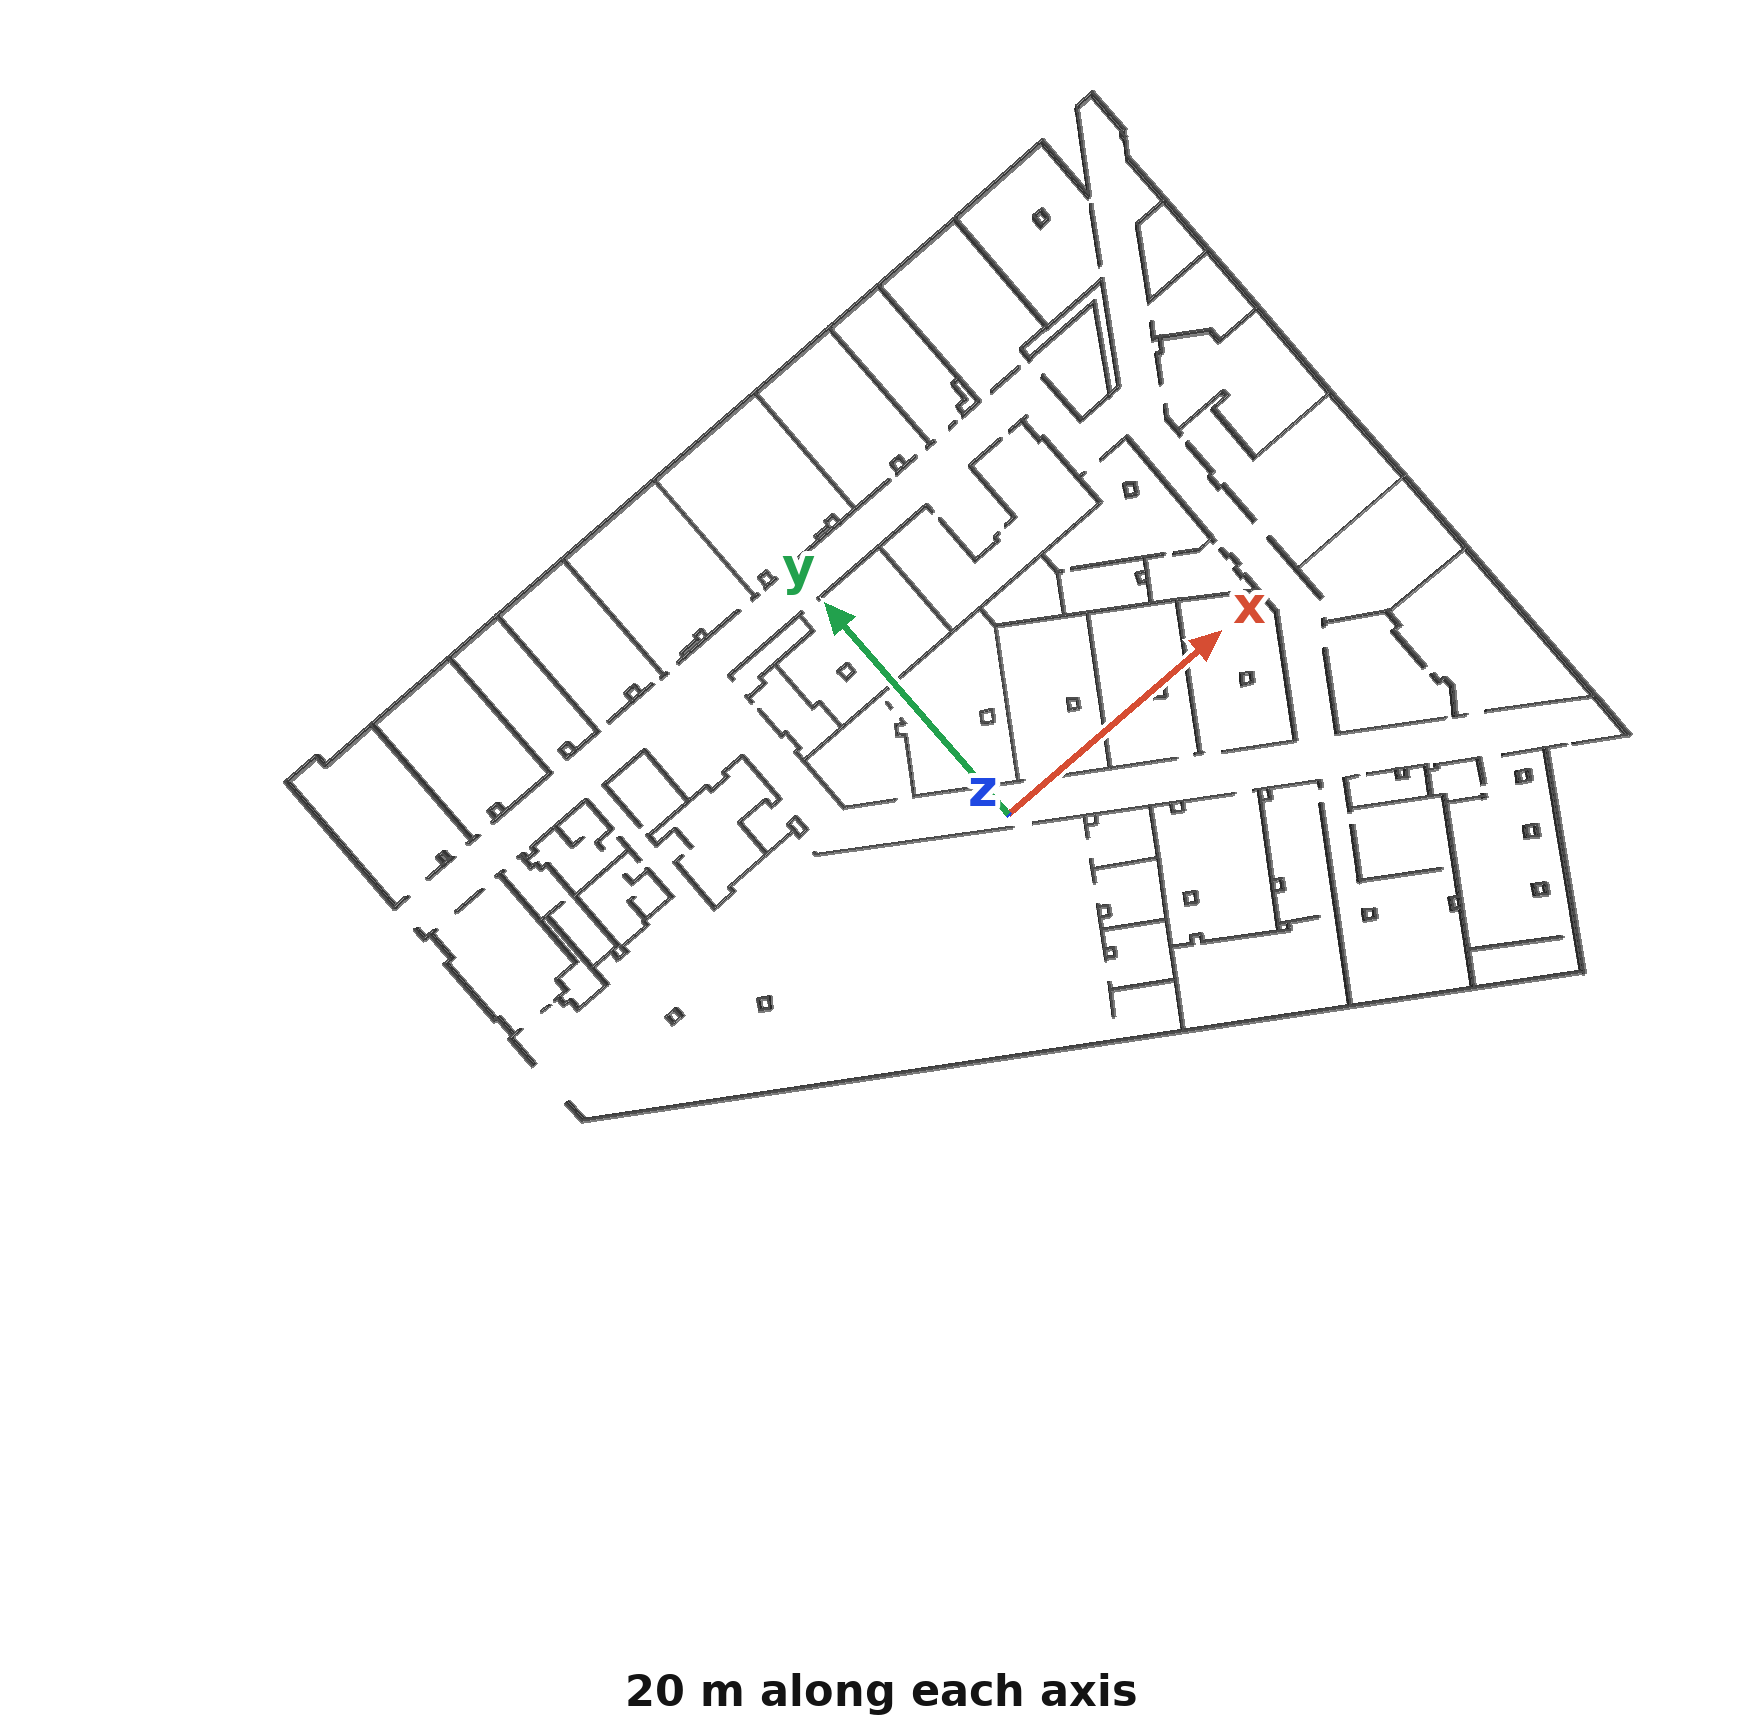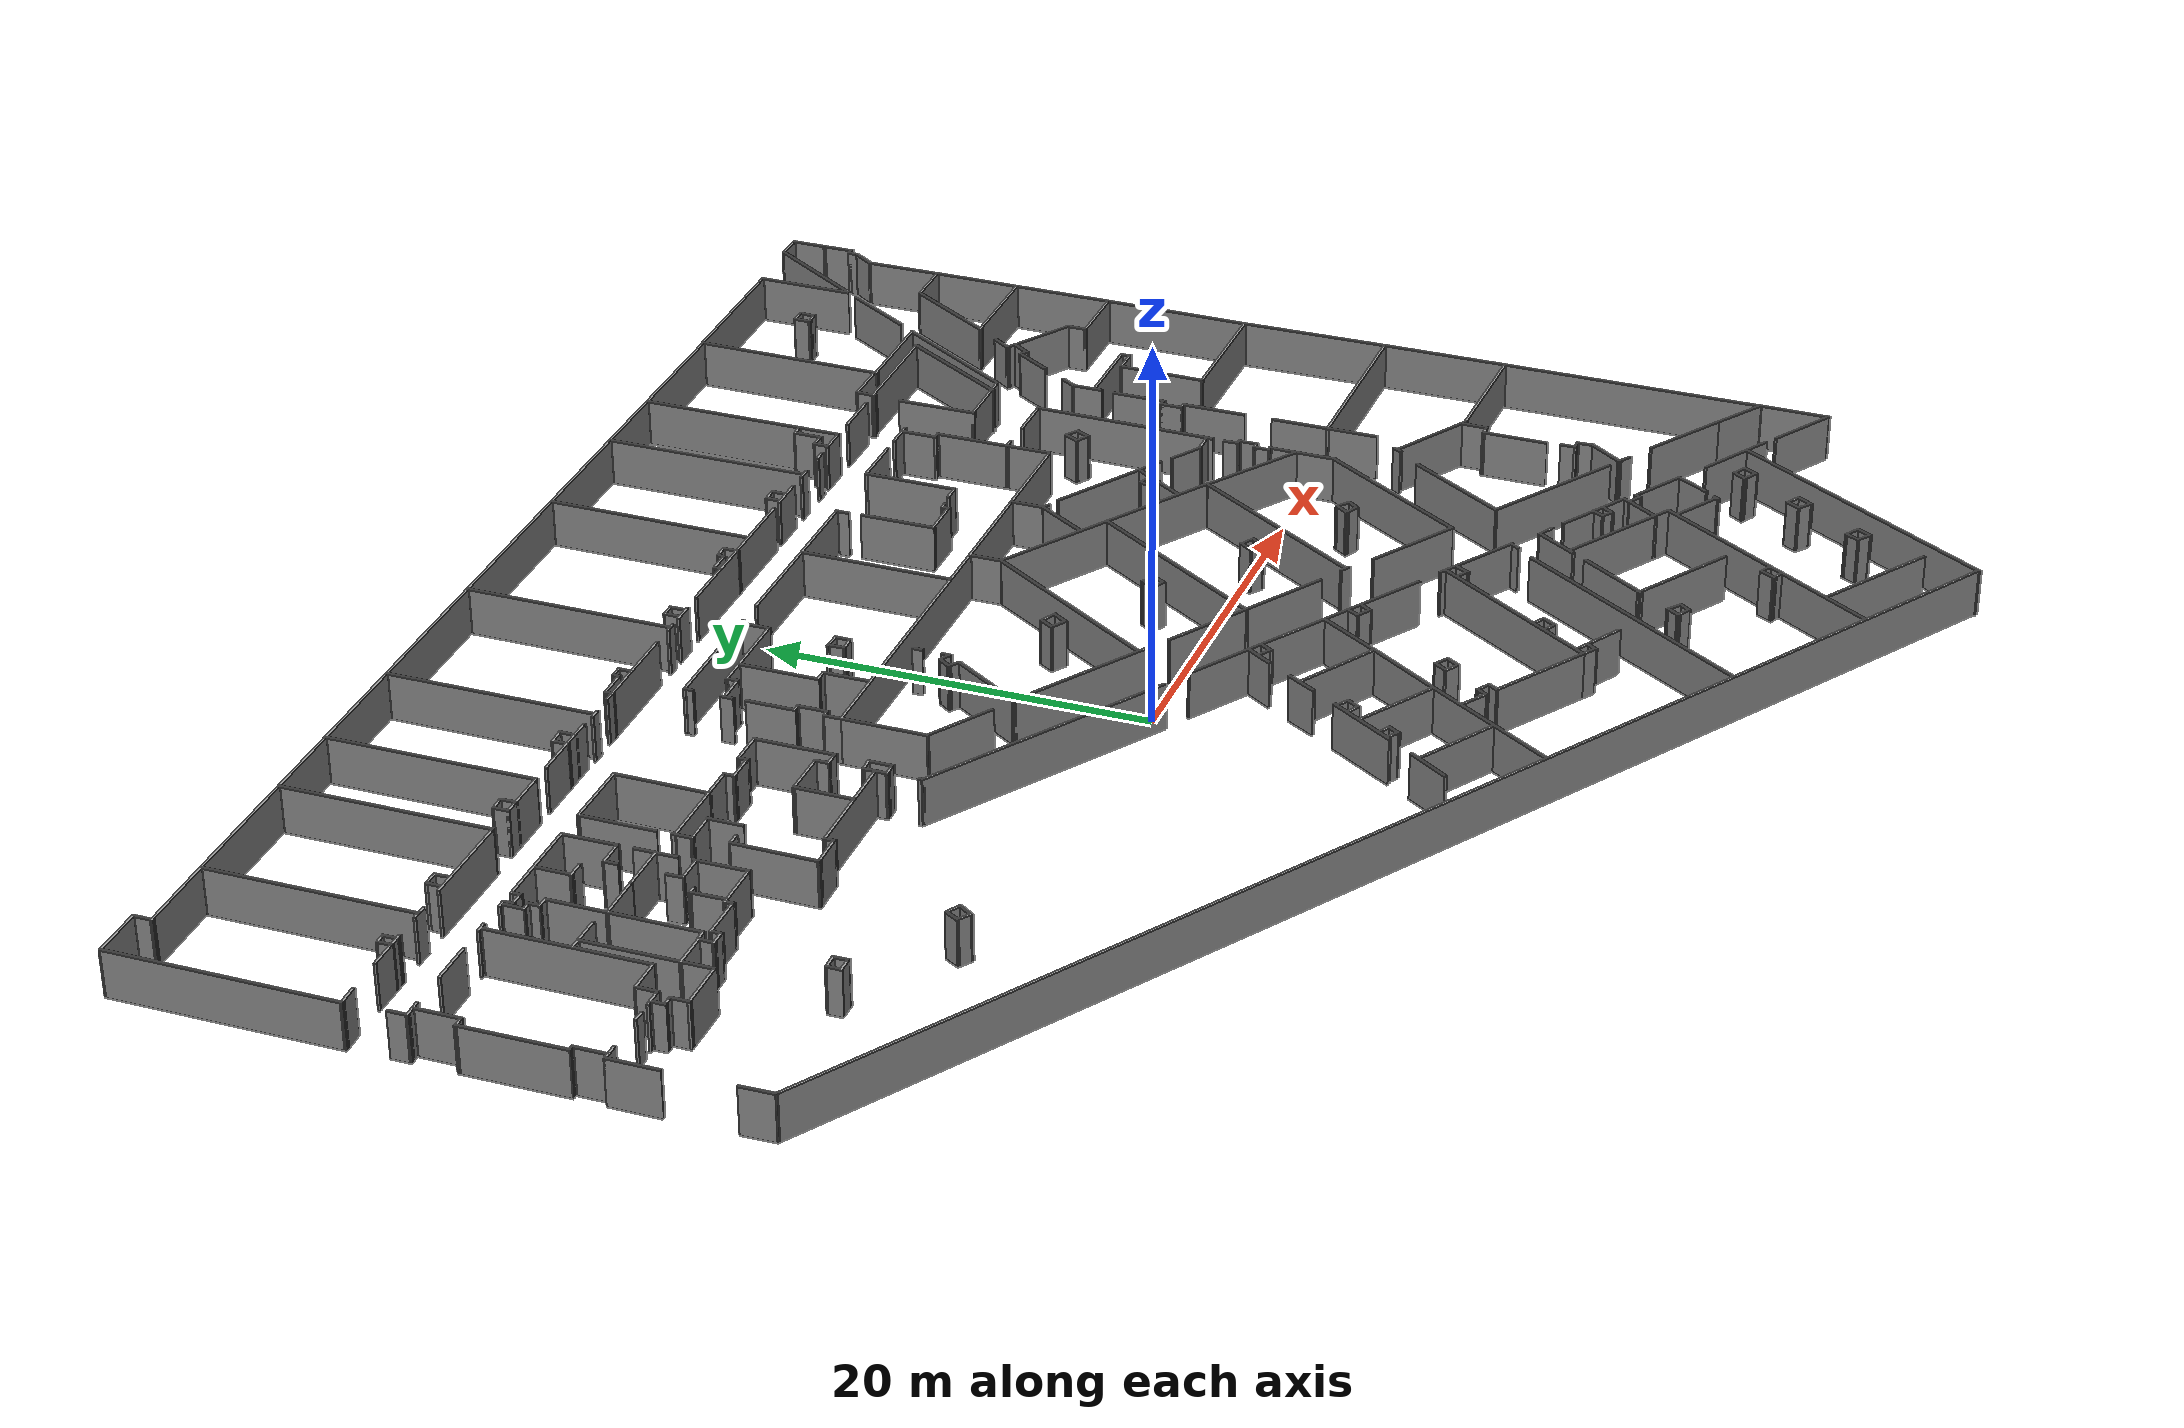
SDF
<?xml version='1.0'?>
<sdf version='1.7'>
  <model name='HopperFloorGround_Full'>
    <pose>0.395792 0.11413 0 0 -0 0</pose>
    <link name='Wall_0'>
      <collision name='Wall_0_Collision'>
        <geometry>
          <box>
            <size>71.6402 0.15 2.5</size>
          </box>
        </geometry>
        <pose>0 0 1.25 0 -0 0</pose>
      </collision>
      <visual name='Wall_0_Visual'>
        <pose>0 0 1.25 0 -0 0</pose>
        <geometry>
          <box>
            <size>71.6402 0.15 2.5</size>
          </box>
        </geometry>
        <material>
          <script>
            <uri>file://media/materials/scripts/gazebo.material</uri>
            <name>Gazebo/Grey</name>
          </script>
          <ambient>1 1 1 1</ambient>
        </material>
        <meta>
          <layer>0</layer>
        </meta>
      </visual>
      <pose>-7.1575 -15.8591 0 0 -0 -0.566616</pose>
    </link>
    <link name='Wall_1'>
      <collision name='Wall_1_Collision'>
        <geometry>
          <box>
            <size>16.3063 0.15 2.5</size>
          </box>
        </geometry>
        <pose>0 0 1.25 0 -0 0</pose>
      </collision>
      <visual name='Wall_1_Visual'>
        <pose>0 0 1.25 0 -0 0</pose>
        <geometry>
          <box>
            <size>16.3063 0.15 2.5</size>
          </box>
        </geometry>
        <material>
          <script>
            <uri>file://media/materials/scripts/gazebo.material</uri>
            <name>Gazebo/Grey</name>
          </script>
          <ambient>1 1 1 1</ambient>
        </material>
        <meta>
          <layer>0</layer>
        </meta>
      </visual>
      <pose>27.2284 -28.2428 0 0 -0 1.02013</pose>
    </link>
    <link name='Wall_10'>
      <collision name='Wall_10_Collision'>
        <geometry>
          <box>
            <size>0.518953 0.15 2.5</size>
          </box>
        </geometry>
        <pose>0 0 1.25 0 -0 0</pose>
      </collision>
      <visual name='Wall_10_Visual'>
        <pose>0 0 1.25 0 -0 0</pose>
        <geometry>
          <box>
            <size>0.518953 0.15 2.5</size>
          </box>
        </geometry>
        <material>
          <script>
            <uri>file://media/materials/scripts/gazebo.material</uri>
            <name>Gazebo/Grey</name>
          </script>
          <ambient>1 1 1 1</ambient>
        </material>
        <meta>
          <layer>0</layer>
        </meta>
      </visual>
      <pose>24.1583 -16.8971 0 0 -0 1.02225</pose>
    </link>
    <link name='Wall_101'>
      <collision name='Wall_101_Collision'>
        <geometry>
          <box>
            <size>1 0.15 2.5</size>
          </box>
        </geometry>
        <pose>0 0 1.25 0 -0 0</pose>
      </collision>
      <visual name='Wall_101_Visual'>
        <pose>0 0 1.25 0 -0 0</pose>
        <geometry>
          <box>
            <size>1 0.15 2.5</size>
          </box>
        </geometry>
        <material>
          <script>
            <uri>file://media/materials/scripts/gazebo.material</uri>
            <name>Gazebo/Grey</name>
          </script>
          <ambient>1 1 1 1</ambient>
        </material>
        <meta>
          <layer>0</layer>
        </meta>
      </visual>
      <pose>-24.7641 18.4859 0 0 -0 3.14159</pose>
    </link>
    <link name='Wall_102'>
      <collision name='Wall_102_Collision'>
        <geometry>
          <box>
            <size>1.96918 0.15 2.5</size>
          </box>
        </geometry>
        <pose>0 0 1.25 0 -0 0</pose>
      </collision>
      <visual name='Wall_102_Visual'>
        <pose>0 0 1.25 0 -0 0</pose>
        <geometry>
          <box>
            <size>1.96918 0.15 2.5</size>
          </box>
        </geometry>
        <material>
          <script>
            <uri>file://media/materials/scripts/gazebo.material</uri>
            <name>Gazebo/Grey</name>
          </script>
          <ambient>1 1 1 1</ambient>
        </material>
        <meta>
          <layer>0</layer>
        </meta>
      </visual>
      <pose>-25.1838 19.3954 0 0 -0 1.56504</pose>
    </link>
    <link name='Wall_106'>
      <collision name='Wall_106_Collision'>
        <geometry>
          <box>
            <size>8.39659 0.15 2.5</size>
          </box>
        </geometry>
        <pose>0 0 1.25 0 -0 0</pose>
      </collision>
      <visual name='Wall_106_Visual'>
        <pose>0 0 1.25 0 -0 0</pose>
        <geometry>
          <box>
            <size>8.39659 0.15 2.5</size>
          </box>
        </geometry>
        <material>
          <script>
            <uri>file://media/materials/scripts/gazebo.material</uri>
            <name>Gazebo/Grey</name>
          </script>
          <ambient>1 1 1 1</ambient>
        </material>
        <meta>
          <layer>0</layer>
        </meta>
      </visual>
      <pose>-30.3925 16.2262 0 0 -0 1.56836</pose>
    </link>
    <link name='Wall_108'>
      <collision name='Wall_108_Collision'>
        <geometry>
          <box>
            <size>1.94011 0.15 2.5</size>
          </box>
        </geometry>
        <pose>0 0 1.25 0 -0 0</pose>
      </collision>
      <visual name='Wall_108_Visual'>
        <pose>0 0 1.25 0 -0 0</pose>
        <geometry>
          <box>
            <size>1.94011 0.15 2.5</size>
          </box>
        </geometry>
        <material>
          <script>
            <uri>file://media/materials/scripts/gazebo.material</uri>
            <name>Gazebo/Grey</name>
          </script>
          <ambient>1 1 1 1</ambient>
        </material>
        <meta>
          <layer>0</layer>
        </meta>
      </visual>
      <pose>-31.2976 12.103 0 0 -0 3.14159</pose>
    </link>
    <link name='Wall_109'>
      <collision name='Wall_109_Collision'>
        <geometry>
          <box>
            <size>1.1961 0.15 2.5</size>
          </box>
        </geometry>
        <pose>0 0 1.25 0 -0 0</pose>
      </collision>
      <visual name='Wall_109_Visual'>
        <pose>0 0 1.25 0 -0 0</pose>
        <geometry>
          <box>
            <size>1.1961 0.15 2.5</size>
          </box>
        </geometry>
        <material>
          <script>
            <uri>file://media/materials/scripts/gazebo.material</uri>
            <name>Gazebo/Grey</name>
          </script>
          <ambient>1 1 1 1</ambient>
        </material>
        <meta>
          <layer>0</layer>
        </meta>
      </visual>
      <pose>-32.2027 11.58 0 0 -0 -1.59003</pose>
    </link>
    <link name='Wall_110'>
      <collision name='Wall_110_Collision'>
        <geometry>
          <box>
            <size>0.914316 0.15 2.5</size>
          </box>
        </geometry>
        <pose>0 0 1.25 0 -0 0</pose>
      </collision>
      <visual name='Wall_110_Visual'>
        <pose>0 0 1.25 0 -0 0</pose>
        <geometry>
          <box>
            <size>0.914316 0.15 2.5</size>
          </box>
        </geometry>
        <material>
          <script>
            <uri>file://media/materials/scripts/gazebo.material</uri>
            <name>Gazebo/Grey</name>
          </script>
          <ambient>1 1 1 1</ambient>
        </material>
        <meta>
          <layer>0</layer>
        </meta>
      </visual>
      <pose>-32.5949 11.0571 0 0 -0 3.14159</pose>
    </link>
    <link name='Wall_112'>
      <collision name='Wall_112_Collision'>
        <geometry>
          <box>
            <size>0.75 0.15 2.5</size>
          </box>
        </geometry>
        <pose>0 0 1.25 0 -0 0</pose>
      </collision>
      <visual name='Wall_112_Visual'>
        <pose>0 0 1.25 0 -0 0</pose>
        <geometry>
          <box>
            <size>0.75 0.15 2.5</size>
          </box>
        </geometry>
        <material>
          <script>
            <uri>file://media/materials/scripts/gazebo.material</uri>
            <name>Gazebo/Grey</name>
          </script>
          <ambient>1 1 1 1</ambient>
        </material>
        <meta>
          <layer>0</layer>
        </meta>
      </visual>
      <pose>-20.122 12.8829 0 0 -0 3.14159</pose>
    </link>
    <link name='Wall_113'>
      <collision name='Wall_113_Collision'>
        <geometry>
          <box>
            <size>4.49402 0.15 2.5</size>
          </box>
        </geometry>
        <pose>0 0 1.25 0 -0 0</pose>
      </collision>
      <visual name='Wall_113_Visual'>
        <pose>0 0 1.25 0 -0 0</pose>
        <geometry>
          <box>
            <size>4.49402 0.15 2.5</size>
          </box>
        </geometry>
        <material>
          <script>
            <uri>file://media/materials/scripts/gazebo.material</uri>
            <name>Gazebo/Grey</name>
          </script>
          <ambient>1 1 1 1</ambient>
        </material>
        <meta>
          <layer>0</layer>
        </meta>
      </visual>
      <pose>-20.4432 10.711 0 0 -0 -1.58056</pose>
    </link>
    <link name='Wall_114'>
      <collision name='Wall_114_Collision'>
        <geometry>
          <box>
            <size>1.95508 0.15 2.5</size>
          </box>
        </geometry>
        <pose>0 0 1.25 0 -0 0</pose>
      </collision>
      <visual name='Wall_114_Visual'>
        <pose>0 0 1.25 0 -0 0</pose>
        <geometry>
          <box>
            <size>1.95508 0.15 2.5</size>
          </box>
        </geometry>
        <material>
          <script>
            <uri>file://media/materials/scripts/gazebo.material</uri>
            <name>Gazebo/Grey</name>
          </script>
          <ambient>1 1 1 1</ambient>
        </material>
        <meta>
          <layer>0</layer>
        </meta>
      </visual>
      <pose>-19.562 8.5544 0 0 -0 0.016948</pose>
    </link>
    <link name='Wall_115'>
      <collision name='Wall_115_Collision'>
        <geometry>
          <box>
            <size>0.609872 0.15 2.5</size>
          </box>
        </geometry>
        <pose>0 0 1.25 0 -0 0</pose>
      </collision>
      <visual name='Wall_115_Visual'>
        <pose>0 0 1.25 0 -0 0</pose>
        <geometry>
          <box>
            <size>0.609872 0.15 2.5</size>
          </box>
        </geometry>
        <material>
          <script>
            <uri>file://media/materials/scripts/gazebo.material</uri>
            <name>Gazebo/Grey</name>
          </script>
          <ambient>1 1 1 1</ambient>
        </material>
        <meta>
          <layer>0</layer>
        </meta>
      </visual>
      <pose>-18.6749 8.79912 0 0 -0 1.63736</pose>
    </link>
    <link name='Wall_116'>
      <collision name='Wall_116_Collision'>
        <geometry>
          <box>
            <size>6.23753 0.15 2.5</size>
          </box>
        </geometry>
        <pose>0 0 1.25 0 -0 0</pose>
      </collision>
      <visual name='Wall_116_Visual'>
        <pose>0 0 1.25 0 -0 0</pose>
        <geometry>
          <box>
            <size>6.23753 0.15 2.5</size>
          </box>
        </geometry>
        <material>
          <script>
            <uri>file://media/materials/scripts/gazebo.material</uri>
            <name>Gazebo/Grey</name>
          </script>
          <ambient>1 1 1 1</ambient>
        </material>
        <meta>
          <layer>0</layer>
        </meta>
      </visual>
      <pose>-15.6464 9.04384 0 0 -0 0.005025</pose>
    </link>
    <link name='Wall_117'>
      <collision name='Wall_117_Collision'>
        <geometry>
          <box>
            <size>0.731214 0.15 2.5</size>
          </box>
        </geometry>
        <pose>0 0 1.25 0 -0 0</pose>
      </collision>
      <visual name='Wall_117_Visual'>
        <pose>0 0 1.25 0 -0 0</pose>
        <geometry>
          <box>
            <size>0.731214 0.15 2.5</size>
          </box>
        </geometry>
        <material>
          <script>
            <uri>file://media/materials/scripts/gazebo.material</uri>
            <name>Gazebo/Grey</name>
          </script>
          <ambient>1 1 1 1</ambient>
        </material>
        <meta>
          <layer>0</layer>
        </meta>
      </visual>
      <pose>-12.6027 8.76853 0 0 -0 -1.5708</pose>
    </link>
    <link name='Wall_118'>
      <collision name='Wall_118_Collision'>
        <geometry>
          <box>
            <size>0.85424 0.15 2.5</size>
          </box>
        </geometry>
        <pose>0 0 1.25 0 -0 0</pose>
      </collision>
      <visual name='Wall_118_Visual'>
        <pose>0 0 1.25 0 -0 0</pose>
        <geometry>
          <box>
            <size>0.85424 0.15 2.5</size>
          </box>
        </geometry>
        <material>
          <script>
            <uri>file://media/materials/scripts/gazebo.material</uri>
            <name>Gazebo/Grey</name>
          </script>
          <ambient>1 1 1 1</ambient>
        </material>
        <meta>
          <layer>0</layer>
        </meta>
      </visual>
      <pose>-12.2509 8.49322 0 0 -0 0.043451</pose>
    </link>
    <link name='Wall_119'>
      <collision name='Wall_119_Collision'>
        <geometry>
          <box>
            <size>1.34302 0.15 2.5</size>
          </box>
        </geometry>
        <pose>0 0 1.25 0 -0 0</pose>
      </collision>
      <visual name='Wall_119_Visual'>
        <pose>0 0 1.25 0 -0 0</pose>
        <geometry>
          <box>
            <size>1.34302 0.15 2.5</size>
          </box>
        </geometry>
        <material>
          <script>
            <uri>file://media/materials/scripts/gazebo.material</uri>
            <name>Gazebo/Grey</name>
          </script>
          <ambient>1 1 1 1</ambient>
        </material>
        <meta>
          <layer>0</layer>
        </meta>
      </visual>
      <pose>-11.8991 9.10502 0 0 -0 1.5708</pose>
    </link>
    <link name='Wall_12'>
      <collision name='Wall_12_Collision'>
        <geometry>
          <box>
            <size>4.26067 0.15 2.5</size>
          </box>
        </geometry>
        <pose>0 0 1.25 0 -0 0</pose>
      </collision>
      <visual name='Wall_12_Visual'>
        <pose>0 0 1.25 0 -0 0</pose>
        <geometry>
          <box>
            <size>4.26067 0.15 2.5</size>
          </box>
        </geometry>
        <material>
          <script>
            <uri>file://media/materials/scripts/gazebo.material</uri>
            <name>Gazebo/Grey</name>
          </script>
          <ambient>1 1 1 1</ambient>
        </material>
        <meta>
          <layer>0</layer>
        </meta>
      </visual>
      <pose>22.5135 -15.6473 0 0 -0 2.58124</pose>
    </link>
    <link name='Wall_120'>
      <collision name='Wall_120_Collision'>
        <geometry>
          <box>
            <size>0.88671 0.15 2.5</size>
          </box>
        </geometry>
        <pose>0 0 1.25 0 -0 0</pose>
      </collision>
      <visual name='Wall_120_Visual'>
        <pose>0 0 1.25 0 -0 0</pose>
        <geometry>
          <box>
            <size>0.88671 0.15 2.5</size>
          </box>
        </geometry>
        <material>
          <script>
            <uri>file://media/materials/scripts/gazebo.material</uri>
            <name>Gazebo/Grey</name>
          </script>
          <ambient>1 1 1 1</ambient>
        </material>
        <meta>
          <layer>0</layer>
        </meta>
      </visual>
      <pose>-12.2662 9.67094 0 0 -0 -3.05845</pose>
    </link>
    <link name='Wall_121'>
      <collision name='Wall_121_Collision'>
        <geometry>
          <box>
            <size>0.704013 0.15 2.5</size>
          </box>
        </geometry>
        <pose>0 0 1.25 0 -0 0</pose>
      </collision>
      <visual name='Wall_121_Visual'>
        <pose>0 0 1.25 0 -0 0</pose>
        <geometry>
          <box>
            <size>0.704013 0.15 2.5</size>
          </box>
        </geometry>
        <material>
          <script>
            <uri>file://media/materials/scripts/gazebo.material</uri>
            <name>Gazebo/Grey</name>
          </script>
          <ambient>1 1 1 1</ambient>
        </material>
        <meta>
          <layer>0</layer>
        </meta>
      </visual>
      <pose>-12.6027 9.36504 0 0 -0 -1.46014</pose>
    </link>
    <link name='Wall_123'>
      <collision name='Wall_123_Collision'>
        <geometry>
          <box>
            <size>2.25 0.15 2.5</size>
          </box>
        </geometry>
        <pose>0 0 1.25 0 -0 0</pose>
      </collision>
      <visual name='Wall_123_Visual'>
        <pose>0 0 1.25 0 -0 0</pose>
        <geometry>
          <box>
            <size>2.25 0.15 2.5</size>
          </box>
        </geometry>
        <material>
          <script>
            <uri>file://media/materials/scripts/gazebo.material</uri>
            <name>Gazebo/Grey</name>
          </script>
          <ambient>1 1 1 1</ambient>
        </material>
        <meta>
          <layer>0</layer>
        </meta>
      </visual>
      <pose>-22.29 15.6966 0 0 -0 -1.5708</pose>
    </link>
    <link name='Wall_125'>
      <collision name='Wall_125_Collision'>
        <geometry>
          <box>
            <size>2.75 0.15 2.5</size>
          </box>
        </geometry>
        <pose>0 0 1.25 0 -0 0</pose>
      </collision>
      <visual name='Wall_125_Visual'>
        <pose>0 0 1.25 0 -0 0</pose>
        <geometry>
          <box>
            <size>2.75 0.15 2.5</size>
          </box>
        </geometry>
        <material>
          <script>
            <uri>file://media/materials/scripts/gazebo.material</uri>
            <name>Gazebo/Grey</name>
          </script>
          <ambient>1 1 1 1</ambient>
        </material>
        <meta>
          <layer>0</layer>
        </meta>
      </visual>
      <pose>-23.59 15.7001 0 0 -0 3.14159</pose>
    </link>
    <link name='Wall_126'>
      <collision name='Wall_126_Collision'>
        <geometry>
          <box>
            <size>2.64453 0.15 2.5</size>
          </box>
        </geometry>
        <pose>0 0 1.25 0 -0 0</pose>
      </collision>
      <visual name='Wall_126_Visual'>
        <pose>0 0 1.25 0 -0 0</pose>
        <geometry>
          <box>
            <size>2.64453 0.15 2.5</size>
          </box>
        </geometry>
        <material>
          <script>
            <uri>file://media/materials/scripts/gazebo.material</uri>
            <name>Gazebo/Grey</name>
          </script>
          <ambient>1 1 1 1</ambient>
        </material>
        <meta>
          <layer>0</layer>
        </meta>
      </visual>
      <pose>-26.1372 15.6944 0 0 -0 -3.13698</pose>
    </link>
    <link name='Wall_127'>
      <collision name='Wall_127_Collision'>
        <geometry>
          <box>
            <size>3.17459 0.15 2.5</size>
          </box>
        </geometry>
        <pose>0 0 1.25 0 -0 0</pose>
      </collision>
      <visual name='Wall_127_Visual'>
        <pose>0 0 1.25 0 -0 0</pose>
        <geometry>
          <box>
            <size>3.17459 0.15 2.5</size>
          </box>
        </geometry>
        <material>
          <script>
            <uri>file://media/materials/scripts/gazebo.material</uri>
            <name>Gazebo/Grey</name>
          </script>
          <ambient>1 1 1 1</ambient>
        </material>
        <meta>
          <layer>0</layer>
        </meta>
      </visual>
      <pose>-27.3787 17.2009 0 0 -0 1.56699</pose>
    </link>
    <link name='Wall_129'>
      <collision name='Wall_129_Collision'>
        <geometry>
          <box>
            <size>0.692389 0.15 2.5</size>
          </box>
        </geometry>
        <pose>0 0 1.25 0 -0 0</pose>
      </collision>
      <visual name='Wall_129_Visual'>
        <pose>0 0 1.25 0 -0 0</pose>
        <geometry>
          <box>
            <size>0.692389 0.15 2.5</size>
          </box>
        </geometry>
        <material>
          <script>
            <uri>file://media/materials/scripts/gazebo.material</uri>
            <name>Gazebo/Grey</name>
          </script>
          <ambient>1 1 1 1</ambient>
        </material>
        <meta>
          <layer>0</layer>
        </meta>
      </visual>
      <pose>-27.6442 18.7138 0 0 -0 3.13898</pose>
    </link>
    <link name='Wall_130'>
      <collision name='Wall_130_Collision'>
        <geometry>
          <box>
            <size>0.679125 0.15 2.5</size>
          </box>
        </geometry>
        <pose>0 0 1.25 0 -0 0</pose>
      </collision>
      <visual name='Wall_130_Visual'>
        <pose>0 0 1.25 0 -0 0</pose>
        <geometry>
          <box>
            <size>0.679125 0.15 2.5</size>
          </box>
        </geometry>
        <material>
          <script>
            <uri>file://media/materials/scripts/gazebo.material</uri>
            <name>Gazebo/Grey</name>
          </script>
          <ambient>1 1 1 1</ambient>
        </material>
        <meta>
          <layer>0</layer>
        </meta>
      </visual>
      <pose>-27.9211 18.979 0 0 -0 1.59253</pose>
    </link>
    <link name='Wall_131'>
      <collision name='Wall_131_Collision'>
        <geometry>
          <box>
            <size>0.598647 0.15 2.5</size>
          </box>
        </geometry>
        <pose>0 0 1.25 0 -0 0</pose>
      </collision>
      <visual name='Wall_131_Visual'>
        <pose>0 0 1.25 0 -0 0</pose>
        <geometry>
          <box>
            <size>0.598647 0.15 2.5</size>
          </box>
        </geometry>
        <material>
          <script>
            <uri>file://media/materials/scripts/gazebo.material</uri>
            <name>Gazebo/Grey</name>
          </script>
          <ambient>1 1 1 1</ambient>
        </material>
        <meta>
          <layer>0</layer>
        </meta>
      </visual>
      <pose>-28.1511 19.2493 0 0 -0 3.11596</pose>
    </link>
    <link name='Wall_132'>
      <collision name='Wall_132_Collision'>
        <geometry>
          <box>
            <size>1.17356 0.15 2.5</size>
          </box>
        </geometry>
        <pose>0 0 1.25 0 -0 0</pose>
      </collision>
      <visual name='Wall_132_Visual'>
        <pose>0 0 1.25 0 -0 0</pose>
        <geometry>
          <box>
            <size>1.17356 0.15 2.5</size>
          </box>
        </geometry>
        <material>
          <script>
            <uri>file://media/materials/scripts/gazebo.material</uri>
            <name>Gazebo/Grey</name>
          </script>
          <ambient>1 1 1 1</ambient>
        </material>
        <meta>
          <layer>0</layer>
        </meta>
      </visual>
      <pose>-28.3696 19.7668 0 0 -0 1.55956</pose>
    </link>
    <link name='Wall_134'>
      <collision name='Wall_134_Collision'>
        <geometry>
          <box>
            <size>2.16263 0.15 2.5</size>
          </box>
        </geometry>
        <pose>0 0 1.25 0 -0 0</pose>
      </collision>
      <visual name='Wall_134_Visual'>
        <pose>0 0 1.25 0 -0 0</pose>
        <geometry>
          <box>
            <size>2.16263 0.15 2.5</size>
          </box>
        </geometry>
        <material>
          <script>
            <uri>file://media/materials/scripts/gazebo.material</uri>
            <name>Gazebo/Grey</name>
          </script>
          <ambient>1 1 1 1</ambient>
        </material>
        <meta>
          <layer>0</layer>
        </meta>
      </visual>
      <pose>-29.3586 15.9545 0 0 -0 3.13016</pose>
    </link>
    <link name='Wall_137'>
      <collision name='Wall_137_Collision'>
        <geometry>
          <box>
            <size>5 0.15 2.5</size>
          </box>
        </geometry>
        <pose>0 0 1.25 0 -0 0</pose>
      </collision>
      <visual name='Wall_137_Visual'>
        <pose>0 0 1.25 0 -0 0</pose>
        <geometry>
          <box>
            <size>5 0.15 2.5</size>
          </box>
        </geometry>
        <material>
          <script>
            <uri>file://media/materials/scripts/gazebo.material</uri>
            <name>Gazebo/Grey</name>
          </script>
          <ambient>1 1 1 1</ambient>
        </material>
        <meta>
          <layer>0</layer>
        </meta>
      </visual>
      <pose>-29.7968 13.4907 0 0 -0 1.5708</pose>
    </link>
    <link name='Wall_139'>
      <collision name='Wall_139_Collision'>
        <geometry>
          <box>
            <size>4.73481 0.15 2.5</size>
          </box>
        </geometry>
        <pose>0 0 1.25 0 -0 0</pose>
      </collision>
      <visual name='Wall_139_Visual'>
        <pose>0 0 1.25 0 -0 0</pose>
        <geometry>
          <box>
            <size>4.73481 0.15 2.5</size>
          </box>
        </geometry>
        <material>
          <script>
            <uri>file://media/materials/scripts/gazebo.material</uri>
            <name>Gazebo/Grey</name>
          </script>
          <ambient>1 1 1 1</ambient>
        </material>
        <meta>
          <layer>0</layer>
        </meta>
      </visual>
      <pose>-27.3873 13.3962 0 0 -0 -1.57203</pose>
    </link>
    <link name='Wall_14'>
      <collision name='Wall_14_Collision'>
        <geometry>
          <box>
            <size>1.0029 0.15 2.5</size>
          </box>
        </geometry>
        <pose>0 0 1.25 0 -0 0</pose>
      </collision>
      <visual name='Wall_14_Visual'>
        <pose>0 0 1.25 0 -0 0</pose>
        <geometry>
          <box>
            <size>1.0029 0.15 2.5</size>
          </box>
        </geometry>
        <material>
          <script>
            <uri>file://media/materials/scripts/gazebo.material</uri>
            <name>Gazebo/Grey</name>
          </script>
          <ambient>1 1 1 1</ambient>
        </material>
        <meta>
          <layer>0</layer>
        </meta>
      </visual>
      <pose>19.6794 -13.9165 0 0 -0 2.65043</pose>
    </link>
    <link name='Wall_140'>
      <collision name='Wall_140_Collision'>
        <geometry>
          <box>
            <size>0.679661 0.15 2.5</size>
          </box>
        </geometry>
        <pose>0 0 1.25 0 -0 0</pose>
      </collision>
      <visual name='Wall_140_Visual'>
        <pose>0 0 1.25 0 -0 0</pose>
        <geometry>
          <box>
            <size>0.679661 0.15 2.5</size>
          </box>
        </geometry>
        <material>
          <script>
            <uri>file://media/materials/scripts/gazebo.material</uri>
            <name>Gazebo/Grey</name>
          </script>
          <ambient>1 1 1 1</ambient>
        </material>
        <meta>
          <layer>0</layer>
        </meta>
      </visual>
      <pose>-27.6546 11.0906 0 0 -0 -3.09163</pose>
    </link>
    <link name='Wall_142'>
      <collision name='Wall_142_Collision'>
        <geometry>
          <box>
            <size>4 0.15 2.5</size>
          </box>
        </geometry>
        <pose>0 0 1.25 0 -0 0</pose>
      </collision>
      <visual name='Wall_142_Visual'>
        <pose>0 0 1.25 0 -0 0</pose>
        <geometry>
          <box>
            <size>4 0.15 2.5</size>
          </box>
        </geometry>
        <material>
          <script>
            <uri>file://media/materials/scripts/gazebo.material</uri>
            <name>Gazebo/Grey</name>
          </script>
          <ambient>1 1 1 1</ambient>
        </material>
        <meta>
          <layer>0</layer>
        </meta>
      </visual>
      <pose>-20.6382 18.3734 0 0 -0 1.5708</pose>
    </link>
    <link name='Wall_143'>
      <collision name='Wall_143_Collision'>
        <geometry>
          <box>
            <size>3.9067 0.15 2.5</size>
          </box>
        </geometry>
        <pose>0 0 1.25 0 -0 0</pose>
      </collision>
      <visual name='Wall_143_Visual'>
        <pose>0 0 1.25 0 -0 0</pose>
        <geometry>
          <box>
            <size>3.9067 0.15 2.5</size>
          </box>
        </geometry>
        <material>
          <script>
            <uri>file://media/materials/scripts/gazebo.material</uri>
            <name>Gazebo/Grey</name>
          </script>
          <ambient>1 1 1 1</ambient>
        </material>
        <meta>
          <layer>0</layer>
        </meta>
      </visual>
      <pose>-18.7599 20.2897 0 0 -0 -0.004631</pose>
    </link>
    <link name='Wall_144'>
      <collision name='Wall_144_Collision'>
        <geometry>
          <box>
            <size>4.92593 0.15 2.5</size>
          </box>
        </geometry>
        <pose>0 0 1.25 0 -0 0</pose>
      </collision>
      <visual name='Wall_144_Visual'>
        <pose>0 0 1.25 0 -0 0</pose>
        <geometry>
          <box>
            <size>4.92593 0.15 2.5</size>
          </box>
        </geometry>
        <material>
          <script>
            <uri>file://media/materials/scripts/gazebo.material</uri>
            <name>Gazebo/Grey</name>
          </script>
          <ambient>1 1 1 1</ambient>
        </material>
        <meta>
          <layer>0</layer>
        </meta>
      </visual>
      <pose>-16.9045 17.8932 0 0 -0 -1.58035</pose>
    </link>
    <link name='Wall_145'>
      <collision name='Wall_145_Collision'>
        <geometry>
          <box>
            <size>1.89901 0.15 2.5</size>
          </box>
        </geometry>
        <pose>0 0 1.25 0 -0 0</pose>
      </collision>
      <visual name='Wall_145_Visual'>
        <pose>0 0 1.25 0 -0 0</pose>
        <geometry>
          <box>
            <size>1.89901 0.15 2.5</size>
          </box>
        </geometry>
        <material>
          <script>
            <uri>file://media/materials/scripts/gazebo.material</uri>
            <name>Gazebo/Grey</name>
          </script>
          <ambient>1 1 1 1</ambient>
        </material>
        <meta>
          <layer>0</layer>
        </meta>
      </visual>
      <pose>-16.0528 15.5054 0 0 -0 0</pose>
    </link>
    <link name='Wall_147'>
      <collision name='Wall_147_Collision'>
        <geometry>
          <box>
            <size>0.25 0.15 2.5</size>
          </box>
        </geometry>
        <pose>0 0 1.25 0 -0 0</pose>
      </collision>
      <visual name='Wall_147_Visual'>
        <pose>0 0 1.25 0 -0 0</pose>
        <geometry>
          <box>
            <size>0.25 0.15 2.5</size>
          </box>
        </geometry>
        <material>
          <script>
            <uri>file://media/materials/scripts/gazebo.material</uri>
            <name>Gazebo/Grey</name>
          </script>
          <ambient>1 1 1 1</ambient>
        </material>
        <meta>
          <layer>0</layer>
        </meta>
      </visual>
      <pose>-20.623 15.5619 0 0 -0 -1.5708</pose>
    </link>
    <link name='Wall_148'>
      <collision name='Wall_148_Collision'>
        <geometry>
          <box>
            <size>3.84573 0.15 2.5</size>
          </box>
        </geometry>
        <pose>0 0 1.25 0 -0 0</pose>
      </collision>
      <visual name='Wall_148_Visual'>
        <pose>0 0 1.25 0 -0 0</pose>
        <geometry>
          <box>
            <size>3.84573 0.15 2.5</size>
          </box>
        </geometry>
        <material>
          <script>
            <uri>file://media/materials/scripts/gazebo.material</uri>
            <name>Gazebo/Grey</name>
          </script>
          <ambient>1 1 1 1</ambient>
        </material>
        <meta>
          <layer>0</layer>
        </meta>
      </visual>
      <pose>-18.7751 15.5087 0 0 -0 -0.001748</pose>
    </link>
    <link name='Wall_15'>
      <collision name='Wall_15_Collision'>
        <geometry>
          <box>
            <size>2.53238 0.15 2.5</size>
          </box>
        </geometry>
        <pose>0 0 1.25 0 -0 0</pose>
      </collision>
      <visual name='Wall_15_Visual'>
        <pose>0 0 1.25 0 -0 0</pose>
        <geometry>
          <box>
            <size>2.53238 0.15 2.5</size>
          </box>
        </geometry>
        <material>
          <script>
            <uri>file://media/materials/scripts/gazebo.material</uri>
            <name>Gazebo/Grey</name>
          </script>
          <ambient>1 1 1 1</ambient>
        </material>
        <meta>
          <layer>0</layer>
        </meta>
      </visual>
      <pose>18.665 -14.7211 0 0 -0 -2.1364</pose>
    </link>
    <link name='Wall_150'>
      <collision name='Wall_150_Collision'>
        <geometry>
          <box>
            <size>1 0.15 2.5</size>
          </box>
        </geometry>
        <pose>0 0 1.25 0 -0 0</pose>
      </collision>
      <visual name='Wall_150_Visual'>
        <pose>0 0 1.25 0 -0 0</pose>
        <geometry>
          <box>
            <size>1 0.15 2.5</size>
          </box>
        </geometry>
        <material>
          <script>
            <uri>file://media/materials/scripts/gazebo.material</uri>
            <name>Gazebo/Grey</name>
          </script>
          <ambient>1 1 1 1</ambient>
        </material>
        <meta>
          <layer>0</layer>
        </meta>
      </visual>
      <pose>-20.623 15.0869 0 0 -0 -1.5708</pose>
    </link>
    <link name='Wall_152'>
      <collision name='Wall_152_Collision'>
        <geometry>
          <box>
            <size>0.651889 0.15 2.5</size>
          </box>
        </geometry>
        <pose>0 0 1.25 0 -0 0</pose>
      </collision>
      <visual name='Wall_152_Visual'>
        <pose>0 0 1.25 0 -0 0</pose>
        <geometry>
          <box>
            <size>0.651889 0.15 2.5</size>
          </box>
        </geometry>
        <material>
          <script>
            <uri>file://media/materials/scripts/gazebo.material</uri>
            <name>Gazebo/Grey</name>
          </script>
          <ambient>1 1 1 1</ambient>
        </material>
        <meta>
          <layer>0</layer>
        </meta>
      </visual>
      <pose>-15.1783 15.2545 0 0 -0 -1.5708</pose>
    </link>
    <link name='Wall_153'>
      <collision name='Wall_153_Collision'>
        <geometry>
          <box>
            <size>1.64054 0.15 2.5</size>
          </box>
        </geometry>
        <pose>0 0 1.25 0 -0 0</pose>
      </collision>
      <visual name='Wall_153_Visual'>
        <pose>0 0 1.25 0 -0 0</pose>
        <geometry>
          <box>
            <size>1.64054 0.15 2.5</size>
          </box>
        </geometry>
        <material>
          <script>
            <uri>file://media/materials/scripts/gazebo.material</uri>
            <name>Gazebo/Grey</name>
          </script>
          <ambient>1 1 1 1</ambient>
        </material>
        <meta>
          <layer>0</layer>
        </meta>
      </visual>
      <pose>-14.433 15.0112 0 0 -0 0.010204</pose>
    </link>
    <link name='Wall_154'>
      <collision name='Wall_154_Collision'>
        <geometry>
          <box>
            <size>0.576116 0.15 2.5</size>
          </box>
        </geometry>
        <pose>0 0 1.25 0 -0 0</pose>
      </collision>
      <visual name='Wall_154_Visual'>
        <pose>0 0 1.25 0 -0 0</pose>
        <geometry>
          <box>
            <size>0.576116 0.15 2.5</size>
          </box>
        </geometry>
        <material>
          <script>
            <uri>file://media/materials/scripts/gazebo.material</uri>
            <name>Gazebo/Grey</name>
          </script>
          <ambient>1 1 1 1</ambient>
        </material>
        <meta>
          <layer>0</layer>
        </meta>
      </visual>
      <pose>-13.6954 15.2317 0 0 -0 1.6065</pose>
    </link>
    <link name='Wall_155'>
      <collision name='Wall_155_Collision'>
        <geometry>
          <box>
            <size>1.95991 0.15 2.5</size>
          </box>
        </geometry>
        <pose>0 0 1.25 0 -0 0</pose>
      </collision>
      <visual name='Wall_155_Visual'>
        <pose>0 0 1.25 0 -0 0</pose>
        <geometry>
          <box>
            <size>1.95991 0.15 2.5</size>
          </box>
        </geometry>
        <material>
          <script>
            <uri>file://media/materials/scripts/gazebo.material</uri>
            <name>Gazebo/Grey</name>
          </script>
          <ambient>1 1 1 1</ambient>
        </material>
        <meta>
          <layer>0</layer>
        </meta>
      </visual>
      <pose>-12.7981 15.4446 0 0 -0 0</pose>
    </link>
    <link name='Wall_156'>
      <collision name='Wall_156_Collision'>
        <geometry>
          <box>
            <size>4.22595 0.15 2.5</size>
          </box>
        </geometry>
        <pose>0 0 1.25 0 -0 0</pose>
      </collision>
      <visual name='Wall_156_Visual'>
        <pose>0 0 1.25 0 -0 0</pose>
        <geometry>
          <box>
            <size>4.22595 0.15 2.5</size>
          </box>
        </geometry>
        <material>
          <script>
            <uri>file://media/materials/scripts/gazebo.material</uri>
            <name>Gazebo/Grey</name>
          </script>
          <ambient>1 1 1 1</ambient>
        </material>
        <meta>
          <layer>0</layer>
        </meta>
      </visual>
      <pose>-11.9008 13.4066 0 0 -0 -1.57453</pose>
    </link>
    <link name='Wall_157'>
      <collision name='Wall_157_Collision'>
        <geometry>
          <box>
            <size>0.910437 0.15 2.5</size>
          </box>
        </geometry>
        <pose>0 0 1.25 0 -0 0</pose>
      </collision>
      <visual name='Wall_157_Visual'>
        <pose>0 0 1.25 0 -0 0</pose>
        <geometry>
          <box>
            <size>0.910437 0.15 2.5</size>
          </box>
        </geometry>
        <material>
          <script>
            <uri>file://media/materials/scripts/gazebo.material</uri>
            <name>Gazebo/Grey</name>
          </script>
          <ambient>1 1 1 1</ambient>
        </material>
        <meta>
          <layer>0</layer>
        </meta>
      </visual>
      <pose>-12.2886 11.3687 0 0 -0 3.14159</pose>
    </link>
    <link name='Wall_158'>
      <collision name='Wall_158_Collision'>
        <geometry>
          <box>
            <size>0.804683 0.15 2.5</size>
          </box>
        </geometry>
        <pose>0 0 1.25 0 -0 0</pose>
      </collision>
      <visual name='Wall_158_Visual'>
        <pose>0 0 1.25 0 -0 0</pose>
        <geometry>
          <box>
            <size>0.804683 0.15 2.5</size>
          </box>
        </geometry>
        <material>
          <script>
            <uri>file://media/materials/scripts/gazebo.material</uri>
            <name>Gazebo/Grey</name>
          </script>
          <ambient>1 1 1 1</ambient>
        </material>
        <meta>
          <layer>0</layer>
        </meta>
      </visual>
      <pose>-12.6764 11.6956 0 0 -0 1.59405</pose>
    </link>
    <link name='Wall_159'>
      <collision name='Wall_159_Collision'>
        <geometry>
          <box>
            <size>2.61386 0.15 2.5</size>
          </box>
        </geometry>
        <pose>0 0 1.25 0 -0 0</pose>
      </collision>
      <visual name='Wall_159_Visual'>
        <pose>0 0 1.25 0 -0 0</pose>
        <geometry>
          <box>
            <size>2.61386 0.15 2.5</size>
          </box>
        </geometry>
        <material>
          <script>
            <uri>file://media/materials/scripts/gazebo.material</uri>
            <name>Gazebo/Grey</name>
          </script>
          <ambient>1 1 1 1</ambient>
        </material>
        <meta>
          <layer>0</layer>
        </meta>
      </visual>
      <pose>-13.916 12.0302 0 0 -0 3.13542</pose>
    </link>
    <link name='Wall_161'>
      <collision name='Wall_161_Collision'>
        <geometry>
          <box>
            <size>3.11574 0.15 2.5</size>
          </box>
        </geometry>
        <pose>0 0 1.25 0 -0 0</pose>
      </collision>
      <visual name='Wall_161_Visual'>
        <pose>0 0 1.25 0 -0 0</pose>
        <geometry>
          <box>
            <size>3.11574 0.15 2.5</size>
          </box>
        </geometry>
        <material>
          <script>
            <uri>file://media/materials/scripts/gazebo.material</uri>
            <name>Gazebo/Grey</name>
          </script>
          <ambient>1 1 1 1</ambient>
        </material>
        <meta>
          <layer>0</layer>
        </meta>
      </visual>
      <pose>-15.1555 10.555 0 0 -0 -1.57593</pose>
    </link>
    <link name='Wall_163'>
      <collision name='Wall_163_Collision'>
        <geometry>
          <box>
            <size>0.293821 0.15 2.5</size>
          </box>
        </geometry>
        <pose>0 0 1.25 0 -0 0</pose>
      </collision>
      <visual name='Wall_163_Visual'>
        <pose>0 0 1.25 0 -0 0</pose>
        <geometry>
          <box>
            <size>0.293821 0.15 2.5</size>
          </box>
        </geometry>
        <material>
          <script>
            <uri>file://media/materials/scripts/gazebo.material</uri>
            <name>Gazebo/Grey</name>
          </script>
          <ambient>1 1 1 1</ambient>
        </material>
        <meta>
          <layer>0</layer>
        </meta>
      </visual>
      <pose>-12.5366 6.82613 0 0 -0 -1.42643</pose>
    </link>
    <link name='Wall_164'>
      <collision name='Wall_164_Collision'>
        <geometry>
          <box>
            <size>14.1631 0.15 2.5</size>
          </box>
        </geometry>
        <pose>0 0 1.25 0 -0 0</pose>
      </collision>
      <visual name='Wall_164_Visual'>
        <pose>0 0 1.25 0 -0 0</pose>
        <geometry>
          <box>
            <size>14.1631 0.15 2.5</size>
          </box>
        </geometry>
        <material>
          <script>
            <uri>file://media/materials/scripts/gazebo.material</uri>
            <name>Gazebo/Grey</name>
          </script>
          <ambient>1 1 1 1</ambient>
        </material>
        <meta>
          <layer>0</layer>
        </meta>
      </visual>
      <pose>-6.67032 2.93967 0 0 -0 -0.575834</pose>
    </link>
    <link name='Wall_166'>
      <collision name='Wall_166_Collision'>
        <geometry>
          <box>
            <size>14.443 0.15 2.5</size>
          </box>
        </geometry>
        <pose>0 0 1.25 0 -0 0</pose>
      </collision>
      <visual name='Wall_166_Visual'>
        <pose>0 0 1.25 0 -0 0</pose>
        <geometry>
          <box>
            <size>14.443 0.15 2.5</size>
          </box>
        </geometry>
        <material>
          <script>
            <uri>file://media/materials/scripts/gazebo.material</uri>
            <name>Gazebo/Grey</name>
          </script>
          <ambient>1 1 1 1</ambient>
        </material>
        <meta>
          <layer>0</layer>
        </meta>
      </visual>
      <pose>6.60464 -5.5119 0 0 -0 -0.570014</pose>
    </link>
    <link name='Wall_168'>
      <collision name='Wall_168_Collision'>
        <geometry>
          <box>
            <size>1.67737 0.15 2.5</size>
          </box>
        </geometry>
        <pose>0 0 1.25 0 -0 0</pose>
      </collision>
      <visual name='Wall_168_Visual'>
        <pose>0 0 1.25 0 -0 0</pose>
        <geometry>
          <box>
            <size>1.67737 0.15 2.5</size>
          </box>
        </geometry>
        <material>
          <script>
            <uri>file://media/materials/scripts/gazebo.material</uri>
            <name>Gazebo/Grey</name>
          </script>
          <ambient>1 1 1 1</ambient>
        </material>
        <meta>
          <layer>0</layer>
        </meta>
      </visual>
      <pose>3.20221 -4.27331 0 0 -0 -2.14213</pose>
    </link>
    <link name='Wall_17'>
      <collision name='Wall_17_Collision'>
        <geometry>
          <box>
            <size>4.18126 0.15 2.5</size>
          </box>
        </geometry>
        <pose>0 0 1.25 0 -0 0</pose>
      </collision>
      <visual name='Wall_17_Visual'>
        <pose>0 0 1.25 0 -0 0</pose>
        <geometry>
          <box>
            <size>4.18126 0.15 2.5</size>
          </box>
        </geometry>
        <material>
          <script>
            <uri>file://media/materials/scripts/gazebo.material</uri>
            <name>Gazebo/Grey</name>
          </script>
          <ambient>1 1 1 1</ambient>
        </material>
        <meta>
          <layer>0</layer>
        </meta>
      </visual>
      <pose>16.4 -18.2366 0 0 -0 -2.14917</pose>
    </link>
    <link name='Wall_170'>
      <collision name='Wall_170_Collision'>
        <geometry>
          <box>
            <size>0.850577 0.15 2.5</size>
          </box>
        </geometry>
        <pose>0 0 1.25 0 -0 0</pose>
      </collision>
      <visual name='Wall_170_Visual'>
        <pose>0 0 1.25 0 -0 0</pose>
        <geometry>
          <box>
            <size>0.850577 0.15 2.5</size>
          </box>
        </geometry>
        <material>
          <script>
            <uri>file://media/materials/scripts/gazebo.material</uri>
            <name>Gazebo/Grey</name>
          </script>
          <ambient>1 1 1 1</ambient>
        </material>
        <meta>
          <layer>0</layer>
        </meta>
      </visual>
      <pose>4.09227 -4.31899 0 0 -0 -2.16423</pose>
    </link>
    <link name='Wall_171'>
      <collision name='Wall_171_Collision'>
        <geometry>
          <box>
            <size>0.905243 0.15 2.5</size>
          </box>
        </geometry>
        <pose>0 0 1.25 0 -0 0</pose>
      </collision>
      <visual name='Wall_171_Visual'>
        <pose>0 0 1.25 0 -0 0</pose>
        <geometry>
          <box>
            <size>0.905243 0.15 2.5</size>
          </box>
        </geometry>
        <material>
          <script>
            <uri>file://media/materials/scripts/gazebo.material</uri>
            <name>Gazebo/Grey</name>
          </script>
          <ambient>1 1 1 1</ambient>
        </material>
        <meta>
          <layer>0</layer>
        </meta>
      </visual>
      <pose>3.59044 -4.4109 0 0 -0 2.58813</pose>
    </link>
    <link name='Wall_176'>
      <collision name='Wall_176_Collision'>
        <geometry>
          <box>
            <size>3.85464 0.15 2.5</size>
          </box>
        </geometry>
        <pose>0 0 1.25 0 -0 0</pose>
      </collision>
      <visual name='Wall_176_Visual'>
        <pose>0 0 1.25 0 -0 0</pose>
        <geometry>
          <box>
            <size>3.85464 0.15 2.5</size>
          </box>
        </geometry>
        <material>
          <script>
            <uri>file://media/materials/scripts/gazebo.material</uri>
            <name>Gazebo/Grey</name>
          </script>
          <ambient>1 1 1 1</ambient>
        </material>
        <meta>
          <layer>0</layer>
        </meta>
      </visual>
      <pose>6.61117 -7.72263 0 0 -0 -2.13246</pose>
    </link>
    <link name='Wall_177'>
      <collision name='Wall_177_Collision'>
        <geometry>
          <box>
            <size>4.87161 0.15 2.5</size>
          </box>
        </geometry>
        <pose>0 0 1.25 0 -0 0</pose>
      </collision>
      <visual name='Wall_177_Visual'>
        <pose>0 0 1.25 0 -0 0</pose>
        <geometry>
          <box>
            <size>4.87161 0.15 2.5</size>
          </box>
        </geometry>
        <material>
          <script>
            <uri>file://media/materials/scripts/gazebo.material</uri>
            <name>Gazebo/Grey</name>
          </script>
          <ambient>1 1 1 1</ambient>
        </material>
        <meta>
          <layer>0</layer>
        </meta>
      </visual>
      <pose>3.60568 -8.06677 0 0 -0 2.59673</pose>
    </link>
    <link name='Wall_179'>
      <collision name='Wall_179_Collision'>
        <geometry>
          <box>
            <size>1.77632 0.15 2.5</size>
          </box>
        </geometry>
        <pose>0 0 1.25 0 -0 0</pose>
      </collision>
      <visual name='Wall_179_Visual'>
        <pose>0 0 1.25 0 -0 0</pose>
        <geometry>
          <box>
            <size>1.77632 0.15 2.5</size>
          </box>
        </geometry>
        <material>
          <script>
            <uri>file://media/materials/scripts/gazebo.material</uri>
            <name>Gazebo/Grey</name>
          </script>
          <ambient>1 1 1 1</ambient>
        </material>
        <meta>
          <layer>0</layer>
        </meta>
      </visual>
      <pose>1.50261 -6.95788 0 0 -0 -2.11444</pose>
    </link>
    <link name='Wall_18'>
      <collision name='Wall_18_Collision'>
        <geometry>
          <box>
            <size>5.9215 0.15 2.5</size>
          </box>
        </geometry>
        <pose>0 0 1.25 0 -0 0</pose>
      </collision>
      <visual name='Wall_18_Visual'>
        <pose>0 0 1.25 0 -0 0</pose>
        <geometry>
          <box>
            <size>5.9215 0.15 2.5</size>
          </box>
        </geometry>
        <material>
          <script>
            <uri>file://media/materials/scripts/gazebo.material</uri>
            <name>Gazebo/Grey</name>
          </script>
          <ambient>1 1 1 1</ambient>
        </material>
        <meta>
          <layer>0</layer>
        </meta>
      </visual>
      <pose>17.7293 -21.3954 0 0 -0 -0.568971</pose>
    </link>
    <link name='Wall_181'>
      <collision name='Wall_181_Collision'>
        <geometry>
          <box>
            <size>4.06223 0.15 2.5</size>
          </box>
        </geometry>
        <pose>0 0 1.25 0 -0 0</pose>
      </collision>
      <visual name='Wall_181_Visual'>
        <pose>0 0 1.25 0 -0 0</pose>
        <geometry>
          <box>
            <size>4.06223 0.15 2.5</size>
          </box>
        </geometry>
        <material>
          <script>
            <uri>file://media/materials/scripts/gazebo.material</uri>
            <name>Gazebo/Grey</name>
          </script>
          <ambient>1 1 1 1</ambient>
        </material>
        <meta>
          <layer>0</layer>
        </meta>
      </visual>
      <pose>-0.852842 -10.6822 0 0 -0 -2.13603</pose>
    </link>
    <link name='Wall_184'>
      <collision name='Wall_184_Collision'>
        <geometry>
          <box>
            <size>0.83743 0.15 2.5</size>
          </box>
        </geometry>
        <pose>0 0 1.25 0 -0 0</pose>
      </collision>
      <visual name='Wall_184_Visual'>
        <pose>0 0 1.25 0 -0 0</pose>
        <geometry>
          <box>
            <size>0.83743 0.15 2.5</size>
          </box>
        </geometry>
        <material>
          <script>
            <uri>file://media/materials/scripts/gazebo.material</uri>
            <name>Gazebo/Grey</name>
          </script>
          <ambient>1 1 1 1</ambient>
        </material>
        <meta>
          <layer>0</layer>
        </meta>
      </visual>
      <pose>0.439595 -9.35156 0 0 -0 -0.563316</pose>
    </link>
    <link name='Wall_185'>
      <collision name='Wall_185_Collision'>
        <geometry>
          <box>
            <size>0.871469 0.15 2.5</size>
          </box>
        </geometry>
        <pose>0 0 1.25 0 -0 0</pose>
      </collision>
      <visual name='Wall_185_Visual'>
        <pose>0 0 1.25 0 -0 0</pose>
        <geometry>
          <box>
            <size>0.871469 0.15 2.5</size>
          </box>
        </geometry>
        <material>
          <script>
            <uri>file://media/materials/scripts/gazebo.material</uri>
            <name>Gazebo/Grey</name>
          </script>
          <ambient>1 1 1 1</ambient>
        </material>
        <meta>
          <layer>0</layer>
        </meta>
      </visual>
      <pose>0.539013 -9.84101 0 0 -0 -2.1294</pose>
    </link>
    <link name='Wall_186'>
      <collision name='Wall_186_Collision'>
        <geometry>
          <box>
            <size>0.814062 0.15 2.5</size>
          </box>
        </geometry>
        <pose>0 0 1.25 0 -0 0</pose>
      </collision>
      <visual name='Wall_186_Visual'>
        <pose>0 0 1.25 0 -0 0</pose>
        <geometry>
          <box>
            <size>0.814062 0.15 2.5</size>
          </box>
        </geometry>
        <material>
          <script>
            <uri>file://media/materials/scripts/gazebo.material</uri>
            <name>Gazebo/Grey</name>
          </script>
          <ambient>1 1 1 1</ambient>
        </material>
        <meta>
          <layer>0</layer>
        </meta>
      </visual>
      <pose>0.057217 -9.98631 0 0 -0 2.63673</pose>
    </link>
    <link name='Wall_188'>
      <collision name='Wall_188_Collision'>
        <geometry>
          <box>
            <size>0.777845 0.15 2.5</size>
          </box>
        </geometry>
        <pose>0 0 1.25 0 -0 0</pose>
      </collision>
      <visual name='Wall_188_Visual'>
        <pose>0 0 1.25 0 -0 0</pose>
        <geometry>
          <box>
            <size>0.777845 0.15 2.5</size>
          </box>
        </geometry>
        <material>
          <script>
            <uri>file://media/materials/scripts/gazebo.material</uri>
            <name>Gazebo/Grey</name>
          </script>
          <ambient>1 1 1 1</ambient>
        </material>
        <meta>
          <layer>0</layer>
        </meta>
      </visual>
      <pose>-1.51818 -12.4182 0 0 -0 -0.594759</pose>
    </link>
    <link name='Wall_189'>
      <collision name='Wall_189_Collision'>
        <geometry>
          <box>
            <size>0.790571 0.15 2.5</size>
          </box>
        </geometry>
        <pose>0 0 1.25 0 -0 0</pose>
      </collision>
      <visual name='Wall_189_Visual'>
        <pose>0 0 1.25 0 -0 0</pose>
        <geometry>
          <box>
            <size>0.790571 0.15 2.5</size>
          </box>
        </geometry>
        <material>
          <script>
            <uri>file://media/materials/scripts/gazebo.material</uri>
            <name>Gazebo/Grey</name>
          </script>
          <ambient>1 1 1 1</ambient>
        </material>
        <meta>
          <layer>0</layer>
        </meta>
      </visual>
      <pose>-1.08227 -12.3265 0 0 -0 0.989416</pose>
    </link>
    <link name='Wall_190'>
      <collision name='Wall_190_Collision'>
        <geometry>
          <box>
            <size>0.800717 0.15 2.5</size>
          </box>
        </geometry>
        <pose>0 0 1.25 0 -0 0</pose>
      </collision>
      <visual name='Wall_190_Visual'>
        <pose>0 0 1.25 0 -0 0</pose>
        <geometry>
          <box>
            <size>0.800717 0.15 2.5</size>
          </box>
        </geometry>
        <material>
          <script>
            <uri>file://media/materials/scripts/gazebo.material</uri>
            <name>Gazebo/Grey</name>
          </script>
          <ambient>1 1 1 1</ambient>
        </material>
        <meta>
          <layer>0</layer>
        </meta>
      </visual>
      <pose>-1.18934 -11.8982 0 0 -0 2.62536</pose>
    </link>
    <link name='Wall_192'>
      <collision name='Wall_192_Collision'>
        <geometry>
          <box>
            <size>2.49652 0.15 2.5</size>
          </box>
        </geometry>
        <pose>0 0 1.25 0 -0 0</pose>
      </collision>
      <visual name='Wall_192_Visual'>
        <pose>0 0 1.25 0 -0 0</pose>
        <geometry>
          <box>
            <size>2.49652 0.15 2.5</size>
          </box>
        </geometry>
        <material>
          <script>
            <uri>file://media/materials/scripts/gazebo.material</uri>
            <name>Gazebo/Grey</name>
          </script>
          <ambient>1 1 1 1</ambient>
        </material>
        <meta>
          <layer>0</layer>
        </meta>
      </visual>
      <pose>-3.46067 -14.7159 0 0 -0 0.982794</pose>
    </link>
    <link name='Wall_194'>
      <collision name='Wall_194_Collision'>
        <geometry>
          <box>
            <size>4.81119 0.15 2.5</size>
          </box>
        </geometry>
        <pose>0 0 1.25 0 -0 0</pose>
      </collision>
      <visual name='Wall_194_Visual'>
        <pose>0 0 1.25 0 -0 0</pose>
        <geometry>
          <box>
            <size>4.81119 0.15 2.5</size>
          </box>
        </geometry>
        <material>
          <script>
            <uri>file://media/materials/scripts/gazebo.material</uri>
            <name>Gazebo/Grey</name>
          </script>
          <ambient>1 1 1 1</ambient>
        </material>
        <meta>
          <layer>0</layer>
        </meta>
      </visual>
      <pose>-1.07731 -15.393 0 0 -0 -0.556599</pose>
    </link>
    <link name='Wall_195'>
      <collision name='Wall_195_Collision'>
        <geometry>
          <box>
            <size>4.45886 0.15 2.5</size>
          </box>
        </geometry>
        <pose>0 0 1.25 0 -0 0</pose>
      </collision>
      <visual name='Wall_195_Visual'>
        <pose>0 0 1.25 0 -0 0</pose>
        <geometry>
          <box>
            <size>4.45886 0.15 2.5</size>
          </box>
        </geometry>
        <material>
          <script>
            <uri>file://media/materials/scripts/gazebo.material</uri>
            <name>Gazebo/Grey</name>
          </script>
          <ambient>1 1 1 1</ambient>
        </material>
        <meta>
          <layer>0</layer>
        </meta>
      </visual>
      <pose>2.0536 -14.8038 0 0 -0 1.00657</pose>
    </link>
    <link name='Wall_196'>
      <collision name='Wall_196_Collision'>
        <geometry>
          <box>
            <size>4.73287 0.15 2.5</size>
          </box>
        </geometry>
        <pose>0 0 1.25 0 -0 0</pose>
      </collision>
      <visual name='Wall_196_Visual'>
        <pose>0 0 1.25 0 -0 0</pose>
        <geometry>
          <box>
            <size>4.73287 0.15 2.5</size>
          </box>
        </geometry>
        <material>
          <script>
            <uri>file://media/materials/scripts/gazebo.material</uri>
            <name>Gazebo/Grey</name>
          </script>
          <ambient>1 1 1 1</ambient>
        </material>
        <meta>
          <layer>0</layer>
        </meta>
      </visual>
      <pose>1.26208 -11.7696 0 0 -0 2.5834</pose>
    </link>
    <link name='Wall_198'>
      <collision name='Wall_198_Collision'>
        <geometry>
          <box>
            <size>4.56994 0.15 2.5</size>
          </box>
        </geometry>
        <pose>0 0 1.25 0 -0 0</pose>
      </collision>
      <visual name='Wall_198_Visual'>
        <pose>0 0 1.25 0 -0 0</pose>
        <geometry>
          <box>
            <size>4.56994 0.15 2.5</size>
          </box>
        </geometry>
        <material>
          <script>
            <uri>file://media/materials/scripts/gazebo.material</uri>
            <name>Gazebo/Grey</name>
          </script>
          <ambient>1 1 1 1</ambient>
        </material>
        <meta>
          <layer>0</layer>
        </meta>
      </visual>
      <pose>4.41937 -11.1364 0 0 -0 0.989416</pose>
    </link>
    <link name='Wall_20'>
      <collision name='Wall_20_Collision'>
        <geometry>
          <box>
            <size>13.9697 0.15 2.5</size>
          </box>
        </geometry>
        <pose>0 0 1.25 0 -0 0</pose>
      </collision>
      <visual name='Wall_20_Visual'>
        <pose>0 0 1.25 0 -0 0</pose>
        <geometry>
          <box>
            <size>13.9697 0.15 2.5</size>
          </box>
        </geometry>
        <material>
          <script>
            <uri>file://media/materials/scripts/gazebo.material</uri>
            <name>Gazebo/Grey</name>
          </script>
          <ambient>1 1 1 1</ambient>
        </material>
        <meta>
          <layer>0</layer>
        </meta>
      </visual>
      <pose>20.145 -25.001 0 0 -0 1.0068</pose>
    </link>
    <link name='Wall_200'>
      <collision name='Wall_200_Collision'>
        <geometry>
          <box>
            <size>0.835083 0.15 2.5</size>
          </box>
        </geometry>
        <pose>0 0 1.25 0 -0 0</pose>
      </collision>
      <visual name='Wall_200_Visual'>
        <pose>0 0 1.25 0 -0 0</pose>
        <geometry>
          <box>
            <size>0.835083 0.15 2.5</size>
          </box>
        </geometry>
        <material>
          <script>
            <uri>file://media/materials/scripts/gazebo.material</uri>
            <name>Gazebo/Grey</name>
          </script>
          <ambient>1 1 1 1</ambient>
        </material>
        <meta>
          <layer>0</layer>
        </meta>
      </visual>
      <pose>8.6848 -7.24916 0 0 -0 -2.08039</pose>
    </link>
    <link name='Wall_201'>
      <collision name='Wall_201_Collision'>
        <geometry>
          <box>
            <size>0.901419 0.15 2.5</size>
          </box>
        </geometry>
        <pose>0 0 1.25 0 -0 0</pose>
      </collision>
      <visual name='Wall_201_Visual'>
        <pose>0 0 1.25 0 -0 0</pose>
        <geometry>
          <box>
            <size>0.901419 0.15 2.5</size>
          </box>
        </geometry>
        <material>
          <script>
            <uri>file://media/materials/scripts/gazebo.material</uri>
            <name>Gazebo/Grey</name>
          </script>
          <ambient>1 1 1 1</ambient>
        </material>
        <meta>
          <layer>0</layer>
        </meta>
      </visual>
      <pose>8.83431 -7.75046 0 0 -0 -0.568525</pose>
    </link>
    <link name='Wall_202'>
      <collision name='Wall_202_Collision'>
        <geometry>
          <box>
            <size>0.833048 0.15 2.5</size>
          </box>
        </geometry>
        <pose>0 0 1.25 0 -0 0</pose>
      </collision>
      <visual name='Wall_202_Visual'>
        <pose>0 0 1.25 0 -0 0</pose>
        <geometry>
          <box>
            <size>0.833048 0.15 2.5</size>
          </box>
        </geometry>
        <material>
          <script>
            <uri>file://media/materials/scripts/gazebo.material</uri>
            <name>Gazebo/Grey</name>
          </script>
          <ambient>1 1 1 1</ambient>
        </material>
        <meta>
          <layer>0</layer>
        </meta>
      </visual>
      <pose>9.3444 -7.6713 0 0 -0 0.968509</pose>
    </link>
    <link name='Wall_204'>
      <collision name='Wall_204_Collision'>
        <geometry>
          <box>
            <size>0.886657 0.15 2.5</size>
          </box>
        </geometry>
        <pose>0 0 1.25 0 -0 0</pose>
      </collision>
      <visual name='Wall_204_Visual'>
        <pose>0 0 1.25 0 -0 0</pose>
        <geometry>
          <box>
            <size>0.886657 0.15 2.5</size>
          </box>
        </geometry>
        <material>
          <script>
            <uri>file://media/materials/scripts/gazebo.material</uri>
            <name>Gazebo/Grey</name>
          </script>
          <ambient>1 1 1 1</ambient>
        </material>
        <meta>
          <layer>0</layer>
        </meta>
      </visual>
      <pose>5.18451 -12.7458 0 0 -0 0.989416</pose>
    </link>
    <link name='Wall_205'>
      <collision name='Wall_205_Collision'>
        <geometry>
          <box>
            <size>0.901419 0.15 2.5</size>
          </box>
        </geometry>
        <pose>0 0 1.25 0 -0 0</pose>
      </collision>
      <visual name='Wall_205_Visual'>
        <pose>0 0 1.25 0 -0 0</pose>
        <geometry>
          <box>
            <size>0.901419 0.15 2.5</size>
          </box>
        </geometry>
        <material>
          <script>
            <uri>file://media/materials/scripts/gazebo.material</uri>
            <name>Gazebo/Grey</name>
          </script>
          <ambient>1 1 1 1</ambient>
        </material>
        <meta>
          <layer>0</layer>
        </meta>
      </visual>
      <pose>5.7034 -12.6403 0 0 -0 -0.568525</pose>
    </link>
    <link name='Wall_206'>
      <collision name='Wall_206_Collision'>
        <geometry>
          <box>
            <size>0.911033 0.15 2.5</size>
          </box>
        </geometry>
        <pose>0 0 1.25 0 -0 0</pose>
      </collision>
      <visual name='Wall_206_Visual'>
        <pose>0 0 1.25 0 -0 0</pose>
        <geometry>
          <box>
            <size>0.911033 0.15 2.5</size>
          </box>
        </geometry>
        <material>
          <script>
            <uri>file://media/materials/scripts/gazebo.material</uri>
            <name>Gazebo/Grey</name>
          </script>
          <ambient>1 1 1 1</ambient>
        </material>
        <meta>
          <layer>0</layer>
        </meta>
      </visual>
      <pose>5.80893 -13.1592 0 0 -0 -2.1588</pose>
    </link>
    <link name='Wall_207'>
      <collision name='Wall_207_Collision'>
        <geometry>
          <box>
            <size>0.901419 0.15 2.5</size>
          </box>
        </geometry>
        <pose>0 0 1.25 0 -0 0</pose>
      </collision>
      <visual name='Wall_207_Visual'>
        <pose>0 0 1.25 0 -0 0</pose>
        <geometry>
          <box>
            <size>0.901419 0.15 2.5</size>
          </box>
        </geometry>
        <material>
          <script>
            <uri>file://media/materials/scripts/gazebo.material</uri>
            <name>Gazebo/Grey</name>
          </script>
          <ambient>1 1 1 1</ambient>
        </material>
        <meta>
          <layer>0</layer>
        </meta>
      </visual>
      <pose>5.28125 -13.2735 0 0 -0 2.57307</pose>
    </link>
    <link name='Wall_209'>
      <collision name='Wall_209_Collision'>
        <geometry>
          <box>
            <size>1.66238 0.15 2.5</size>
          </box>
        </geometry>
        <pose>0 0 1.25 0 -0 0</pose>
      </collision>
      <visual name='Wall_209_Visual'>
        <pose>0 0 1.25 0 -0 0</pose>
        <geometry>
          <box>
            <size>1.66238 0.15 2.5</size>
          </box>
        </geometry>
        <material>
          <script>
            <uri>file://media/materials/scripts/gazebo.material</uri>
            <name>Gazebo/Grey</name>
          </script>
          <ambient>1 1 1 1</ambient>
        </material>
        <meta>
          <layer>0</layer>
        </meta>
      </visual>
      <pose>2.81874 -15.0676 0 0 -0 -0.578325</pose>
    </link>
    <link name='Wall_21'>
      <collision name='Wall_21_Collision'>
        <geometry>
          <box>
            <size>6.82507 0.15 2.5</size>
          </box>
        </geometry>
        <pose>0 0 1.25 0 -0 0</pose>
      </collision>
      <visual name='Wall_21_Visual'>
        <pose>0 0 1.25 0 -0 0</pose>
        <geometry>
          <box>
            <size>6.82507 0.15 2.5</size>
          </box>
        </geometry>
        <material>
          <script>
            <uri>file://media/materials/scripts/gazebo.material</uri>
            <name>Gazebo/Grey</name>
          </script>
          <ambient>1 1 1 1</ambient>
        </material>
        <meta>
          <layer>0</layer>
        </meta>
      </visual>
      <pose>21.0245 -17.3672 0 0 -0 2.57405</pose>
    </link>
    <link name='Wall_210'>
      <collision name='Wall_210_Collision'>
        <geometry>
          <box>
            <size>0.72617 0.15 2.5</size>
          </box>
        </geometry>
        <pose>0 0 1.25 0 -0 0</pose>
      </collision>
      <visual name='Wall_210_Visual'>
        <pose>0 0 1.25 0 -0 0</pose>
        <geometry>
          <box>
            <size>0.72617 0.15 2.5</size>
          </box>
        </geometry>
        <material>
          <script>
            <uri>file://media/materials/scripts/gazebo.material</uri>
            <name>Gazebo/Grey</name>
          </script>
          <ambient>1 1 1 1</ambient>
        </material>
        <meta>
          <layer>0</layer>
        </meta>
      </visual>
      <pose>3.60147 -15.2347 0 0 -0 1.02514</pose>
    </link>
    <link name='Wall_211'>
      <collision name='Wall_211_Collision'>
        <geometry>
          <box>
            <size>0.877146 0.15 2.5</size>
          </box>
        </geometry>
        <pose>0 0 1.25 0 -0 0</pose>
      </collision>
      <visual name='Wall_211_Visual'>
        <pose>0 0 1.25 0 -0 0</pose>
        <geometry>
          <box>
            <size>0.877146 0.15 2.5</size>
          </box>
        </geometry>
        <material>
          <script>
            <uri>file://media/materials/scripts/gazebo.material</uri>
            <name>Gazebo/Grey</name>
          </script>
          <ambient>1 1 1 1</ambient>
        </material>
        <meta>
          <layer>0</layer>
        </meta>
      </visual>
      <pose>4.05879 -15.182 0 0 -0 -0.561163</pose>
    </link>
    <link name='Wall_212'>
      <collision name='Wall_212_Collision'>
        <geometry>
          <box>
            <size>0.711209 0.15 2.5</size>
          </box>
        </geometry>
        <pose>0 0 1.25 0 -0 0</pose>
      </collision>
      <visual name='Wall_212_Visual'>
        <pose>0 0 1.25 0 -0 0</pose>
        <geometry>
          <box>
            <size>0.711209 0.15 2.5</size>
          </box>
        </geometry>
        <material>
          <script>
            <uri>file://media/materials/scripts/gazebo.material</uri>
            <name>Gazebo/Grey</name>
          </script>
          <ambient>1 1 1 1</ambient>
        </material>
        <meta>
          <layer>0</layer>
        </meta>
      </visual>
      <pose>4.2171 -15.6129 0 0 -0 -2.13272</pose>
    </link>
    <link name='Wall_213'>
      <collision name='Wall_213_Collision'>
        <geometry>
          <box>
            <size>5.6192 0.15 2.5</size>
          </box>
        </geometry>
        <pose>0 0 1.25 0 -0 0</pose>
      </collision>
      <visual name='Wall_213_Visual'>
        <pose>0 0 1.25 0 -0 0</pose>
        <geometry>
          <box>
            <size>5.6192 0.15 2.5</size>
          </box>
        </geometry>
        <material>
          <script>
            <uri>file://media/materials/scripts/gazebo.material</uri>
            <name>Gazebo/Grey</name>
          </script>
          <ambient>1 1 1 1</ambient>
        </material>
        <meta>
          <layer>0</layer>
        </meta>
      </visual>
      <pose>6.363 -17.3367 0 0 -0 -0.574623</pose>
    </link>
    <link name='Wall_214'>
      <collision name='Wall_214_Collision'>
        <geometry>
          <box>
            <size>10.3075 0.15 2.5</size>
          </box>
        </geometry>
        <pose>0 0 1.25 0 -0 0</pose>
      </collision>
      <visual name='Wall_214_Visual'>
        <pose>0 0 1.25 0 -0 0</pose>
        <geometry>
          <box>
            <size>10.3075 0.15 2.5</size>
          </box>
        </geometry>
        <material>
          <script>
            <uri>file://media/materials/scripts/gazebo.material</uri>
            <name>Gazebo/Grey</name>
          </script>
          <ambient>1 1 1 1</ambient>
        </material>
        <meta>
          <layer>0</layer>
        </meta>
      </visual>
      <pose>11.4287 -14.5663 0 0 -0 0.99384</pose>
    </link>
    <link name='Wall_217'>
      <collision name='Wall_217_Collision'>
        <geometry>
          <box>
            <size>4.78533 0.15 2.5</size>
          </box>
        </geometry>
        <pose>0 0 1.25 0 -0 0</pose>
      </collision>
      <visual name='Wall_217_Visual'>
        <pose>0 0 1.25 0 -0 0</pose>
        <geometry>
          <box>
            <size>4.78533 0.15 2.5</size>
          </box>
        </geometry>
        <material>
          <script>
            <uri>file://media/materials/scripts/gazebo.material</uri>
            <name>Gazebo/Grey</name>
          </script>
          <ambient>1 1 1 1</ambient>
        </material>
        <meta>
          <layer>0</layer>
        </meta>
      </visual>
      <pose>15.8877 -11.4003 0 0 -0 -0.569058</pose>
    </link>
    <link name='Wall_219'>
      <collision name='Wall_219_Collision'>
        <geometry>
          <box>
            <size>0.657355 0.15 2.5</size>
          </box>
        </geometry>
        <pose>0 0 1.25 0 -0 0</pose>
      </collision>
      <visual name='Wall_219_Visual'>
        <pose>0 0 1.25 0 -0 0</pose>
        <geometry>
          <box>
            <size>0.657355 0.15 2.5</size>
          </box>
        </geometry>
        <material>
          <script>
            <uri>file://media/materials/scripts/gazebo.material</uri>
            <name>Gazebo/Grey</name>
          </script>
          <ambient>1 1 1 1</ambient>
        </material>
        <meta>
          <layer>0</layer>
        </meta>
      </visual>
      <pose>17.6994 -12.8602 0 0 -0 -2.1588</pose>
    </link>
    <link name='Wall_221'>
      <collision name='Wall_221_Collision'>
        <geometry>
          <box>
            <size>0.922332 0.15 2.5</size>
          </box>
        </geometry>
        <pose>0 0 1.25 0 -0 0</pose>
      </collision>
      <visual name='Wall_221_Visual'>
        <pose>0 0 1.25 0 -0 0</pose>
        <geometry>
          <box>
            <size>0.922332 0.15 2.5</size>
          </box>
        </geometry>
        <material>
          <script>
            <uri>file://media/materials/scripts/gazebo.material</uri>
            <name>Gazebo/Grey</name>
          </script>
          <ambient>1 1 1 1</ambient>
        </material>
        <meta>
          <layer>0</layer>
        </meta>
      </visual>
      <pose>14.5509 -11.0309 0 0 -0 -2.09559</pose>
    </link>
    <link name='Wall_222'>
      <collision name='Wall_222_Collision'>
        <geometry>
          <box>
            <size>0.843834 0.15 2.5</size>
          </box>
        </geometry>
        <pose>0 0 1.25 0 -0 0</pose>
      </collision>
      <visual name='Wall_222_Visual'>
        <pose>0 0 1.25 0 -0 0</pose>
        <geometry>
          <box>
            <size>0.843834 0.15 2.5</size>
          </box>
        </geometry>
        <material>
          <script>
            <uri>file://media/materials/scripts/gazebo.material</uri>
            <name>Gazebo/Grey</name>
          </script>
          <ambient>1 1 1 1</ambient>
        </material>
        <meta>
          <layer>0</layer>
        </meta>
      </visual>
      <pose>14.0584 -11.1892 0 0 -0 2.60987</pose>
    </link>
    <link name='Wall_224'>
      <collision name='Wall_224_Collision'>
        <geometry>
          <box>
            <size>0.804599 0.15 2.5</size>
          </box>
        </geometry>
        <pose>0 0 1.25 0 -0 0</pose>
      </collision>
      <visual name='Wall_224_Visual'>
        <pose>0 0 1.25 0 -0 0</pose>
        <geometry>
          <box>
            <size>0.804599 0.15 2.5</size>
          </box>
        </geometry>
        <material>
          <script>
            <uri>file://media/materials/scripts/gazebo.material</uri>
            <name>Gazebo/Grey</name>
          </script>
          <ambient>1 1 1 1</ambient>
        </material>
        <meta>
          <layer>0</layer>
        </meta>
      </visual>
      <pose>10.9626 -15.9823 0 0 -0 -0.535811</pose>
    </link>
    <link name='Wall_225'>
      <collision name='Wall_225_Collision'>
        <geometry>
          <box>
            <size>0.940544 0.15 2.5</size>
          </box>
        </geometry>
        <pose>0 0 1.25 0 -0 0</pose>
      </collision>
      <visual name='Wall_225_Visual'>
        <pose>0 0 1.25 0 -0 0</pose>
        <geometry>
          <box>
            <size>0.940544 0.15 2.5</size>
          </box>
        </geometry>
        <material>
          <script>
            <uri>file://media/materials/scripts/gazebo.material</uri>
            <name>Gazebo/Grey</name>
          </script>
          <ambient>1 1 1 1</ambient>
        </material>
        <meta>
          <layer>0</layer>
        </meta>
      </visual>
      <pose>11.033 -16.4836 0 0 -0 -2.13411</pose>
    </link>
    <link name='Wall_226'>
      <collision name='Wall_226_Collision'>
        <geometry>
          <box>
            <size>0.828731 0.15 2.5</size>
          </box>
        </geometry>
        <pose>0 0 1.25 0 -0 0</pose>
      </collision>
      <visual name='Wall_226_Visual'>
        <pose>0 0 1.25 0 -0 0</pose>
        <geometry>
          <box>
            <size>0.828731 0.15 2.5</size>
          </box>
        </geometry>
        <material>
          <script>
            <uri>file://media/materials/scripts/gazebo.material</uri>
            <name>Gazebo/Grey</name>
          </script>
          <ambient>1 1 1 1</ambient>
        </material>
        <meta>
          <layer>0</layer>
        </meta>
      </visual>
      <pose>10.5317 -16.6419 0 0 -0 2.59673</pose>
    </link>
    <link name='Wall_228'>
      <collision name='Wall_228_Collision'>
        <geometry>
          <box>
            <size>0.896462 0.15 2.5</size>
          </box>
        </geometry>
        <pose>0 0 1.25 0 -0 0</pose>
      </collision>
      <visual name='Wall_228_Visual'>
        <pose>0 0 1.25 0 -0 0</pose>
        <geometry>
          <box>
            <size>0.896462 0.15 2.5</size>
          </box>
        </geometry>
        <material>
          <script>
            <uri>file://media/materials/scripts/gazebo.material</uri>
            <name>Gazebo/Grey</name>
          </script>
          <ambient>1 1 1 1</ambient>
        </material>
        <meta>
          <layer>0</layer>
        </meta>
      </visual>
      <pose>8.96623 -19.034 0 0 -0 -0.601074</pose>
    </link>
    <link name='Wall_229'>
      <collision name='Wall_229_Collision'>
        <geometry>
          <box>
            <size>0.614373 0.15 2.5</size>
          </box>
        </geometry>
        <pose>0 0 1.25 0 -0 0</pose>
      </collision>
      <visual name='Wall_229_Visual'>
        <pose>0 0 1.25 0 -0 0</pose>
        <geometry>
          <box>
            <size>0.614373 0.15 2.5</size>
          </box>
        </geometry>
        <material>
          <script>
            <uri>file://media/materials/scripts/gazebo.material</uri>
            <name>Gazebo/Grey</name>
          </script>
          <ambient>1 1 1 1</ambient>
        </material>
        <meta>
          <layer>0</layer>
        </meta>
      </visual>
      <pose>9.41476 -19.0604 0 0 -0 0.91972</pose>
    </link>
    <link name='Wall_23'>
      <collision name='Wall_23_Collision'>
        <geometry>
          <box>
            <size>0.813752 0.15 2.5</size>
          </box>
        </geometry>
        <pose>0 0 1.25 0 -0 0</pose>
      </collision>
      <visual name='Wall_23_Visual'>
        <pose>0 0 1.25 0 -0 0</pose>
        <geometry>
          <box>
            <size>0.813752 0.15 2.5</size>
          </box>
        </geometry>
        <material>
          <script>
            <uri>file://media/materials/scripts/gazebo.material</uri>
            <name>Gazebo/Grey</name>
          </script>
          <ambient>1 1 1 1</ambient>
        </material>
        <meta>
          <layer>0</layer>
        </meta>
      </visual>
      <pose>22.3261 -15.8897 0 0 -0 -2.1294</pose>
    </link>
    <link name='Wall_231'>
      <collision name='Wall_231_Collision'>
        <geometry>
          <box>
            <size>2.98866 0.15 2.5</size>
          </box>
        </geometry>
        <pose>0 0 1.25 0 -0 0</pose>
      </collision>
      <visual name='Wall_231_Visual'>
        <pose>0 0 1.25 0 -0 0</pose>
        <geometry>
          <box>
            <size>2.98866 0.15 2.5</size>
          </box>
        </geometry>
        <material>
          <script>
            <uri>file://media/materials/scripts/gazebo.material</uri>
            <name>Gazebo/Grey</name>
          </script>
          <ambient>1 1 1 1</ambient>
        </material>
        <meta>
          <layer>0</layer>
        </meta>
      </visual>
      <pose>10.1799 -19.122 0 0 -0 -0.532981</pose>
    </link>
    <link name='Wall_233'>
      <collision name='Wall_233_Collision'>
        <geometry>
          <box>
            <size>14.5973 0.15 2.5</size>
          </box>
        </geometry>
        <pose>0 0 1.25 0 -0 0</pose>
      </collision>
      <visual name='Wall_233_Visual'>
        <pose>0 0 1.25 0 -0 0</pose>
        <geometry>
          <box>
            <size>14.5973 0.15 2.5</size>
          </box>
        </geometry>
        <material>
          <script>
            <uri>file://media/materials/scripts/gazebo.material</uri>
            <name>Gazebo/Grey</name>
          </script>
          <ambient>1 1 1 1</ambient>
        </material>
        <meta>
          <layer>0</layer>
        </meta>
      </visual>
      <pose>12.9141 -20.0381 0 0 -0 0.999331</pose>
    </link>
    <link name='Wall_235'>
      <collision name='Wall_235_Collision'>
        <geometry>
          <box>
            <size>0.883834 0.15 2.5</size>
          </box>
        </geometry>
        <pose>0 0 1.25 0 -0 0</pose>
      </collision>
      <visual name='Wall_235_Visual'>
        <pose>0 0 1.25 0 -0 0</pose>
        <geometry>
          <box>
            <size>0.883834 0.15 2.5</size>
          </box>
        </geometry>
        <material>
          <script>
            <uri>file://media/materials/scripts/gazebo.material</uri>
            <name>Gazebo/Grey</name>
          </script>
          <ambient>1 1 1 1</ambient>
        </material>
        <meta>
          <layer>0</layer>
        </meta>
      </visual>
      <pose>14.0063 -21.8993 0 0 -0 -2.14717</pose>
    </link>
    <link name='Wall_236'>
      <collision name='Wall_236_Collision'>
        <geometry>
          <box>
            <size>0.867532 0.15 2.5</size>
          </box>
        </geometry>
        <pose>0 0 1.25 0 -0 0</pose>
      </collision>
      <visual name='Wall_236_Visual'>
        <pose>0 0 1.25 0 -0 0</pose>
        <geometry>
          <box>
            <size>0.867532 0.15 2.5</size>
          </box>
        </geometry>
        <material>
          <script>
            <uri>file://media/materials/scripts/gazebo.material</uri>
            <name>Gazebo/Grey</name>
          </script>
          <ambient>1 1 1 1</ambient>
        </material>
        <meta>
          <layer>0</layer>
        </meta>
      </visual>
      <pose>14.1139 -22.3915 0 0 -0 -0.54042</pose>
    </link>
    <link name='Wall_237'>
      <collision name='Wall_237_Collision'>
        <geometry>
          <box>
            <size>0.765279 0.15 2.5</size>
          </box>
        </geometry>
        <pose>0 0 1.25 0 -0 0</pose>
      </collision>
      <visual name='Wall_237_Visual'>
        <pose>0 0 1.25 0 -0 0</pose>
        <geometry>
          <box>
            <size>0.765279 0.15 2.5</size>
          </box>
        </geometry>
        <material>
          <script>
            <uri>file://media/materials/scripts/gazebo.material</uri>
            <name>Gazebo/Grey</name>
          </script>
          <ambient>1 1 1 1</ambient>
        </material>
        <meta>
          <layer>0</layer>
        </meta>
      </visual>
      <pose>14.6062 -22.33 0 0 -0 0.927295</pose>
    </link>
    <link name='Wall_238'>
      <collision name='Wall_238_Collision'>
        <geometry>
          <box>
            <size>0.91416 0.15 2.5</size>
          </box>
        </geometry>
        <pose>0 0 1.25 0 -0 0</pose>
      </collision>
      <visual name='Wall_238_Visual'>
        <pose>0 0 1.25 0 -0 0</pose>
        <geometry>
          <box>
            <size>0.91416 0.15 2.5</size>
          </box>
        </geometry>
        <material>
          <script>
            <uri>file://media/materials/scripts/gazebo.material</uri>
            <name>Gazebo/Grey</name>
          </script>
          <ambient>1 1 1 1</ambient>
        </material>
        <meta>
          <layer>0</layer>
        </meta>
      </visual>
      <pose>14.4985 -21.8377 0 0 -0 2.4417</pose>
    </link>
    <link name='Wall_24'>
      <collision name='Wall_24_Collision'>
        <geometry>
          <box>
            <size>0.755238 0.15 2.5</size>
          </box>
        </geometry>
        <pose>0 0 1.25 0 -0 0</pose>
      </collision>
      <visual name='Wall_24_Visual'>
        <pose>0 0 1.25 0 -0 0</pose>
        <geometry>
          <box>
            <size>0.755238 0.15 2.5</size>
          </box>
        </geometry>
        <material>
          <script>
            <uri>file://media/materials/scripts/gazebo.material</uri>
            <name>Gazebo/Grey</name>
          </script>
          <ambient>1 1 1 1</ambient>
        </material>
        <meta>
          <layer>0</layer>
        </meta>
      </visual>
      <pose>22.3964 -16.347 0 0 -0 -0.620249</pose>
    </link>
    <link name='Wall_240'>
      <collision name='Wall_240_Collision'>
        <geometry>
          <box>
            <size>0.75 0.15 2.5</size>
          </box>
        </geometry>
        <pose>0 0 1.25 0 -0 0</pose>
      </collision>
      <visual name='Wall_240_Visual'>
        <pose>0 0 1.25 0 -0 0</pose>
        <geometry>
          <box>
            <size>0.75 0.15 2.5</size>
          </box>
        </geometry>
        <material>
          <script>
            <uri>file://media/materials/scripts/gazebo.material</uri>
            <name>Gazebo/Grey</name>
          </script>
          <ambient>1 1 1 1</ambient>
        </material>
        <meta>
          <layer>0</layer>
        </meta>
      </visual>
      <pose>19.6378 -25.1641 0 0 -0 2.61799</pose>
    </link>
    <link name='Wall_241'>
      <collision name='Wall_241_Collision'>
        <geometry>
          <box>
            <size>1 0.15 2.5</size>
          </box>
        </geometry>
        <pose>0 0 1.25 0 -0 0</pose>
      </collision>
      <visual name='Wall_241_Visual'>
        <pose>0 0 1.25 0 -0 0</pose>
        <geometry>
          <box>
            <size>1 0.15 2.5</size>
          </box>
        </geometry>
        <material>
          <script>
            <uri>file://media/materials/scripts/gazebo.material</uri>
            <name>Gazebo/Grey</name>
          </script>
          <ambient>1 1 1 1</ambient>
        </material>
        <meta>
          <layer>0</layer>
        </meta>
      </visual>
      <pose>19.1654 -25.3821 0 0 -0 -2.0944</pose>
    </link>
    <link name='Wall_242'>
      <collision name='Wall_242_Collision'>
        <geometry>
          <box>
            <size>0.745491 0.15 2.5</size>
          </box>
        </geometry>
        <pose>0 0 1.25 0 -0 0</pose>
      </collision>
      <visual name='Wall_242_Visual'>
        <pose>0 0 1.25 0 -0 0</pose>
        <geometry>
          <box>
            <size>0.745491 0.15 2.5</size>
          </box>
        </geometry>
        <material>
          <script>
            <uri>file://media/materials/scripts/gazebo.material</uri>
            <name>Gazebo/Grey</name>
          </script>
          <ambient>1 1 1 1</ambient>
        </material>
        <meta>
          <layer>0</layer>
        </meta>
      </visual>
      <pose>19.2253 -25.8705 0 0 -0 -0.416081</pose>
    </link>
    <link name='Wall_244'>
      <collision name='Wall_244_Collision'>
        <geometry>
          <box>
            <size>0.907395 0.15 2.5</size>
          </box>
        </geometry>
        <pose>0 0 1.25 0 -0 0</pose>
      </collision>
      <visual name='Wall_244_Visual'>
        <pose>0 0 1.25 0 -0 0</pose>
        <geometry>
          <box>
            <size>0.907395 0.15 2.5</size>
          </box>
        </geometry>
        <material>
          <script>
            <uri>file://media/materials/scripts/gazebo.material</uri>
            <name>Gazebo/Grey</name>
          </script>
          <ambient>1 1 1 1</ambient>
        </material>
        <meta>
          <layer>0</layer>
        </meta>
      </visual>
      <pose>28.621 -21.6812 0 0 -0 -2.16621</pose>
    </link>
    <link name='Wall_245'>
      <collision name='Wall_245_Collision'>
        <geometry>
          <box>
            <size>0.947909 0.15 2.5</size>
          </box>
        </geometry>
        <pose>0 0 1.25 0 -0 0</pose>
      </collision>
      <visual name='Wall_245_Visual'>
        <pose>0 0 1.25 0 -0 0</pose>
        <geometry>
          <box>
            <size>0.947909 0.15 2.5</size>
          </box>
        </geometry>
        <material>
          <script>
            <uri>file://media/materials/scripts/gazebo.material</uri>
            <name>Gazebo/Grey</name>
          </script>
          <ambient>1 1 1 1</ambient>
        </material>
        <meta>
          <layer>0</layer>
        </meta>
      </visual>
      <pose>28.7525 -22.197 0 0 -0 -0.531724</pose>
    </link>
    <link name='Wall_246'>
      <collision name='Wall_246_Collision'>
        <geometry>
          <box>
            <size>0.930541 0.15 2.5</size>
          </box>
        </geometry>
        <pose>0 0 1.25 0 -0 0</pose>
      </collision>
      <visual name='Wall_246_Visual'>
        <pose>0 0 1.25 0 -0 0</pose>
        <geometry>
          <box>
            <size>0.930541 0.15 2.5</size>
          </box>
        </geometry>
        <material>
          <script>
            <uri>file://media/materials/scripts/gazebo.material</uri>
            <name>Gazebo/Grey</name>
          </script>
          <ambient>1 1 1 1</ambient>
        </material>
        <meta>
          <layer>0</layer>
        </meta>
      </visual>
      <pose>29.2986 -22.0656 0 0 -0 1.02593</pose>
    </link>
    <link name='Wall_247'>
      <collision name='Wall_247_Collision'>
        <geometry>
          <box>
            <size>0.882961 0.15 2.5</size>
          </box>
        </geometry>
        <pose>0 0 1.25 0 -0 0</pose>
      </collision>
      <visual name='Wall_247_Visual'>
        <pose>0 0 1.25 0 -0 0</pose>
        <geometry>
          <box>
            <size>0.882961 0.15 2.5</size>
          </box>
        </geometry>
        <material>
          <script>
            <uri>file://media/materials/scripts/gazebo.material</uri>
            <name>Gazebo/Grey</name>
          </script>
          <ambient>1 1 1 1</ambient>
        </material>
        <meta>
          <layer>0</layer>
        </meta>
      </visual>
      <pose>29.1773 -21.5599 0 0 -0 2.65326</pose>
    </link>
    <link name='Wall_249'>
      <collision name='Wall_249_Collision'>
        <geometry>
          <box>
            <size>0.8683 0.15 2.5</size>
          </box>
        </geometry>
        <pose>0 0 1.25 0 -0 0</pose>
      </collision>
      <visual name='Wall_249_Visual'>
        <pose>0 0 1.25 0 -0 0</pose>
        <geometry>
          <box>
            <size>0.8683 0.15 2.5</size>
          </box>
        </geometry>
        <material>
          <script>
            <uri>file://media/materials/scripts/gazebo.material</uri>
            <name>Gazebo/Grey</name>
          </script>
          <ambient>1 1 1 1</ambient>
        </material>
        <meta>
          <layer>0</layer>
        </meta>
      </visual>
      <pose>26.4971 -24.9682 0 0 -0 -2.13537</pose>
    </link>
    <link name='Wall_25'>
      <collision name='Wall_25_Collision'>
        <geometry>
          <box>
            <size>0.784194 0.15 2.5</size>
          </box>
        </geometry>
        <pose>0 0 1.25 0 -0 0</pose>
      </collision>
      <visual name='Wall_25_Visual'>
        <pose>0 0 1.25 0 -0 0</pose>
        <geometry>
          <box>
            <size>0.784194 0.15 2.5</size>
          </box>
        </geometry>
        <material>
          <script>
            <uri>file://media/materials/scripts/gazebo.material</uri>
            <name>Gazebo/Grey</name>
          </script>
          <ambient>1 1 1 1</ambient>
        </material>
        <meta>
          <layer>0</layer>
        </meta>
      </visual>
      <pose>22.8186 -16.2591 0 0 -0 0.982794</pose>
    </link>
    <link name='Wall_250'>
      <collision name='Wall_250_Collision'>
        <geometry>
          <box>
            <size>0.927126 0.15 2.5</size>
          </box>
        </geometry>
        <pose>0 0 1.25 0 -0 0</pose>
      </collision>
      <visual name='Wall_250_Visual'>
        <pose>0 0 1.25 0 -0 0</pose>
        <geometry>
          <box>
            <size>0.927126 0.15 2.5</size>
          </box>
        </geometry>
        <material>
          <script>
            <uri>file://media/materials/scripts/gazebo.material</uri>
            <name>Gazebo/Grey</name>
          </script>
          <ambient>1 1 1 1</ambient>
        </material>
        <meta>
          <layer>0</layer>
        </meta>
      </visual>
      <pose>26.6083 -25.5144 0 0 -0 -0.674741</pose>
    </link>
    <link name='Wall_251'>
      <collision name='Wall_251_Collision'>
        <geometry>
          <box>
            <size>1.00341 0.15 2.5</size>
          </box>
        </geometry>
        <pose>0 0 1.25 0 -0 0</pose>
      </collision>
      <visual name='Wall_251_Visual'>
        <pose>0 0 1.25 0 -0 0</pose>
        <geometry>
          <box>
            <size>1.00341 0.15 2.5</size>
          </box>
        </geometry>
        <material>
          <script>
            <uri>file://media/materials/scripts/gazebo.material</uri>
            <name>Gazebo/Grey</name>
          </script>
          <ambient>1 1 1 1</ambient>
        </material>
        <meta>
          <layer>0</layer>
        </meta>
      </visual>
      <pose>27.1343 -25.393 0 0 -0 1.02225</pose>
    </link>
    <link name='Wall_252'>
      <collision name='Wall_252_Collision'>
        <geometry>
          <box>
            <size>0.902789 0.15 2.5</size>
          </box>
        </geometry>
        <pose>0 0 1.25 0 -0 0</pose>
      </collision>
      <visual name='Wall_252_Visual'>
        <pose>0 0 1.25 0 -0 0</pose>
        <geometry>
          <box>
            <size>0.902789 0.15 2.5</size>
          </box>
        </geometry>
        <material>
          <script>
            <uri>file://media/materials/scripts/gazebo.material</uri>
            <name>Gazebo/Grey</name>
          </script>
          <ambient>1 1 1 1</ambient>
        </material>
        <meta>
          <layer>0</layer>
        </meta>
      </visual>
      <pose>27.0331 -24.8368 0 0 -0 2.60578</pose>
    </link>
    <link name='Wall_254'>
      <collision name='Wall_254_Collision'>
        <geometry>
          <box>
            <size>0.892666 0.15 2.5</size>
          </box>
        </geometry>
        <pose>0 0 1.25 0 -0 0</pose>
      </collision>
      <visual name='Wall_254_Visual'>
        <pose>0 0 1.25 0 -0 0</pose>
        <geometry>
          <box>
            <size>0.892666 0.15 2.5</size>
          </box>
        </geometry>
        <material>
          <script>
            <uri>file://media/materials/scripts/gazebo.material</uri>
            <name>Gazebo/Grey</name>
          </script>
          <ambient>1 1 1 1</ambient>
        </material>
        <meta>
          <layer>0</layer>
        </meta>
      </visual>
      <pose>24.2822 -28.4879 0 0 -0 -2.08319</pose>
    </link>
    <link name='Wall_255'>
      <collision name='Wall_255_Collision'>
        <geometry>
          <box>
            <size>0.918922 0.15 2.5</size>
          </box>
        </geometry>
        <pose>0 0 1.25 0 -0 0</pose>
      </collision>
      <visual name='Wall_255_Visual'>
        <pose>0 0 1.25 0 -0 0</pose>
        <geometry>
          <box>
            <size>0.918922 0.15 2.5</size>
          </box>
        </geometry>
        <material>
          <script>
            <uri>file://media/materials/scripts/gazebo.material</uri>
            <name>Gazebo/Grey</name>
          </script>
          <ambient>1 1 1 1</ambient>
        </material>
        <meta>
          <layer>0</layer>
        </meta>
      </visual>
      <pose>24.4136 -29.034 0 0 -0 -0.617191</pose>
    </link>
    <link name='Wall_256'>
      <collision name='Wall_256_Collision'>
        <geometry>
          <box>
            <size>0.930541 0.15 2.5</size>
          </box>
        </geometry>
        <pose>0 0 1.25 0 -0 0</pose>
      </collision>
      <visual name='Wall_256_Visual'>
        <pose>0 0 1.25 0 -0 0</pose>
        <geometry>
          <box>
            <size>0.930541 0.15 2.5</size>
          </box>
        </geometry>
        <material>
          <script>
            <uri>file://media/materials/scripts/gazebo.material</uri>
            <name>Gazebo/Grey</name>
          </script>
          <ambient>1 1 1 1</ambient>
        </material>
        <meta>
          <layer>0</layer>
        </meta>
      </visual>
      <pose>24.9294 -28.9228 0 0 -0 1.02593</pose>
    </link>
    <link name='Wall_257'>
      <collision name='Wall_257_Collision'>
        <geometry>
          <box>
            <size>0.941214 0.15 2.5</size>
          </box>
        </geometry>
        <pose>0 0 1.25 0 -0 0</pose>
      </collision>
      <visual name='Wall_257_Visual'>
        <pose>0 0 1.25 0 -0 0</pose>
        <geometry>
          <box>
            <size>0.941214 0.15 2.5</size>
          </box>
        </geometry>
        <material>
          <script>
            <uri>file://media/materials/scripts/gazebo.material</uri>
            <name>Gazebo/Grey</name>
          </script>
          <ambient>1 1 1 1</ambient>
        </material>
        <meta>
          <layer>0</layer>
        </meta>
      </visual>
      <pose>24.798 -28.3766 0 0 -0 2.57486</pose>
    </link>
    <link name='Wall_259'>
      <collision name='Wall_259_Collision'>
        <geometry>
          <box>
            <size>14 0.15 2.5</size>
          </box>
        </geometry>
        <pose>0 0 1.25 0 -0 0</pose>
      </collision>
      <visual name='Wall_259_Visual'>
        <pose>0 0 1.25 0 -0 0</pose>
        <geometry>
          <box>
            <size>14 0.15 2.5</size>
          </box>
        </geometry>
        <material>
          <script>
            <uri>file://media/materials/scripts/gazebo.material</uri>
            <name>Gazebo/Grey</name>
          </script>
          <ambient>1 1 1 1</ambient>
        </material>
        <meta>
          <layer>0</layer>
        </meta>
      </visual>
      <pose>36.4807 -13.966 0 0 -0 1.5708</pose>
    </link>
    <link name='Wall_261'>
      <collision name='Wall_261_Collision'>
        <geometry>
          <box>
            <size>2.28231 0.15 2.5</size>
          </box>
        </geometry>
        <pose>0 0 1.25 0 -0 0</pose>
      </collision>
      <visual name='Wall_261_Visual'>
        <pose>0 0 1.25 0 -0 0</pose>
        <geometry>
          <box>
            <size>2.28231 0.15 2.5</size>
          </box>
        </geometry>
        <material>
          <script>
            <uri>file://media/materials/scripts/gazebo.material</uri>
            <name>Gazebo/Grey</name>
          </script>
          <ambient>1 1 1 1</ambient>
        </material>
        <meta>
          <layer>0</layer>
        </meta>
      </visual>
      <pose>28.6808 -14.6108 0 0 -0 0.950645</pose>
    </link>
    <link name='Wall_262'>
      <collision name='Wall_262_Collision'>
        <geometry>
          <box>
            <size>0.945934 0.15 2.5</size>
          </box>
        </geometry>
        <pose>0 0 1.25 0 -0 0</pose>
      </collision>
      <visual name='Wall_262_Visual'>
        <pose>0 0 1.25 0 -0 0</pose>
        <geometry>
          <box>
            <size>0.945934 0.15 2.5</size>
          </box>
        </geometry>
        <material>
          <script>
            <uri>file://media/materials/scripts/gazebo.material</uri>
            <name>Gazebo/Grey</name>
          </script>
          <ambient>1 1 1 1</ambient>
        </material>
        <meta>
          <layer>0</layer>
        </meta>
      </visual>
      <pose>29.2851 -13.3455 0 0 -0 1.60924</pose>
    </link>
    <link name='Wall_263'>
      <collision name='Wall_263_Collision'>
        <geometry>
          <box>
            <size>0.624395 0.15 2.5</size>
          </box>
        </geometry>
        <pose>0 0 1.25 0 -0 0</pose>
      </collision>
      <visual name='Wall_263_Visual'>
        <pose>0 0 1.25 0 -0 0</pose>
        <geometry>
          <box>
            <size>0.624395 0.15 2.5</size>
          </box>
        </geometry>
        <material>
          <script>
            <uri>file://media/materials/scripts/gazebo.material</uri>
            <name>Gazebo/Grey</name>
          </script>
          <ambient>1 1 1 1</ambient>
        </material>
        <meta>
          <layer>0</layer>
        </meta>
      </visual>
      <pose>29.0327 -12.9478 0 0 -0 3.14159</pose>
    </link>
    <link name='Wall_264'>
      <collision name='Wall_264_Collision'>
        <geometry>
          <box>
            <size>0.86887 0.15 2.5</size>
          </box>
        </geometry>
        <pose>0 0 1.25 0 -0 0</pose>
      </collision>
      <visual name='Wall_264_Visual'>
        <pose>0 0 1.25 0 -0 0</pose>
        <geometry>
          <box>
            <size>0.86887 0.15 2.5</size>
          </box>
        </geometry>
        <material>
          <script>
            <uri>file://media/materials/scripts/gazebo.material</uri>
            <name>Gazebo/Grey</name>
          </script>
          <ambient>1 1 1 1</ambient>
        </material>
        <meta>
          <layer>0</layer>
        </meta>
      </visual>
      <pose>28.7956 -12.5884 0 0 -0 1.5708</pose>
    </link>
    <link name='Wall_266'>
      <collision name='Wall_266_Collision'>
        <geometry>
          <box>
            <size>0.825407 0.15 2.5</size>
          </box>
        </geometry>
        <pose>0 0 1.25 0 -0 0</pose>
      </collision>
      <visual name='Wall_266_Visual'>
        <pose>0 0 1.25 0 -0 0</pose>
        <geometry>
          <box>
            <size>0.825407 0.15 2.5</size>
          </box>
        </geometry>
        <material>
          <script>
            <uri>file://media/materials/scripts/gazebo.material</uri>
            <name>Gazebo/Grey</name>
          </script>
          <ambient>1 1 1 1</ambient>
        </material>
        <meta>
          <layer>0</layer>
        </meta>
      </visual>
      <pose>8.02918 2.5641 0 0 -0 -0.524796</pose>
    </link>
    <link name='Wall_267'>
      <collision name='Wall_267_Collision'>
        <geometry>
          <box>
            <size>0.825407 0.15 2.5</size>
          </box>
        </geometry>
        <pose>0 0 1.25 0 -0 0</pose>
      </collision>
      <visual name='Wall_267_Visual'>
        <pose>0 0 1.25 0 -0 0</pose>
        <geometry>
          <box>
            <size>0.825407 0.15 2.5</size>
          </box>
        </geometry>
        <material>
          <script>
            <uri>file://media/materials/scripts/gazebo.material</uri>
            <name>Gazebo/Grey</name>
          </script>
          <ambient>1 1 1 1</ambient>
        </material>
        <meta>
          <layer>0</layer>
        </meta>
      </visual>
      <pose>8.49064 2.68716 0 0 -0 1.046</pose>
    </link>
    <link name='Wall_268'>
      <collision name='Wall_268_Collision'>
        <geometry>
          <box>
            <size>0.808377 0.15 2.5</size>
          </box>
        </geometry>
        <pose>0 0 1.25 0 -0 0</pose>
      </collision>
      <visual name='Wall_268_Visual'>
        <pose>0 0 1.25 0 -0 0</pose>
        <geometry>
          <box>
            <size>0.808377 0.15 2.5</size>
          </box>
        </geometry>
        <material>
          <script>
            <uri>file://media/materials/scripts/gazebo.material</uri>
            <name>Gazebo/Grey</name>
          </script>
          <ambient>1 1 1 1</ambient>
        </material>
        <meta>
          <layer>0</layer>
        </meta>
      </visual>
      <pose>8.39835 3.17938 0 0 -0 2.48875</pose>
    </link>
    <link name='Wall_269'>
      <collision name='Wall_269_Collision'>
        <geometry>
          <box>
            <size>0.883834 0.15 2.5</size>
          </box>
        </geometry>
        <pose>0 0 1.25 0 -0 0</pose>
      </collision>
      <visual name='Wall_269_Visual'>
        <pose>0 0 1.25 0 -0 0</pose>
        <geometry>
          <box>
            <size>0.883834 0.15 2.5</size>
          </box>
        </geometry>
        <material>
          <script>
            <uri>file://media/materials/scripts/gazebo.material</uri>
            <name>Gazebo/Grey</name>
          </script>
          <ambient>1 1 1 1</ambient>
        </material>
        <meta>
          <layer>0</layer>
        </meta>
      </visual>
      <pose>7.93689 3.0717 0 0 -0 -2.14717</pose>
    </link>
    <link name='Wall_27'>
      <collision name='Wall_27_Collision'>
        <geometry>
          <box>
            <size>1.98379 0.15 2.5</size>
          </box>
        </geometry>
        <pose>0 0 1.25 0 -0 0</pose>
      </collision>
      <visual name='Wall_27_Visual'>
        <pose>0 0 1.25 0 -0 0</pose>
        <geometry>
          <box>
            <size>1.98379 0.15 2.5</size>
          </box>
        </geometry>
        <material>
          <script>
            <uri>file://media/materials/scripts/gazebo.material</uri>
            <name>Gazebo/Grey</name>
          </script>
          <ambient>1 1 1 1</ambient>
        </material>
        <meta>
          <layer>0</layer>
        </meta>
      </visual>
      <pose>23.5307 -17.8849 0 0 -0 0.99602</pose>
    </link>
    <link name='Wall_271'>
      <collision name='Wall_271_Collision'>
        <geometry>
          <box>
            <size>9.55491 0.15 2.5</size>
          </box>
        </geometry>
        <pose>0 0 1.25 0 -0 0</pose>
      </collision>
      <visual name='Wall_271_Visual'>
        <pose>0 0 1.25 0 -0 0</pose>
        <geometry>
          <box>
            <size>9.55491 0.15 2.5</size>
          </box>
        </geometry>
        <material>
          <script>
            <uri>file://media/materials/scripts/gazebo.material</uri>
            <name>Gazebo/Grey</name>
          </script>
          <ambient>1 1 1 1</ambient>
        </material>
        <meta>
          <layer>0</layer>
        </meta>
      </visual>
      <pose>7.18317 -2.25046 0 0 -0 -0.566227</pose>
    </link>
    <link name='Wall_273'>
      <collision name='Wall_273_Collision'>
        <geometry>
          <box>
            <size>0.619591 0.15 2.5</size>
          </box>
        </geometry>
        <pose>0 0 1.25 0 -0 0</pose>
      </collision>
      <visual name='Wall_273_Visual'>
        <pose>0 0 1.25 0 -0 0</pose>
        <geometry>
          <box>
            <size>0.619591 0.15 2.5</size>
          </box>
        </geometry>
        <material>
          <script>
            <uri>file://media/materials/scripts/gazebo.material</uri>
            <name>Gazebo/Grey</name>
          </script>
          <ambient>1 1 1 1</ambient>
        </material>
        <meta>
          <layer>0</layer>
        </meta>
      </visual>
      <pose>12.6438 -5.60373 0 0 -0 -0.551655</pose>
    </link>
    <link name='Wall_276'>
      <collision name='Wall_276_Collision'>
        <geometry>
          <box>
            <size>0.883834 0.15 2.5</size>
          </box>
        </geometry>
        <pose>0 0 1.25 0 -0 0</pose>
      </collision>
      <visual name='Wall_276_Visual'>
        <pose>0 0 1.25 0 -0 0</pose>
        <geometry>
          <box>
            <size>0.883834 0.15 2.5</size>
          </box>
        </geometry>
        <material>
          <script>
            <uri>file://media/materials/scripts/gazebo.material</uri>
            <name>Gazebo/Grey</name>
          </script>
          <ambient>1 1 1 1</ambient>
        </material>
        <meta>
          <layer>0</layer>
        </meta>
      </visual>
      <pose>13.1094 -0.277168 0 0 -0 -2.14717</pose>
    </link>
    <link name='Wall_277'>
      <collision name='Wall_277_Collision'>
        <geometry>
          <box>
            <size>0.876055 0.15 2.5</size>
          </box>
        </geometry>
        <pose>0 0 1.25 0 -0 0</pose>
      </collision>
      <visual name='Wall_277_Visual'>
        <pose>0 0 1.25 0 -0 0</pose>
        <geometry>
          <box>
            <size>0.876055 0.15 2.5</size>
          </box>
        </geometry>
        <material>
          <script>
            <uri>file://media/materials/scripts/gazebo.material</uri>
            <name>Gazebo/Grey</name>
          </script>
          <ambient>1 1 1 1</ambient>
        </material>
        <meta>
          <layer>0</layer>
        </meta>
      </visual>
      <pose>13.2017 -0.800155 0 0 -0 -0.635027</pose>
    </link>
    <link name='Wall_278'>
      <collision name='Wall_278_Collision'>
        <geometry>
          <box>
            <size>0.943924 0.15 2.5</size>
          </box>
        </geometry>
        <pose>0 0 1.25 0 -0 0</pose>
      </collision>
      <visual name='Wall_278_Visual'>
        <pose>0 0 1.25 0 -0 0</pose>
        <geometry>
          <box>
            <size>0.943924 0.15 2.5</size>
          </box>
        </geometry>
        <material>
          <script>
            <uri>file://media/materials/scripts/gazebo.material</uri>
            <name>Gazebo/Grey</name>
          </script>
          <ambient>1 1 1 1</ambient>
        </material>
        <meta>
          <layer>0</layer>
        </meta>
      </visual>
      <pose>13.7247 -0.692481 0 0 -0 0.950547</pose>
    </link>
    <link name='Wall_279'>
      <collision name='Wall_279_Collision'>
        <geometry>
          <box>
            <size>0.89408 0.15 2.5</size>
          </box>
        </geometry>
        <pose>0 0 1.25 0 -0 0</pose>
      </collision>
      <visual name='Wall_279_Visual'>
        <pose>0 0 1.25 0 -0 0</pose>
        <geometry>
          <box>
            <size>0.89408 0.15 2.5</size>
          </box>
        </geometry>
        <material>
          <script>
            <uri>file://media/materials/scripts/gazebo.material</uri>
            <name>Gazebo/Grey</name>
          </script>
          <ambient>1 1 1 1</ambient>
        </material>
        <meta>
          <layer>0</layer>
        </meta>
      </visual>
      <pose>13.6324 -0.184876 0 0 -0 2.62245</pose>
    </link>
    <link name='Wall_281'>
      <collision name='Wall_281_Collision'>
        <geometry>
          <box>
            <size>0.876055 0.15 2.5</size>
          </box>
        </geometry>
        <pose>0 0 1.25 0 -0 0</pose>
      </collision>
      <visual name='Wall_281_Visual'>
        <pose>0 0 1.25 0 -0 0</pose>
        <geometry>
          <box>
            <size>0.876055 0.15 2.5</size>
          </box>
        </geometry>
        <material>
          <script>
            <uri>file://media/materials/scripts/gazebo.material</uri>
            <name>Gazebo/Grey</name>
          </script>
          <ambient>1 1 1 1</ambient>
        </material>
        <meta>
          <layer>0</layer>
        </meta>
      </visual>
      <pose>18.3547 -3.64582 0 0 -0 -2.20582</pose>
    </link>
    <link name='Wall_282'>
      <collision name='Wall_282_Collision'>
        <geometry>
          <box>
            <size>0.879307 0.15 2.5</size>
          </box>
        </geometry>
        <pose>0 0 1.25 0 -0 0</pose>
      </collision>
      <visual name='Wall_282_Visual'>
        <pose>0 0 1.25 0 -0 0</pose>
        <geometry>
          <box>
            <size>0.879307 0.15 2.5</size>
          </box>
        </geometry>
        <material>
          <script>
            <uri>file://media/materials/scripts/gazebo.material</uri>
            <name>Gazebo/Grey</name>
          </script>
          <ambient>1 1 1 1</ambient>
        </material>
        <meta>
          <layer>0</layer>
        </meta>
      </visual>
      <pose>18.4624 -4.10728 0 0 -0 -0.482513</pose>
    </link>
    <link name='Wall_283'>
      <collision name='Wall_283_Collision'>
        <geometry>
          <box>
            <size>0.808377 0.15 2.5</size>
          </box>
        </geometry>
        <pose>0 0 1.25 0 -0 0</pose>
      </collision>
      <visual name='Wall_283_Visual'>
        <pose>0 0 1.25 0 -0 0</pose>
        <geometry>
          <box>
            <size>0.808377 0.15 2.5</size>
          </box>
        </geometry>
        <material>
          <script>
            <uri>file://media/materials/scripts/gazebo.material</uri>
            <name>Gazebo/Grey</name>
          </script>
          <ambient>1 1 1 1</ambient>
        </material>
        <meta>
          <layer>0</layer>
        </meta>
      </visual>
      <pose>18.9854 -4.01499 0 0 -0 0.91795</pose>
    </link>
    <link name='Wall_284'>
      <collision name='Wall_284_Collision'>
        <geometry>
          <box>
            <size>0.894716 0.15 2.5</size>
          </box>
        </geometry>
        <pose>0 0 1.25 0 -0 0</pose>
      </collision>
      <visual name='Wall_284_Visual'>
        <pose>0 0 1.25 0 -0 0</pose>
        <geometry>
          <box>
            <size>0.894716 0.15 2.5</size>
          </box>
        </geometry>
        <material>
          <script>
            <uri>file://media/materials/scripts/gazebo.material</uri>
            <name>Gazebo/Grey</name>
          </script>
          <ambient>1 1 1 1</ambient>
        </material>
        <meta>
          <layer>0</layer>
        </meta>
      </visual>
      <pose>18.8931 -3.52276 0 0 -0 2.4733</pose>
    </link>
    <link name='Wall_286'>
      <collision name='Wall_286_Collision'>
        <geometry>
          <box>
            <size>1.87846 0.15 2.5</size>
          </box>
        </geometry>
        <pose>0 0 1.25 0 -0 0</pose>
      </collision>
      <visual name='Wall_286_Visual'>
        <pose>0 0 1.25 0 -0 0</pose>
        <geometry>
          <box>
            <size>1.87846 0.15 2.5</size>
          </box>
        </geometry>
        <material>
          <script>
            <uri>file://media/materials/scripts/gazebo.material</uri>
            <name>Gazebo/Grey</name>
          </script>
          <ambient>1 1 1 1</ambient>
        </material>
        <meta>
          <layer>0</layer>
        </meta>
      </visual>
      <pose>-19.759 14.6693 0 0 -0 0.008549</pose>
    </link>
    <link name='Wall_287'>
      <collision name='Wall_287_Collision'>
        <geometry>
          <box>
            <size>1.88883 0.15 2.5</size>
          </box>
        </geometry>
        <pose>0 0 1.25 0 -0 0</pose>
      </collision>
      <visual name='Wall_287_Visual'>
        <pose>0 0 1.25 0 -0 0</pose>
        <geometry>
          <box>
            <size>1.88883 0.15 2.5</size>
          </box>
        </geometry>
        <material>
          <script>
            <uri>file://media/materials/scripts/gazebo.material</uri>
            <name>Gazebo/Grey</name>
          </script>
          <ambient>1 1 1 1</ambient>
        </material>
        <meta>
          <layer>0</layer>
        </meta>
      </visual>
      <pose>-18.895 13.8073 0 0 -0 -1.5708</pose>
    </link>
    <link name='Wall_289'>
      <collision name='Wall_289_Collision'>
        <geometry>
          <box>
            <size>1.21738 0.15 2.5</size>
          </box>
        </geometry>
        <pose>0 0 1.25 0 -0 0</pose>
      </collision>
      <visual name='Wall_289_Visual'>
        <pose>0 0 1.25 0 -0 0</pose>
        <geometry>
          <box>
            <size>1.21738 0.15 2.5</size>
          </box>
        </geometry>
        <material>
          <script>
            <uri>file://media/materials/scripts/gazebo.material</uri>
            <name>Gazebo/Grey</name>
          </script>
          <ambient>1 1 1 1</ambient>
        </material>
        <meta>
          <layer>0</layer>
        </meta>
      </visual>
      <pose>-36.9815 23.4312 0 0 -0 -3.10827</pose>
    </link>
    <link name='Wall_29'>
      <collision name='Wall_29_Collision'>
        <geometry>
          <box>
            <size>2.90684 0.15 2.5</size>
          </box>
        </geometry>
        <pose>0 0 1.25 0 -0 0</pose>
      </collision>
      <visual name='Wall_29_Visual'>
        <pose>0 0 1.25 0 -0 0</pose>
        <geometry>
          <box>
            <size>2.90684 0.15 2.5</size>
          </box>
        </geometry>
        <material>
          <script>
            <uri>file://media/materials/scripts/gazebo.material</uri>
            <name>Gazebo/Grey</name>
          </script>
          <ambient>1 1 1 1</ambient>
        </material>
        <meta>
          <layer>0</layer>
        </meta>
      </visual>
      <pose>24.7287 -20.3947 0 0 -0 -0.554564</pose>
    </link>
    <link name='Wall_290'>
      <collision name='Wall_290_Collision'>
        <geometry>
          <box>
            <size>11.8914 0.15 2.5</size>
          </box>
        </geometry>
        <pose>0 0 1.25 0 -0 0</pose>
      </collision>
      <visual name='Wall_290_Visual'>
        <pose>0 0 1.25 0 -0 0</pose>
        <geometry>
          <box>
            <size>11.8914 0.15 2.5</size>
          </box>
        </geometry>
        <material>
          <script>
            <uri>file://media/materials/scripts/gazebo.material</uri>
            <name>Gazebo/Grey</name>
          </script>
          <ambient>1 1 1 1</ambient>
        </material>
        <meta>
          <layer>0</layer>
        </meta>
      </visual>
      <pose>-37.4974 29.2841 0 0 -0 1.56777</pose>
    </link>
    <link name='Wall_291'>
      <collision name='Wall_291_Collision'>
        <geometry>
          <box>
            <size>2.96077 0.15 2.5</size>
          </box>
        </geometry>
        <pose>0 0 1.25 0 -0 0</pose>
      </collision>
      <visual name='Wall_291_Visual'>
        <pose>0 0 1.25 0 -0 0</pose>
        <geometry>
          <box>
            <size>2.96077 0.15 2.5</size>
          </box>
        </geometry>
        <material>
          <script>
            <uri>file://media/materials/scripts/gazebo.material</uri>
            <name>Gazebo/Grey</name>
          </script>
          <ambient>1 1 1 1</ambient>
        </material>
        <meta>
          <layer>0</layer>
        </meta>
      </visual>
      <pose>-36.0742 35.1547 0 0 -0 0</pose>
    </link>
    <link name='Wall_292'>
      <collision name='Wall_292_Collision'>
        <geometry>
          <box>
            <size>1.07506 0.15 2.5</size>
          </box>
        </geometry>
        <pose>0 0 1.25 0 -0 0</pose>
      </collision>
      <visual name='Wall_292_Visual'>
        <pose>0 0 1.25 0 -0 0</pose>
        <geometry>
          <box>
            <size>1.07506 0.15 2.5</size>
          </box>
        </geometry>
        <material>
          <script>
            <uri>file://media/materials/scripts/gazebo.material</uri>
            <name>Gazebo/Grey</name>
          </script>
          <ambient>1 1 1 1</ambient>
        </material>
        <meta>
          <layer>0</layer>
        </meta>
      </visual>
      <pose>-34.6688 34.6921 0 0 -0 -1.5708</pose>
    </link>
    <link name='Wall_293'>
      <collision name='Wall_293_Collision'>
        <geometry>
          <box>
            <size>4.56242 0.15 2.5</size>
          </box>
        </geometry>
        <pose>0 0 1.25 0 -0 0</pose>
      </collision>
      <visual name='Wall_293_Visual'>
        <pose>0 0 1.25 0 -0 0</pose>
        <geometry>
          <box>
            <size>4.56242 0.15 2.5</size>
          </box>
        </geometry>
        <material>
          <script>
            <uri>file://media/materials/scripts/gazebo.material</uri>
            <name>Gazebo/Grey</name>
          </script>
          <ambient>1 1 1 1</ambient>
        </material>
        <meta>
          <layer>0</layer>
        </meta>
      </visual>
      <pose>-32.4629 34.2474 0 0 -0 0.008064</pose>
    </link>
    <link name='Wall_294'>
      <collision name='Wall_294_Collision'>
        <geometry>
          <box>
            <size>10.895 0.15 2.5</size>
          </box>
        </geometry>
        <pose>0 0 1.25 0 -0 0</pose>
      </collision>
      <visual name='Wall_294_Visual'>
        <pose>0 0 1.25 0 -0 0</pose>
        <geometry>
          <box>
            <size>10.895 0.15 2.5</size>
          </box>
        </geometry>
        <material>
          <script>
            <uri>file://media/materials/scripts/gazebo.material</uri>
            <name>Gazebo/Grey</name>
          </script>
          <ambient>1 1 1 1</ambient>
        </material>
        <meta>
          <layer>0</layer>
        </meta>
      </visual>
      <pose>-30.257 28.8927 0 0 -0 -1.5708</pose>
    </link>
    <link name='Wall_296'>
      <collision name='Wall_296_Collision'>
        <geometry>
          <box>
            <size>1.63469 0.15 2.5</size>
          </box>
        </geometry>
        <pose>0 0 1.25 0 -0 0</pose>
      </collision>
      <visual name='Wall_296_Visual'>
        <pose>0 0 1.25 0 -0 0</pose>
        <geometry>
          <box>
            <size>1.63469 0.15 2.5</size>
          </box>
        </geometry>
        <material>
          <script>
            <uri>file://media/materials/scripts/gazebo.material</uri>
            <name>Gazebo/Grey</name>
          </script>
          <ambient>1 1 1 1</ambient>
        </material>
        <meta>
          <layer>0</layer>
        </meta>
      </visual>
      <pose>-33.6172 23.4485 0 0 -0 0</pose>
    </link>
    <link name='Wall_297'>
      <collision name='Wall_297_Collision'>
        <geometry>
          <box>
            <size>0.818915 0.15 2.5</size>
          </box>
        </geometry>
        <pose>0 0 1.25 0 -0 0</pose>
      </collision>
      <visual name='Wall_297_Visual'>
        <pose>0 0 1.25 0 -0 0</pose>
        <geometry>
          <box>
            <size>0.818915 0.15 2.5</size>
          </box>
        </geometry>
        <material>
          <script>
            <uri>file://media/materials/scripts/gazebo.material</uri>
            <name>Gazebo/Grey</name>
          </script>
          <ambient>1 1 1 1</ambient>
        </material>
        <meta>
          <layer>0</layer>
        </meta>
      </visual>
      <pose>-32.8682 23.7829 0 0 -0 1.5508</pose>
    </link>
    <link name='Wall_298'>
      <collision name='Wall_298_Collision'>
        <geometry>
          <box>
            <size>0.65845 0.15 2.5</size>
          </box>
        </geometry>
        <pose>0 0 1.25 0 -0 0</pose>
      </collision>
      <visual name='Wall_298_Visual'>
        <pose>0 0 1.25 0 -0 0</pose>
        <geometry>
          <box>
            <size>0.65845 0.15 2.5</size>
          </box>
        </geometry>
        <material>
          <script>
            <uri>file://media/materials/scripts/gazebo.material</uri>
            <name>Gazebo/Grey</name>
          </script>
          <ambient>1 1 1 1</ambient>
        </material>
        <meta>
          <layer>0</layer>
        </meta>
      </visual>
      <pose>-32.6074 24.124 0 0 -0 0.02631</pose>
    </link>
    <link name='Wall_299'>
      <collision name='Wall_299_Collision'>
        <geometry>
          <box>
            <size>0.846047 0.15 2.5</size>
          </box>
        </geometry>
        <pose>0 0 1.25 0 -0 0</pose>
      </collision>
      <visual name='Wall_299_Visual'>
        <pose>0 0 1.25 0 -0 0</pose>
        <geometry>
          <box>
            <size>0.846047 0.15 2.5</size>
          </box>
        </geometry>
        <material>
          <script>
            <uri>file://media/materials/scripts/gazebo.material</uri>
            <name>Gazebo/Grey</name>
          </script>
          <ambient>1 1 1 1</ambient>
        </material>
        <meta>
          <layer>0</layer>
        </meta>
      </visual>
      <pose>-32.3465 23.7829 0 0 -0 -1.55157</pose>
    </link>
    <link name='Wall_301'>
      <collision name='Wall_301_Collision'>
        <geometry>
          <box>
            <size>0.885659 0.15 2.5</size>
          </box>
        </geometry>
        <pose>0 0 1.25 0 -0 0</pose>
      </collision>
      <visual name='Wall_301_Visual'>
        <pose>0 0 1.25 0 -0 0</pose>
        <geometry>
          <box>
            <size>0.885659 0.15 2.5</size>
          </box>
        </geometry>
        <material>
          <script>
            <uri>file://media/materials/scripts/gazebo.material</uri>
            <name>Gazebo/Grey</name>
          </script>
          <ambient>1 1 1 1</ambient>
        </material>
        <meta>
          <layer>0</layer>
        </meta>
      </visual>
      <pose>-32.5071 23.4485 0 0 -0 0</pose>
    </link>
    <link name='Wall_303'>
      <collision name='Wall_303_Collision'>
        <geometry>
          <box>
            <size>0.925902 0.15 2.5</size>
          </box>
        </geometry>
        <pose>0 0 1.25 0 -0 0</pose>
      </collision>
      <visual name='Wall_303_Visual'>
        <pose>0 0 1.25 0 -0 0</pose>
        <geometry>
          <box>
            <size>0.925902 0.15 2.5</size>
          </box>
        </geometry>
        <material>
          <script>
            <uri>file://media/materials/scripts/gazebo.material</uri>
            <name>Gazebo/Grey</name>
          </script>
          <ambient>1 1 1 1</ambient>
        </material>
        <meta>
          <layer>0</layer>
        </meta>
      </visual>
      <pose>-30.1998 23.4552 0 0 -0 -0.01724</pose>
    </link>
    <link name='Wall_305'>
      <collision name='Wall_305_Collision'>
        <geometry>
          <box>
            <size>5.47154 0.15 2.5</size>
          </box>
        </geometry>
        <pose>0 0 1.25 0 -0 0</pose>
      </collision>
      <visual name='Wall_305_Visual'>
        <pose>0 0 1.25 0 -0 0</pose>
        <geometry>
          <box>
            <size>5.47154 0.15 2.5</size>
          </box>
        </geometry>
        <material>
          <script>
            <uri>file://media/materials/scripts/gazebo.material</uri>
            <name>Gazebo/Grey</name>
          </script>
          <ambient>1 1 1 1</ambient>
        </material>
        <meta>
          <layer>0</layer>
        </meta>
      </visual>
      <pose>-25.641 23.4371 0 0 -0 -0.005814</pose>
    </link>
    <link name='Wall_306'>
      <collision name='Wall_306_Collision'>
        <geometry>
          <box>
            <size>10.9786 0.15 2.5</size>
          </box>
        </geometry>
        <pose>0 0 1.25 0 -0 0</pose>
      </collision>
      <visual name='Wall_306_Visual'>
        <pose>0 0 1.25 0 -0 0</pose>
        <geometry>
          <box>
            <size>10.9786 0.15 2.5</size>
          </box>
        </geometry>
        <material>
          <script>
            <uri>file://media/materials/scripts/gazebo.material</uri>
            <name>Gazebo/Grey</name>
          </script>
          <ambient>1 1 1 1</ambient>
        </material>
        <meta>
          <layer>0</layer>
        </meta>
      </visual>
      <pose>-23.0267 28.8359 0 0 -0 1.57365</pose>
    </link>
    <link name='Wall_308'>
      <collision name='Wall_308_Collision'>
        <geometry>
          <box>
            <size>0.861589 0.15 2.5</size>
          </box>
        </geometry>
        <pose>0 0 1.25 0 -0 0</pose>
      </collision>
      <visual name='Wall_308_Visual'>
        <pose>0 0 1.25 0 -0 0</pose>
        <geometry>
          <box>
            <size>0.861589 0.15 2.5</size>
          </box>
        </geometry>
        <material>
          <script>
            <uri>file://media/materials/scripts/gazebo.material</uri>
            <name>Gazebo/Grey</name>
          </script>
          <ambient>1 1 1 1</ambient>
        </material>
        <meta>
          <layer>0</layer>
        </meta>
      </visual>
      <pose>-27.9923 23.8703 0 0 -0 1.5708</pose>
    </link>
    <link name='Wall_309'>
      <collision name='Wall_309_Collision'>
        <geometry>
          <box>
            <size>0.923466 0.15 2.5</size>
          </box>
        </geometry>
        <pose>0 0 1.25 0 -0 0</pose>
      </collision>
      <visual name='Wall_309_Visual'>
        <pose>0 0 1.25 0 -0 0</pose>
        <geometry>
          <box>
            <size>0.923466 0.15 2.5</size>
          </box>
        </geometry>
        <material>
          <script>
            <uri>file://media/materials/scripts/gazebo.material</uri>
            <name>Gazebo/Grey</name>
          </script>
          <ambient>1 1 1 1</ambient>
        </material>
        <meta>
          <layer>0</layer>
        </meta>
      </visual>
      <pose>-27.6056 24.2261 0 0 -0 0</pose>
    </link>
    <link name='Wall_310'>
      <collision name='Wall_310_Collision'>
        <geometry>
          <box>
            <size>0.893171 0.15 2.5</size>
          </box>
        </geometry>
        <pose>0 0 1.25 0 -0 0</pose>
      </collision>
      <visual name='Wall_310_Visual'>
        <pose>0 0 1.25 0 -0 0</pose>
        <geometry>
          <box>
            <size>0.893171 0.15 2.5</size>
          </box>
        </geometry>
        <material>
          <script>
            <uri>file://media/materials/scripts/gazebo.material</uri>
            <name>Gazebo/Grey</name>
          </script>
          <ambient>1 1 1 1</ambient>
        </material>
        <meta>
          <layer>0</layer>
        </meta>
      </visual>
      <pose>-27.2034 23.8548 0 0 -0 -1.52915</pose>
    </link>
    <link name='Wall_312'>
      <collision name='Wall_312_Collision'>
        <geometry>
          <box>
            <size>3 0.15 2.5</size>
          </box>
        </geometry>
        <pose>0 0 1.25 0 -0 0</pose>
      </collision>
      <visual name='Wall_312_Visual'>
        <pose>0 0 1.25 0 -0 0</pose>
        <geometry>
          <box>
            <size>3 0.15 2.5</size>
          </box>
        </geometry>
        <material>
          <script>
            <uri>file://media/materials/scripts/gazebo.material</uri>
            <name>Gazebo/Grey</name>
          </script>
          <ambient>1 1 1 1</ambient>
        </material>
        <meta>
          <layer>0</layer>
        </meta>
      </visual>
      <pose>-19.9465 23.4526 0 0 -0 0</pose>
    </link>
    <link name='Wall_314'>
      <collision name='Wall_314_Collision'>
        <geometry>
          <box>
            <size>4.15469 0.15 2.5</size>
          </box>
        </geometry>
        <pose>0 0 1.25 0 -0 0</pose>
      </collision>
      <visual name='Wall_314_Visual'>
        <pose>0 0 1.25 0 -0 0</pose>
        <geometry>
          <box>
            <size>4.15469 0.15 2.5</size>
          </box>
        </geometry>
        <material>
          <script>
            <uri>file://media/materials/scripts/gazebo.material</uri>
            <name>Gazebo/Grey</name>
          </script>
          <ambient>1 1 1 1</ambient>
        </material>
        <meta>
          <layer>0</layer>
        </meta>
      </visual>
      <pose>-15.4399 23.4526 0 0 -0 0</pose>
    </link>
    <link name='Wall_316'>
      <collision name='Wall_316_Collision'>
        <geometry>
          <box>
            <size>0.892527 0.15 2.5</size>
          </box>
        </geometry>
        <pose>0 0 1.25 0 -0 0</pose>
      </collision>
      <visual name='Wall_316_Visual'>
        <pose>0 0 1.25 0 -0 0</pose>
        <geometry>
          <box>
            <size>0.892527 0.15 2.5</size>
          </box>
        </geometry>
        <material>
          <script>
            <uri>file://media/materials/scripts/gazebo.material</uri>
            <name>Gazebo/Grey</name>
          </script>
          <ambient>1 1 1 1</ambient>
        </material>
        <meta>
          <layer>0</layer>
        </meta>
      </visual>
      <pose>-21.3715 23.8239 0 0 -0 1.5708</pose>
    </link>
    <link name='Wall_317'>
      <collision name='Wall_317_Collision'>
        <geometry>
          <box>
            <size>0.893171 0.15 2.5</size>
          </box>
        </geometry>
        <pose>0 0 1.25 0 -0 0</pose>
      </collision>
      <visual name='Wall_317_Visual'>
        <pose>0 0 1.25 0 -0 0</pose>
        <geometry>
          <box>
            <size>0.893171 0.15 2.5</size>
          </box>
        </geometry>
        <material>
          <script>
            <uri>file://media/materials/scripts/gazebo.material</uri>
            <name>Gazebo/Grey</name>
          </script>
          <ambient>1 1 1 1</ambient>
        </material>
        <meta>
          <layer>0</layer>
        </meta>
      </visual>
      <pose>-21.0002 24.2106 0 0 -0 0.041643</pose>
    </link>
    <link name='Wall_318'>
      <collision name='Wall_318_Collision'>
        <geometry>
          <box>
            <size>0.924084 0.15 2.5</size>
          </box>
        </geometry>
        <pose>0 0 1.25 0 -0 0</pose>
      </collision>
      <visual name='Wall_318_Visual'>
        <pose>0 0 1.25 0 -0 0</pose>
        <geometry>
          <box>
            <size>0.924084 0.15 2.5</size>
          </box>
        </geometry>
        <material>
          <script>
            <uri>file://media/materials/scripts/gazebo.material</uri>
            <name>Gazebo/Grey</name>
          </script>
          <ambient>1 1 1 1</ambient>
        </material>
        <meta>
          <layer>0</layer>
        </meta>
      </visual>
      <pose>-20.6135 23.8393 0 0 -0 -1.53082</pose>
    </link>
    <link name='Wall_320'>
      <collision name='Wall_320_Collision'>
        <geometry>
          <box>
            <size>0.516732 0.15 2.5</size>
          </box>
        </geometry>
        <pose>0 0 1.25 0 -0 0</pose>
      </collision>
      <visual name='Wall_320_Visual'>
        <pose>0 0 1.25 0 -0 0</pose>
        <geometry>
          <box>
            <size>0.516732 0.15 2.5</size>
          </box>
        </geometry>
        <material>
          <script>
            <uri>file://media/materials/scripts/gazebo.material</uri>
            <name>Gazebo/Grey</name>
          </script>
          <ambient>1 1 1 1</ambient>
        </material>
        <meta>
          <layer>0</layer>
        </meta>
      </visual>
      <pose>-8.86715 20.1664 0 0 -0 1.5153</pose>
    </link>
    <link name='Wall_321'>
      <collision name='Wall_321_Collision'>
        <geometry>
          <box>
            <size>6.94445 0.15 2.5</size>
          </box>
        </geometry>
        <pose>0 0 1.25 0 -0 0</pose>
      </collision>
      <visual name='Wall_321_Visual'>
        <pose>0 0 1.25 0 -0 0</pose>
        <geometry>
          <box>
            <size>6.94445 0.15 2.5</size>
          </box>
        </geometry>
        <material>
          <script>
            <uri>file://media/materials/scripts/gazebo.material</uri>
            <name>Gazebo/Grey</name>
          </script>
          <ambient>1 1 1 1</ambient>
        </material>
        <meta>
          <layer>0</layer>
        </meta>
      </visual>
      <pose>-5.48009 20.3494 0 0 -0 0</pose>
    </link>
    <link name='Wall_324'>
      <collision name='Wall_324_Collision'>
        <geometry>
          <box>
            <size>1.61481 0.15 2.5</size>
          </box>
        </geometry>
        <pose>0 0 1.25 0 -0 0</pose>
      </collision>
      <visual name='Wall_324_Visual'>
        <pose>0 0 1.25 0 -0 0</pose>
        <geometry>
          <box>
            <size>1.61481 0.15 2.5</size>
          </box>
        </geometry>
        <material>
          <script>
            <uri>file://media/materials/scripts/gazebo.material</uri>
            <name>Gazebo/Grey</name>
          </script>
          <ambient>1 1 1 1</ambient>
        </material>
        <meta>
          <layer>0</layer>
        </meta>
      </visual>
      <pose>-2.31681 19.5968 0 0 -0 -1.58468</pose>
    </link>
    <link name='Wall_325'>
      <collision name='Wall_325_Collision'>
        <geometry>
          <box>
            <size>5.17468 0.15 2.5</size>
          </box>
        </geometry>
        <pose>0 0 1.25 0 -0 0</pose>
      </collision>
      <visual name='Wall_325_Visual'>
        <pose>0 0 1.25 0 -0 0</pose>
        <geometry>
          <box>
            <size>5.17468 0.15 2.5</size>
          </box>
        </geometry>
        <material>
          <script>
            <uri>file://media/materials/scripts/gazebo.material</uri>
            <name>Gazebo/Grey</name>
          </script>
          <ambient>1 1 1 1</ambient>
        </material>
        <meta>
          <layer>0</layer>
        </meta>
      </visual>
      <pose>-4.8393 18.8543 0 0 -0 -3.13754</pose>
    </link>
    <link name='Wall_326'>
      <collision name='Wall_326_Collision'>
        <geometry>
          <box>
            <size>0.700756 0.15 2.5</size>
          </box>
        </geometry>
        <pose>0 0 1.25 0 -0 0</pose>
      </collision>
      <visual name='Wall_326_Visual'>
        <pose>0 0 1.25 0 -0 0</pose>
        <geometry>
          <box>
            <size>0.700756 0.15 2.5</size>
          </box>
        </geometry>
        <material>
          <script>
            <uri>file://media/materials/scripts/gazebo.material</uri>
            <name>Gazebo/Grey</name>
          </script>
          <ambient>1 1 1 1</ambient>
        </material>
        <meta>
          <layer>0</layer>
        </meta>
      </visual>
      <pose>-7.33128 18.5695 0 0 -0 -1.49686</pose>
    </link>
    <link name='Wall_327'>
      <collision name='Wall_327_Collision'>
        <geometry>
          <box>
            <size>1.67583 0.15 2.5</size>
          </box>
        </geometry>
        <pose>0 0 1.25 0 -0 0</pose>
      </collision>
      <visual name='Wall_327_Visual'>
        <pose>0 0 1.25 0 -0 0</pose>
        <geometry>
          <box>
            <size>1.67583 0.15 2.5</size>
          </box>
        </geometry>
        <material>
          <script>
            <uri>file://media/materials/scripts/gazebo.material</uri>
            <name>Gazebo/Grey</name>
          </script>
          <ambient>1 1 1 1</ambient>
        </material>
        <meta>
          <layer>0</layer>
        </meta>
      </visual>
      <pose>-8.07378 18.2847 0 0 -0 -3.12826</pose>
    </link>
    <link name='Wall_329'>
      <collision name='Wall_329_Collision'>
        <geometry>
          <box>
            <size>0.699628 0.15 2.5</size>
          </box>
        </geometry>
        <pose>0 0 1.25 0 -0 0</pose>
      </collision>
      <visual name='Wall_329_Visual'>
        <pose>0 0 1.25 0 -0 0</pose>
        <geometry>
          <box>
            <size>0.699628 0.15 2.5</size>
          </box>
        </geometry>
        <material>
          <script>
            <uri>file://media/materials/scripts/gazebo.material</uri>
            <name>Gazebo/Grey</name>
          </script>
          <ambient>1 1 1 1</ambient>
        </material>
        <meta>
          <layer>0</layer>
        </meta>
      </visual>
      <pose>-8.90783 18.1626 0 0 -0 1.53378</pose>
    </link>
    <link name='Wall_33'>
      <collision name='Wall_33_Collision'>
        <geometry>
          <box>
            <size>3.943 0.15 2.5</size>
          </box>
        </geometry>
        <pose>0 0 1.25 0 -0 0</pose>
      </collision>
      <visual name='Wall_33_Visual'>
        <pose>0 0 1.25 0 -0 0</pose>
        <geometry>
          <box>
            <size>3.943 0.15 2.5</size>
          </box>
        </geometry>
        <material>
          <script>
            <uri>file://media/materials/scripts/gazebo.material</uri>
            <name>Gazebo/Grey</name>
          </script>
          <ambient>1 1 1 1</ambient>
        </material>
        <meta>
          <layer>0</layer>
        </meta>
      </visual>
      <pose>34.85 -23.5163 0 0 -0 -0.559246</pose>
    </link>
    <link name='Wall_331'>
      <collision name='Wall_331_Collision'>
        <geometry>
          <box>
            <size>2.59112 0.15 2.5</size>
          </box>
        </geometry>
        <pose>0 0 1.25 0 -0 0</pose>
      </collision>
      <visual name='Wall_331_Visual'>
        <pose>0 0 1.25 0 -0 0</pose>
        <geometry>
          <box>
            <size>2.59112 0.15 2.5</size>
          </box>
        </geometry>
        <material>
          <script>
            <uri>file://media/materials/scripts/gazebo.material</uri>
            <name>Gazebo/Grey</name>
          </script>
          <ambient>1 1 1 1</ambient>
        </material>
        <meta>
          <layer>0</layer>
        </meta>
      </visual>
      <pose>-8.87732 15.9147 0 0 -0 -1.5708</pose>
    </link>
    <link name='Wall_332'>
      <collision name='Wall_332_Collision'>
        <geometry>
          <box>
            <size>0.53651 0.15 2.5</size>
          </box>
        </geometry>
        <pose>0 0 1.25 0 -0 0</pose>
      </collision>
      <visual name='Wall_332_Visual'>
        <pose>0 0 1.25 0 -0 0</pose>
        <geometry>
          <box>
            <size>0.53651 0.15 2.5</size>
          </box>
        </geometry>
        <material>
          <script>
            <uri>file://media/materials/scripts/gazebo.material</uri>
            <name>Gazebo/Grey</name>
          </script>
          <ambient>1 1 1 1</ambient>
        </material>
        <meta>
          <layer>0</layer>
        </meta>
      </visual>
      <pose>-8.68406 14.6942 0 0 -0 0</pose>
    </link>
    <link name='Wall_333'>
      <collision name='Wall_333_Collision'>
        <geometry>
          <box>
            <size>1.63501 0.15 2.5</size>
          </box>
        </geometry>
        <pose>0 0 1.25 0 -0 0</pose>
      </collision>
      <visual name='Wall_333_Visual'>
        <pose>0 0 1.25 0 -0 0</pose>
        <geometry>
          <box>
            <size>1.63501 0.15 2.5</size>
          </box>
        </geometry>
        <material>
          <script>
            <uri>file://media/materials/scripts/gazebo.material</uri>
            <name>Gazebo/Grey</name>
          </script>
          <ambient>1 1 1 1</ambient>
        </material>
        <meta>
          <layer>0</layer>
        </meta>
      </visual>
      <pose>-8.49081 13.9517 0 0 -0 -1.5708</pose>
    </link>
    <link name='Wall_334'>
      <collision name='Wall_334_Collision'>
        <geometry>
          <box>
            <size>0.537045 0.15 2.5</size>
          </box>
        </geometry>
        <pose>0 0 1.25 0 -0 0</pose>
      </collision>
      <visual name='Wall_334_Visual'>
        <pose>0 0 1.25 0 -0 0</pose>
        <geometry>
          <box>
            <size>0.537045 0.15 2.5</size>
          </box>
        </geometry>
        <material>
          <script>
            <uri>file://media/materials/scripts/gazebo.material</uri>
            <name>Gazebo/Grey</name>
          </script>
          <ambient>1 1 1 1</ambient>
        </material>
        <meta>
          <layer>0</layer>
        </meta>
      </visual>
      <pose>-8.68406 13.199 0 0 -0 -3.08901</pose>
    </link>
    <link name='Wall_335'>
      <collision name='Wall_335_Collision'>
        <geometry>
          <box>
            <size>1.00463 0.15 2.5</size>
          </box>
        </geometry>
        <pose>0 0 1.25 0 -0 0</pose>
      </collision>
      <visual name='Wall_335_Visual'>
        <pose>0 0 1.25 0 -0 0</pose>
        <geometry>
          <box>
            <size>1.00463 0.15 2.5</size>
          </box>
        </geometry>
        <material>
          <script>
            <uri>file://media/materials/scripts/gazebo.material</uri>
            <name>Gazebo/Grey</name>
          </script>
          <ambient>1 1 1 1</ambient>
        </material>
        <meta>
          <layer>0</layer>
        </meta>
      </visual>
      <pose>-8.86715 12.7616 0 0 -0 -1.54699</pose>
    </link>
    <link name='Wall_337'>
      <collision name='Wall_337_Collision'>
        <geometry>
          <box>
            <size>4.50338 0.15 2.5</size>
          </box>
        </geometry>
        <pose>0 0 1.25 0 -0 0</pose>
      </collision>
      <visual name='Wall_337_Visual'>
        <pose>0 0 1.25 0 -0 0</pose>
        <geometry>
          <box>
            <size>4.50338 0.15 2.5</size>
          </box>
        </geometry>
        <material>
          <script>
            <uri>file://media/materials/scripts/gazebo.material</uri>
            <name>Gazebo/Grey</name>
          </script>
          <ambient>1 1 1 1</ambient>
        </material>
        <meta>
          <layer>0</layer>
        </meta>
      </visual>
      <pose>-8.86715 10.1578 0 0 -0 1.56612</pose>
    </link>
    <link name='Wall_339'>
      <collision name='Wall_339_Collision'>
        <geometry>
          <box>
            <size>3.8633 0.15 2.5</size>
          </box>
        </geometry>
        <pose>0 0 1.25 0 -0 0</pose>
      </collision>
      <visual name='Wall_339_Visual'>
        <pose>0 0 1.25 0 -0 0</pose>
        <geometry>
          <box>
            <size>3.8633 0.15 2.5</size>
          </box>
        </geometry>
        <material>
          <script>
            <uri>file://media/materials/scripts/gazebo.material</uri>
            <name>Gazebo/Grey</name>
          </script>
          <ambient>1 1 1 1</ambient>
        </material>
        <meta>
          <layer>0</layer>
        </meta>
      </visual>
      <pose>-7.31093 6.98431 0 0 -0 -0.566729</pose>
    </link>
    <link name='Wall_34'>
      <collision name='Wall_34_Collision'>
        <geometry>
          <box>
            <size>3.75867 0.15 2.5</size>
          </box>
        </geometry>
        <pose>0 0 1.25 0 -0 0</pose>
      </collision>
      <visual name='Wall_34_Visual'>
        <pose>0 0 1.25 0 -0 0</pose>
        <geometry>
          <box>
            <size>3.75867 0.15 2.5</size>
          </box>
        </geometry>
        <material>
          <script>
            <uri>file://media/materials/scripts/gazebo.material</uri>
            <name>Gazebo/Grey</name>
          </script>
          <ambient>1 1 1 1</ambient>
        </material>
        <meta>
          <layer>0</layer>
        </meta>
      </visual>
      <pose>36.4807 -22.7183 0 0 -0 1.55798</pose>
    </link>
    <link name='Wall_341'>
      <collision name='Wall_341_Collision'>
        <geometry>
          <box>
            <size>0.556853 0.15 2.5</size>
          </box>
        </geometry>
        <pose>0 0 1.25 0 -0 0</pose>
      </collision>
      <visual name='Wall_341_Visual'>
        <pose>0 0 1.25 0 -0 0</pose>
        <geometry>
          <box>
            <size>0.556853 0.15 2.5</size>
          </box>
        </geometry>
        <material>
          <script>
            <uri>file://media/materials/scripts/gazebo.material</uri>
            <name>Gazebo/Grey</name>
          </script>
          <ambient>1 1 1 1</ambient>
        </material>
        <meta>
          <layer>0</layer>
        </meta>
      </visual>
      <pose>-1.7167 11.358 0 0 -0 -1.5708</pose>
    </link>
    <link name='Wall_343'>
      <collision name='Wall_343_Collision'>
        <geometry>
          <box>
            <size>0.53651 0.15 2.5</size>
          </box>
        </geometry>
        <pose>0 0 1.25 0 -0 0</pose>
      </collision>
      <visual name='Wall_343_Visual'>
        <pose>0 0 1.25 0 -0 0</pose>
        <geometry>
          <box>
            <size>0.53651 0.15 2.5</size>
          </box>
        </geometry>
        <material>
          <script>
            <uri>file://media/materials/scripts/gazebo.material</uri>
            <name>Gazebo/Grey</name>
          </script>
          <ambient>1 1 1 1</ambient>
        </material>
        <meta>
          <layer>0</layer>
        </meta>
      </visual>
      <pose>-1.72687 9.8628 0 0 -0 -1.62338</pose>
    </link>
    <link name='Wall_344'>
      <collision name='Wall_344_Collision'>
        <geometry>
          <box>
            <size>0.75 0.15 2.5</size>
          </box>
        </geometry>
        <pose>0 0 1.25 0 -0 0</pose>
      </collision>
      <visual name='Wall_344_Visual'>
        <pose>0 0 1.25 0 -0 0</pose>
        <geometry>
          <box>
            <size>0.75 0.15 2.5</size>
          </box>
        </geometry>
        <material>
          <script>
            <uri>file://media/materials/scripts/gazebo.material</uri>
            <name>Gazebo/Grey</name>
          </script>
          <ambient>1 1 1 1</ambient>
        </material>
        <meta>
          <layer>0</layer>
        </meta>
      </visual>
      <pose>-1.99685 9.81954 0 0 -0 2.61799</pose>
    </link>
    <link name='Wall_345'>
      <collision name='Wall_345_Collision'>
        <geometry>
          <box>
            <size>0.896135 0.15 2.5</size>
          </box>
        </geometry>
        <pose>0 0 1.25 0 -0 0</pose>
      </collision>
      <visual name='Wall_345_Visual'>
        <pose>0 0 1.25 0 -0 0</pose>
        <geometry>
          <box>
            <size>0.896135 0.15 2.5</size>
          </box>
        </geometry>
        <material>
          <script>
            <uri>file://media/materials/scripts/gazebo.material</uri>
            <name>Gazebo/Grey</name>
          </script>
          <ambient>1 1 1 1</ambient>
        </material>
        <meta>
          <layer>0</layer>
        </meta>
      </visual>
      <pose>-2.47491 9.66697 0 0 -0 -2.19568</pose>
    </link>
    <link name='Wall_346'>
      <collision name='Wall_346_Collision'>
        <geometry>
          <box>
            <size>0.748295 0.15 2.5</size>
          </box>
        </geometry>
        <pose>0 0 1.25 0 -0 0</pose>
      </collision>
      <visual name='Wall_346_Visual'>
        <pose>0 0 1.25 0 -0 0</pose>
        <geometry>
          <box>
            <size>0.748295 0.15 2.5</size>
          </box>
        </geometry>
        <material>
          <script>
            <uri>file://media/materials/scripts/gazebo.material</uri>
            <name>Gazebo/Grey</name>
          </script>
          <ambient>1 1 1 1</ambient>
        </material>
        <meta>
          <layer>0</layer>
        </meta>
      </visual>
      <pose>-2.44904 9.19149 0 0 -0 -0.616297</pose>
    </link>
    <link name='Wall_347'>
      <collision name='Wall_347_Collision'>
        <geometry>
          <box>
            <size>4.5343 0.15 2.5</size>
          </box>
        </geometry>
        <pose>0 0 1.25 0 -0 0</pose>
      </collision>
      <visual name='Wall_347_Visual'>
        <pose>0 0 1.25 0 -0 0</pose>
        <geometry>
          <box>
            <size>4.5343 0.15 2.5</size>
          </box>
        </geometry>
        <material>
          <script>
            <uri>file://media/materials/scripts/gazebo.material</uri>
            <name>Gazebo/Grey</name>
          </script>
          <ambient>1 1 1 1</ambient>
        </material>
        <meta>
          <layer>0</layer>
        </meta>
      </visual>
      <pose>-3.39497 7.17757 0 0 -0 -2.14464</pose>
    </link>
    <link name='Wall_349'>
      <collision name='Wall_349_Collision'>
        <geometry>
          <box>
            <size>16.7089 0.15 2.5</size>
          </box>
        </geometry>
        <pose>0 0 1.25 0 -0 0</pose>
      </collision>
      <visual name='Wall_349_Visual'>
        <pose>0 0 1.25 0 -0 0</pose>
        <geometry>
          <box>
            <size>16.7089 0.15 2.5</size>
          </box>
        </geometry>
        <material>
          <script>
            <uri>file://media/materials/scripts/gazebo.material</uri>
            <name>Gazebo/Grey</name>
          </script>
          <ambient>1 1 1 1</ambient>
        </material>
        <meta>
          <layer>0</layer>
        </meta>
      </visual>
      <pose>-0.577515 12.3344 0 0 -0 0</pose>
    </link>
    <link name='Wall_35'>
      <collision name='Wall_35_Collision'>
        <geometry>
          <box>
            <size>3.17162 0.15 2.5</size>
          </box>
        </geometry>
        <pose>0 0 1.25 0 -0 0</pose>
      </collision>
      <visual name='Wall_35_Visual'>
        <pose>0 0 1.25 0 -0 0</pose>
        <geometry>
          <box>
            <size>3.17162 0.15 2.5</size>
          </box>
        </geometry>
        <material>
          <script>
            <uri>file://media/materials/scripts/gazebo.material</uri>
            <name>Gazebo/Grey</name>
          </script>
          <ambient>1 1 1 1</ambient>
        </material>
        <meta>
          <layer>0</layer>
        </meta>
      </visual>
      <pose>35.2201 -20.0583 0 0 -0 2.55784</pose>
    </link>
    <link name='Wall_351'>
      <collision name='Wall_351_Collision'>
        <geometry>
          <box>
            <size>1.79826 0.15 2.5</size>
          </box>
        </geometry>
        <pose>0 0 1.25 0 -0 0</pose>
      </collision>
      <visual name='Wall_351_Visual'>
        <pose>0 0 1.25 0 -0 0</pose>
        <geometry>
          <box>
            <size>1.79826 0.15 2.5</size>
          </box>
        </geometry>
        <material>
          <script>
            <uri>file://media/materials/scripts/gazebo.material</uri>
            <name>Gazebo/Grey</name>
          </script>
          <ambient>1 1 1 1</ambient>
        </material>
        <meta>
          <layer>0</layer>
        </meta>
      </visual>
      <pose>7.66126 11.5106 0 0 -0 -1.5708</pose>
    </link>
    <link name='Wall_352'>
      <collision name='Wall_352_Collision'>
        <geometry>
          <box>
            <size>11.2837 0.15 2.5</size>
          </box>
        </geometry>
        <pose>0 0 1.25 0 -0 0</pose>
      </collision>
      <visual name='Wall_352_Visual'>
        <pose>0 0 1.25 0 -0 0</pose>
        <geometry>
          <box>
            <size>11.2837 0.15 2.5</size>
          </box>
        </geometry>
        <material>
          <script>
            <uri>file://media/materials/scripts/gazebo.material</uri>
            <name>Gazebo/Grey</name>
          </script>
          <ambient>1 1 1 1</ambient>
        </material>
        <meta>
          <layer>0</layer>
        </meta>
      </visual>
      <pose>4.66072 5.9977 0 0 -0 -2.14005</pose>
    </link>
    <link name='Wall_354'>
      <collision name='Wall_354_Collision'>
        <geometry>
          <box>
            <size>7.94811 0.15 2.5</size>
          </box>
        </geometry>
        <pose>0 0 1.25 0 -0 0</pose>
      </collision>
      <visual name='Wall_354_Visual'>
        <pose>0 0 1.25 0 -0 0</pose>
        <geometry>
          <box>
            <size>7.94811 0.15 2.5</size>
          </box>
        </geometry>
        <material>
          <script>
            <uri>file://media/materials/scripts/gazebo.material</uri>
            <name>Gazebo/Grey</name>
          </script>
          <ambient>1 1 1 1</ambient>
        </material>
        <meta>
          <layer>0</layer>
        </meta>
      </visual>
      <pose>-1.30985 3.22092 0 0 -0 -0.573532</pose>
    </link>
    <link name='Wall_356'>
      <collision name='Wall_356_Collision'>
        <geometry>
          <box>
            <size>0.945707 0.15 2.5</size>
          </box>
        </geometry>
        <pose>0 0 1.25 0 -0 0</pose>
      </collision>
      <visual name='Wall_356_Visual'>
        <pose>0 0 1.25 0 -0 0</pose>
        <geometry>
          <box>
            <size>0.945707 0.15 2.5</size>
          </box>
        </geometry>
        <material>
          <script>
            <uri>file://media/materials/scripts/gazebo.material</uri>
            <name>Gazebo/Grey</name>
          </script>
          <ambient>1 1 1 1</ambient>
        </material>
        <meta>
          <layer>0</layer>
        </meta>
      </visual>
      <pose>2.6468 6.3842 0 0 -0 -2.13753</pose>
    </link>
    <link name='Wall_357'>
      <collision name='Wall_357_Collision'>
        <geometry>
          <box>
            <size>0.973815 0.15 2.5</size>
          </box>
        </geometry>
        <pose>0 0 1.25 0 -0 0</pose>
      </collision>
      <visual name='Wall_357_Visual'>
        <pose>0 0 1.25 0 -0 0</pose>
        <geometry>
          <box>
            <size>0.973815 0.15 2.5</size>
          </box>
        </geometry>
        <material>
          <script>
            <uri>file://media/materials/scripts/gazebo.material</uri>
            <name>Gazebo/Grey</name>
          </script>
          <ambient>1 1 1 1</ambient>
        </material>
        <meta>
          <layer>0</layer>
        </meta>
      </visual>
      <pose>2.77902 5.82478 0 0 -0 -0.574305</pose>
    </link>
    <link name='Wall_358'>
      <collision name='Wall_358_Collision'>
        <geometry>
          <box>
            <size>1.03016 0.15 2.5</size>
          </box>
        </geometry>
        <pose>0 0 1.25 0 -0 0</pose>
      </collision>
      <visual name='Wall_358_Visual'>
        <pose>0 0 1.25 0 -0 0</pose>
        <geometry>
          <box>
            <size>1.03016 0.15 2.5</size>
          </box>
        </geometry>
        <material>
          <script>
            <uri>file://media/materials/scripts/gazebo.material</uri>
            <name>Gazebo/Grey</name>
          </script>
          <ambient>1 1 1 1</ambient>
        </material>
        <meta>
          <layer>0</layer>
        </meta>
      </visual>
      <pose>3.36896 5.96718 0 0 -0 0.982794</pose>
    </link>
    <link name='Wall_359'>
      <collision name='Wall_359_Collision'>
        <geometry>
          <box>
            <size>0.996117 0.15 2.5</size>
          </box>
        </geometry>
        <pose>0 0 1.25 0 -0 0</pose>
      </collision>
      <visual name='Wall_359_Visual'>
        <pose>0 0 1.25 0 -0 0</pose>
        <geometry>
          <box>
            <size>0.996117 0.15 2.5</size>
          </box>
        </geometry>
        <material>
          <script>
            <uri>file://media/materials/scripts/gazebo.material</uri>
            <name>Gazebo/Grey</name>
          </script>
          <ambient>1 1 1 1</ambient>
        </material>
        <meta>
          <layer>0</layer>
        </meta>
      </visual>
      <pose>3.23673 6.5266 0 0 -0 2.66719</pose>
    </link>
    <link name='Wall_361'>
      <collision name='Wall_361_Collision'>
        <geometry>
          <box>
            <size>11.4809 0.15 2.5</size>
          </box>
        </geometry>
        <pose>0 0 1.25 0 -0 0</pose>
      </collision>
      <visual name='Wall_361_Visual'>
        <pose>0 0 1.25 0 -0 0</pose>
        <geometry>
          <box>
            <size>11.4809 0.15 2.5</size>
          </box>
        </geometry>
        <material>
          <script>
            <uri>file://media/materials/scripts/gazebo.material</uri>
            <name>Gazebo/Grey</name>
          </script>
          <ambient>1 1 1 1</ambient>
        </material>
        <meta>
          <layer>0</layer>
        </meta>
      </visual>
      <pose>13.3267 12.3548 0 0 -0 0.003591</pose>
    </link>
    <link name='Wall_362'>
      <collision name='Wall_362_Collision'>
        <geometry>
          <box>
            <size>2.48949 0.15 2.5</size>
          </box>
        </geometry>
        <pose>0 0 1.25 0 -0 0</pose>
      </collision>
      <visual name='Wall_362_Visual'>
        <pose>0 0 1.25 0 -0 0</pose>
        <geometry>
          <box>
            <size>2.48949 0.15 2.5</size>
          </box>
        </geometry>
        <material>
          <script>
            <uri>file://media/materials/scripts/gazebo.material</uri>
            <name>Gazebo/Grey</name>
          </script>
          <ambient>1 1 1 1</ambient>
        </material>
        <meta>
          <layer>0</layer>
        </meta>
      </visual>
      <pose>18.9819 13.5448 0 0 -0 1.57949</pose>
    </link>
    <link name='Wall_363'>
      <collision name='Wall_363_Collision'>
        <geometry>
          <box>
            <size>0.6793 0.15 2.5</size>
          </box>
        </geometry>
        <pose>0 0 1.25 0 -0 0</pose>
      </collision>
      <visual name='Wall_363_Visual'>
        <pose>0 0 1.25 0 -0 0</pose>
        <geometry>
          <box>
            <size>0.6793 0.15 2.5</size>
          </box>
        </geometry>
        <material>
          <script>
            <uri>file://media/materials/scripts/gazebo.material</uri>
            <name>Gazebo/Grey</name>
          </script>
          <ambient>1 1 1 1</ambient>
        </material>
        <meta>
          <layer>0</layer>
        </meta>
      </visual>
      <pose>19.2362 14.7145 0 0 -0 0</pose>
    </link>
    <link name='Wall_365'>
      <collision name='Wall_365_Collision'>
        <geometry>
          <box>
            <size>13.2638 0.15 2.5</size>
          </box>
        </geometry>
        <pose>0 0 1.25 0 -0 0</pose>
      </collision>
      <visual name='Wall_365_Visual'>
        <pose>0 0 1.25 0 -0 0</pose>
        <geometry>
          <box>
            <size>13.2638 0.15 2.5</size>
          </box>
        </geometry>
        <material>
          <script>
            <uri>file://media/materials/scripts/gazebo.material</uri>
            <name>Gazebo/Grey</name>
          </script>
          <ambient>1 1 1 1</ambient>
        </material>
        <meta>
          <layer>0</layer>
        </meta>
      </visual>
      <pose>13.1741 7.13688 0 0 -0 -0.572083</pose>
    </link>
    <link name='Wall_367'>
      <collision name='Wall_367_Collision'>
        <geometry>
          <box>
            <size>1.83844 0.15 2.5</size>
          </box>
        </geometry>
        <pose>0 0 1.25 0 -0 0</pose>
      </collision>
      <visual name='Wall_367_Visual'>
        <pose>0 0 1.25 0 -0 0</pose>
        <geometry>
          <box>
            <size>1.83844 0.15 2.5</size>
          </box>
        </geometry>
        <material>
          <script>
            <uri>file://media/materials/scripts/gazebo.material</uri>
            <name>Gazebo/Grey</name>
          </script>
          <ambient>1 1 1 1</ambient>
        </material>
        <meta>
          <layer>0</layer>
        </meta>
      </visual>
      <pose>13.4793 11.5106 0 0 -0 -1.5708</pose>
    </link>
    <link name='Wall_368'>
      <collision name='Wall_368_Collision'>
        <geometry>
          <box>
            <size>3.20336 0.15 2.5</size>
          </box>
        </geometry>
        <pose>0 0 1.25 0 -0 0</pose>
      </collision>
      <visual name='Wall_368_Visual'>
        <pose>0 0 1.25 0 -0 0</pose>
        <geometry>
          <box>
            <size>3.20336 0.15 2.5</size>
          </box>
        </geometry>
        <material>
          <script>
            <uri>file://media/materials/scripts/gazebo.material</uri>
            <name>Gazebo/Grey</name>
          </script>
          <ambient>1 1 1 1</ambient>
        </material>
        <meta>
          <layer>0</layer>
        </meta>
      </visual>
      <pose>12.6656 9.37458 0 0 -0 -2.13293</pose>
    </link>
    <link name='Wall_37'>
      <collision name='Wall_37_Collision'>
        <geometry>
          <box>
            <size>4.83359 0.15 2.5</size>
          </box>
        </geometry>
        <pose>0 0 1.25 0 -0 0</pose>
      </collision>
      <visual name='Wall_37_Visual'>
        <pose>0 0 1.25 0 -0 0</pose>
        <geometry>
          <box>
            <size>4.83359 0.15 2.5</size>
          </box>
        </geometry>
        <material>
          <script>
            <uri>file://media/materials/scripts/gazebo.material</uri>
            <name>Gazebo/Grey</name>
          </script>
          <ambient>1 1 1 1</ambient>
        </material>
        <meta>
          <layer>0</layer>
        </meta>
      </visual>
      <pose>31.9934 -17.9534 0 0 -0 2.56729</pose>
    </link>
    <link name='Wall_370'>
      <collision name='Wall_370_Collision'>
        <geometry>
          <box>
            <size>0.516732 0.15 2.5</size>
          </box>
        </geometry>
        <pose>0 0 1.25 0 -0 0</pose>
      </collision>
      <visual name='Wall_370_Visual'>
        <pose>0 0 1.25 0 -0 0</pose>
        <geometry>
          <box>
            <size>0.516732 0.15 2.5</size>
          </box>
        </geometry>
        <material>
          <script>
            <uri>file://media/materials/scripts/gazebo.material</uri>
            <name>Gazebo/Grey</name>
          </script>
          <ambient>1 1 1 1</ambient>
        </material>
        <meta>
          <layer>0</layer>
        </meta>
      </visual>
      <pose>13.6318 10.5646 0 0 -0 -0.588003</pose>
    </link>
    <link name='Wall_372'>
      <collision name='Wall_372_Collision'>
        <geometry>
          <box>
            <size>6.68582 0.15 2.5</size>
          </box>
        </geometry>
        <pose>0 0 1.25 0 -0 0</pose>
      </collision>
      <visual name='Wall_372_Visual'>
        <pose>0 0 1.25 0 -0 0</pose>
        <geometry>
          <box>
            <size>6.68582 0.15 2.5</size>
          </box>
        </geometry>
        <material>
          <script>
            <uri>file://media/materials/scripts/gazebo.material</uri>
            <name>Gazebo/Grey</name>
          </script>
          <ambient>1 1 1 1</ambient>
        </material>
        <meta>
          <layer>0</layer>
        </meta>
      </visual>
      <pose>17.202 8.43881 0 0 -0 -0.561239</pose>
    </link>
    <link name='Wall_374'>
      <collision name='Wall_374_Collision'>
        <geometry>
          <box>
            <size>3.38301 0.15 2.5</size>
          </box>
        </geometry>
        <pose>0 0 1.25 0 -0 0</pose>
      </collision>
      <visual name='Wall_374_Visual'>
        <pose>0 0 1.25 0 -0 0</pose>
        <geometry>
          <box>
            <size>3.38301 0.15 2.5</size>
          </box>
        </geometry>
        <material>
          <script>
            <uri>file://media/materials/scripts/gazebo.material</uri>
            <name>Gazebo/Grey</name>
          </script>
          <ambient>1 1 1 1</ambient>
        </material>
        <meta>
          <layer>0</layer>
        </meta>
      </visual>
      <pose>17.9445 6.05872 0 0 -0 0.99152</pose>
    </link>
    <link name='Wall_376'>
      <collision name='Wall_376_Collision'>
        <geometry>
          <box>
            <size>0.832313 0.15 2.5</size>
          </box>
        </geometry>
        <pose>0 0 1.25 0 -0 0</pose>
      </collision>
      <visual name='Wall_376_Visual'>
        <pose>0 0 1.25 0 -0 0</pose>
        <geometry>
          <box>
            <size>0.832313 0.15 2.5</size>
          </box>
        </geometry>
        <material>
          <script>
            <uri>file://media/materials/scripts/gazebo.material</uri>
            <name>Gazebo/Grey</name>
          </script>
          <ambient>1 1 1 1</ambient>
        </material>
        <meta>
          <layer>0</layer>
        </meta>
      </visual>
      <pose>17.9546 6.75037 0 0 -0 2.67794</pose>
    </link>
    <link name='Wall_377'>
      <collision name='Wall_377_Collision'>
        <geometry>
          <box>
            <size>0.815115 0.15 2.5</size>
          </box>
        </geometry>
        <pose>0 0 1.25 0 -0 0</pose>
      </collision>
      <visual name='Wall_377_Visual'>
        <pose>0 0 1.25 0 -0 0</pose>
        <geometry>
          <box>
            <size>0.815115 0.15 2.5</size>
          </box>
        </geometry>
        <material>
          <script>
            <uri>file://media/materials/scripts/gazebo.material</uri>
            <name>Gazebo/Grey</name>
          </script>
          <ambient>1 1 1 1</ambient>
        </material>
        <meta>
          <layer>0</layer>
        </meta>
      </visual>
      <pose>17.5173 6.5978 0 0 -0 -1.9797</pose>
    </link>
    <link name='Wall_378'>
      <collision name='Wall_378_Collision'>
        <geometry>
          <box>
            <size>0.705246 0.15 2.5</size>
          </box>
        </geometry>
        <pose>0 0 1.25 0 -0 0</pose>
      </collision>
      <visual name='Wall_378_Visual'>
        <pose>0 0 1.25 0 -0 0</pose>
        <geometry>
          <box>
            <size>0.705246 0.15 2.5</size>
          </box>
        </geometry>
        <material>
          <script>
            <uri>file://media/materials/scripts/gazebo.material</uri>
            <name>Gazebo/Grey</name>
          </script>
          <ambient>1 1 1 1</ambient>
        </material>
        <meta>
          <layer>0</layer>
        </meta>
      </visual>
      <pose>17.6292 6.16044 0 0 -0 -0.496423</pose>
    </link>
    <link name='Wall_380'>
      <collision name='Wall_380_Collision'>
        <geometry>
          <box>
            <size>1.91618 0.15 2.5</size>
          </box>
        </geometry>
        <pose>0 0 1.25 0 -0 0</pose>
      </collision>
      <visual name='Wall_380_Visual'>
        <pose>0 0 1.25 0 -0 0</pose>
        <geometry>
          <box>
            <size>1.91618 0.15 2.5</size>
          </box>
        </geometry>
        <material>
          <script>
            <uri>file://media/materials/scripts/gazebo.material</uri>
            <name>Gazebo/Grey</name>
          </script>
          <ambient>1 1 1 1</ambient>
        </material>
        <meta>
          <layer>0</layer>
        </meta>
      </visual>
      <pose>21.362 5.75358 0 0 -0 -0.57203</pose>
    </link>
    <link name='Wall_381'>
      <collision name='Wall_381_Collision'>
        <geometry>
          <box>
            <size>1.33005 0.15 2.5</size>
          </box>
        </geometry>
        <pose>0 0 1.25 0 -0 0</pose>
      </collision>
      <visual name='Wall_381_Visual'>
        <pose>0 0 1.25 0 -0 0</pose>
        <geometry>
          <box>
            <size>1.33005 0.15 2.5</size>
          </box>
        </geometry>
        <material>
          <script>
            <uri>file://media/materials/scripts/gazebo.material</uri>
            <name>Gazebo/Grey</name>
          </script>
          <ambient>1 1 1 1</ambient>
        </material>
        <meta>
          <layer>0</layer>
        </meta>
      </visual>
      <pose>22.6945 5.2857 0 0 -0 0.01724</pose>
    </link>
    <link name='Wall_382'>
      <collision name='Wall_382_Collision'>
        <geometry>
          <box>
            <size>0.435523 0.15 2.5</size>
          </box>
        </geometry>
        <pose>0 0 1.25 0 -0 0</pose>
      </collision>
      <visual name='Wall_382_Visual'>
        <pose>0 0 1.25 0 -0 0</pose>
        <geometry>
          <box>
            <size>0.435523 0.15 2.5</size>
          </box>
        </geometry>
        <material>
          <script>
            <uri>file://media/materials/scripts/gazebo.material</uri>
            <name>Gazebo/Grey</name>
          </script>
          <ambient>1 1 1 1</ambient>
        </material>
        <meta>
          <layer>0</layer>
        </meta>
      </visual>
      <pose>23.2844 5.15348 0 0 -0 -1.5708</pose>
    </link>
    <link name='Wall_384'>
      <collision name='Wall_384_Collision'>
        <geometry>
          <box>
            <size>0.882618 0.15 2.5</size>
          </box>
        </geometry>
        <pose>0 0 1.25 0 -0 0</pose>
      </collision>
      <visual name='Wall_384_Visual'>
        <pose>0 0 1.25 0 -0 0</pose>
        <geometry>
          <box>
            <size>0.882618 0.15 2.5</size>
          </box>
        </geometry>
        <material>
          <script>
            <uri>file://media/materials/scripts/gazebo.material</uri>
            <name>Gazebo/Grey</name>
          </script>
          <ambient>1 1 1 1</ambient>
        </material>
        <meta>
          <layer>0</layer>
        </meta>
      </visual>
      <pose>23.2946 3.93292 0 0 -0 -1.54303</pose>
    </link>
    <link name='Wall_385'>
      <collision name='Wall_385_Collision'>
        <geometry>
          <box>
            <size>0.394958 0.15 2.5</size>
          </box>
        </geometry>
        <pose>0 0 1.25 0 -0 0</pose>
      </collision>
      <visual name='Wall_385_Visual'>
        <pose>0 0 1.25 0 -0 0</pose>
        <geometry>
          <box>
            <size>0.394958 0.15 2.5</size>
          </box>
        </geometry>
        <material>
          <script>
            <uri>file://media/materials/scripts/gazebo.material</uri>
            <name>Gazebo/Grey</name>
          </script>
          <ambient>1 1 1 1</ambient>
        </material>
        <meta>
          <layer>0</layer>
        </meta>
      </visual>
      <pose>23.4268 3.57692 0 0 -0 0.083141</pose>
    </link>
    <link name='Wall_386'>
      <collision name='Wall_386_Collision'>
        <geometry>
          <box>
            <size>1.1061 0.15 2.5</size>
          </box>
        </geometry>
        <pose>0 0 1.25 0 -0 0</pose>
      </collision>
      <visual name='Wall_386_Visual'>
        <pose>0 0 1.25 0 -0 0</pose>
        <geometry>
          <box>
            <size>1.1061 0.15 2.5</size>
          </box>
        </geometry>
        <material>
          <script>
            <uri>file://media/materials/scripts/gazebo.material</uri>
            <name>Gazebo/Grey</name>
          </script>
          <ambient>1 1 1 1</ambient>
        </material>
        <meta>
          <layer>0</layer>
        </meta>
      </visual>
      <pose>23.5489 3.10904 0 0 -0 -1.5708</pose>
    </link>
    <link name='Wall_387'>
      <collision name='Wall_387_Collision'>
        <geometry>
          <box>
            <size>0.537045 0.15 2.5</size>
          </box>
        </geometry>
        <pose>0 0 1.25 0 -0 0</pose>
      </collision>
      <visual name='Wall_387_Visual'>
        <pose>0 0 1.25 0 -0 0</pose>
        <geometry>
          <box>
            <size>0.537045 0.15 2.5</size>
          </box>
        </geometry>
        <material>
          <script>
            <uri>file://media/materials/scripts/gazebo.material</uri>
            <name>Gazebo/Grey</name>
          </script>
          <ambient>1 1 1 1</ambient>
        </material>
        <meta>
          <layer>0</layer>
        </meta>
      </visual>
      <pose>23.3556 2.64116 0 0 -0 3.08901</pose>
    </link>
    <link name='Wall_388'>
      <collision name='Wall_388_Collision'>
        <geometry>
          <box>
            <size>0.96396 0.15 2.5</size>
          </box>
        </geometry>
        <pose>0 0 1.25 0 -0 0</pose>
      </collision>
      <visual name='Wall_388_Visual'>
        <pose>0 0 1.25 0 -0 0</pose>
        <geometry>
          <box>
            <size>0.96396 0.15 2.5</size>
          </box>
        </geometry>
        <material>
          <script>
            <uri>file://media/materials/scripts/gazebo.material</uri>
            <name>Gazebo/Grey</name>
          </script>
          <ambient>1 1 1 1</ambient>
        </material>
        <meta>
          <layer>0</layer>
        </meta>
      </visual>
      <pose>23.1522 2.24447 0 0 -0 -1.59579</pose>
    </link>
    <link name='Wall_389'>
      <collision name='Wall_389_Collision'>
        <geometry>
          <box>
            <size>0.374692 0.15 2.5</size>
          </box>
        </geometry>
        <pose>0 0 1.25 0 -0 0</pose>
      </collision>
      <visual name='Wall_389_Visual'>
        <pose>0 0 1.25 0 -0 0</pose>
        <geometry>
          <box>
            <size>0.374692 0.15 2.5</size>
          </box>
        </geometry>
        <material>
          <script>
            <uri>file://media/materials/scripts/gazebo.material</uri>
            <name>Gazebo/Grey</name>
          </script>
          <ambient>1 1 1 1</ambient>
        </material>
        <meta>
          <layer>0</layer>
        </meta>
      </visual>
      <pose>23.2539 1.84779 0 0 -0 0.09066</pose>
    </link>
    <link name='Wall_39'>
      <collision name='Wall_39_Collision'>
        <geometry>
          <box>
            <size>0.849295 0.15 2.5</size>
          </box>
        </geometry>
        <pose>0 0 1.25 0 -0 0</pose>
      </collision>
      <visual name='Wall_39_Visual'>
        <pose>0 0 1.25 0 -0 0</pose>
        <geometry>
          <box>
            <size>0.849295 0.15 2.5</size>
          </box>
        </geometry>
        <material>
          <script>
            <uri>file://media/materials/scripts/gazebo.material</uri>
            <name>Gazebo/Grey</name>
          </script>
          <ambient>1 1 1 1</ambient>
        </material>
        <meta>
          <layer>0</layer>
        </meta>
      </visual>
      <pose>28.3503 -15.675 0 0 -0 2.54442</pose>
    </link>
    <link name='Wall_390'>
      <collision name='Wall_390_Collision'>
        <geometry>
          <box>
            <size>3.60831 0.15 2.5</size>
          </box>
        </geometry>
        <pose>0 0 1.25 0 -0 0</pose>
      </collision>
      <visual name='Wall_390_Visual'>
        <pose>0 0 1.25 0 -0 0</pose>
        <geometry>
          <box>
            <size>3.60831 0.15 2.5</size>
          </box>
        </geometry>
        <material>
          <script>
            <uri>file://media/materials/scripts/gazebo.material</uri>
            <name>Gazebo/Grey</name>
          </script>
          <ambient>1 1 1 1</ambient>
        </material>
        <meta>
          <layer>0</layer>
        </meta>
      </visual>
      <pose>23.3556 0.128839 0 0 -0 -1.57668</pose>
    </link>
    <link name='Wall_392'>
      <collision name='Wall_392_Collision'>
        <geometry>
          <box>
            <size>9.38801 0.15 2.5</size>
          </box>
        </geometry>
        <pose>0 0 1.25 0 -0 0</pose>
      </collision>
      <visual name='Wall_392_Visual'>
        <pose>0 0 1.25 0 -0 0</pose>
        <geometry>
          <box>
            <size>9.38801 0.15 2.5</size>
          </box>
        </geometry>
        <material>
          <script>
            <uri>file://media/materials/scripts/gazebo.material</uri>
            <name>Gazebo/Grey</name>
          </script>
          <ambient>1 1 1 1</ambient>
        </material>
        <meta>
          <layer>0</layer>
        </meta>
      </visual>
      <pose>20.8636 -5.4959 0 0 -0 -2.13803</pose>
    </link>
    <link name='Wall_393'>
      <collision name='Wall_393_Collision'>
        <geometry>
          <box>
            <size>5.27998 0.15 2.5</size>
          </box>
        </geometry>
        <pose>0 0 1.25 0 -0 0</pose>
      </collision>
      <visual name='Wall_393_Visual'>
        <pose>0 0 1.25 0 -0 0</pose>
        <geometry>
          <box>
            <size>5.27998 0.15 2.5</size>
          </box>
        </geometry>
        <material>
          <script>
            <uri>file://media/materials/scripts/gazebo.material</uri>
            <name>Gazebo/Grey</name>
          </script>
          <ambient>1 1 1 1</ambient>
        </material>
        <meta>
          <layer>0</layer>
        </meta>
      </visual>
      <pose>16.2153 -8.01839 0 0 -0 2.57669</pose>
    </link>
    <link name='Wall_396'>
      <collision name='Wall_396_Collision'>
        <geometry>
          <box>
            <size>11.1152 0.15 2.5</size>
          </box>
        </geometry>
        <pose>0 0 1.25 0 -0 0</pose>
      </collision>
      <visual name='Wall_396_Visual'>
        <pose>0 0 1.25 0 -0 0</pose>
        <geometry>
          <box>
            <size>11.1152 0.15 2.5</size>
          </box>
        </geometry>
        <material>
          <script>
            <uri>file://media/materials/scripts/gazebo.material</uri>
            <name>Gazebo/Grey</name>
          </script>
          <ambient>1 1 1 1</ambient>
        </material>
        <meta>
          <layer>0</layer>
        </meta>
      </visual>
      <pose>15.6254 -1.00018 0 0 -0 1.00492</pose>
    </link>
    <link name='Wall_398'>
      <collision name='Wall_398_Collision'>
        <geometry>
          <box>
            <size>5.87103 0.15 2.5</size>
          </box>
        </geometry>
        <pose>0 0 1.25 0 -0 0</pose>
      </collision>
      <visual name='Wall_398_Visual'>
        <pose>0 0 1.25 0 -0 0</pose>
        <geometry>
          <box>
            <size>5.87103 0.15 2.5</size>
          </box>
        </geometry>
        <material>
          <script>
            <uri>file://media/materials/scripts/gazebo.material</uri>
            <name>Gazebo/Grey</name>
          </script>
          <ambient>1 1 1 1</ambient>
        </material>
        <meta>
          <layer>0</layer>
        </meta>
      </visual>
      <pose>20.945 2.04105 0 0 -0 -0.588003</pose>
    </link>
    <link name='Wall_4'>
      <collision name='Wall_4_Collision'>
        <geometry>
          <box>
            <size>0.39298 0.15 2.5</size>
          </box>
        </geometry>
        <pose>0 0 1.25 0 -0 0</pose>
      </collision>
      <visual name='Wall_4_Visual'>
        <pose>0 0 1.25 0 -0 0</pose>
        <geometry>
          <box>
            <size>0.39298 0.15 2.5</size>
          </box>
        </geometry>
        <material>
          <script>
            <uri>file://media/materials/scripts/gazebo.material</uri>
            <name>Gazebo/Grey</name>
          </script>
          <ambient>1 1 1 1</ambient>
        </material>
        <meta>
          <layer>0</layer>
        </meta>
      </visual>
      <pose>25.9248 -21.1122 0 0 -0 1.04272</pose>
    </link>
    <link name='Wall_400'>
      <collision name='Wall_400_Collision'>
        <geometry>
          <box>
            <size>0.977105 0.15 2.5</size>
          </box>
        </geometry>
        <pose>0 0 1.25 0 -0 0</pose>
      </collision>
      <visual name='Wall_400_Visual'>
        <pose>0 0 1.25 0 -0 0</pose>
        <geometry>
          <box>
            <size>0.977105 0.15 2.5</size>
          </box>
        </geometry>
        <material>
          <script>
            <uri>file://media/materials/scripts/gazebo.material</uri>
            <name>Gazebo/Grey</name>
          </script>
          <ambient>1 1 1 1</ambient>
        </material>
        <meta>
          <layer>0</layer>
        </meta>
      </visual>
      <pose>20.918 11.8836 0 0 -0 -2.0724</pose>
    </link>
    <link name='Wall_401'>
      <collision name='Wall_401_Collision'>
        <geometry>
          <box>
            <size>0.884216 0.15 2.5</size>
          </box>
        </geometry>
        <pose>0 0 1.25 0 -0 0</pose>
      </collision>
      <visual name='Wall_401_Visual'>
        <pose>0 0 1.25 0 -0 0</pose>
        <geometry>
          <box>
            <size>0.884216 0.15 2.5</size>
          </box>
        </geometry>
        <material>
          <script>
            <uri>file://media/materials/scripts/gazebo.material</uri>
            <name>Gazebo/Grey</name>
          </script>
          <ambient>1 1 1 1</ambient>
        </material>
        <meta>
          <layer>0</layer>
        </meta>
      </visual>
      <pose>21.035 11.3338 0 0 -0 -0.534955</pose>
    </link>
    <link name='Wall_402'>
      <collision name='Wall_402_Collision'>
        <geometry>
          <box>
            <size>0.945398 0.15 2.5</size>
          </box>
        </geometry>
        <pose>0 0 1.25 0 -0 0</pose>
      </collision>
      <visual name='Wall_402_Visual'>
        <pose>0 0 1.25 0 -0 0</pose>
        <geometry>
          <box>
            <size>0.945398 0.15 2.5</size>
          </box>
        </geometry>
        <material>
          <script>
            <uri>file://media/materials/scripts/gazebo.material</uri>
            <name>Gazebo/Grey</name>
          </script>
          <ambient>1 1 1 1</ambient>
        </material>
        <meta>
          <layer>0</layer>
        </meta>
      </visual>
      <pose>21.538 11.4976 0 0 -0 1.08084</pose>
    </link>
    <link name='Wall_403'>
      <collision name='Wall_403_Collision'>
        <geometry>
          <box>
            <size>0.870674 0.15 2.5</size>
          </box>
        </geometry>
        <pose>0 0 1.25 0 -0 0</pose>
      </collision>
      <visual name='Wall_403_Visual'>
        <pose>0 0 1.25 0 -0 0</pose>
        <geometry>
          <box>
            <size>0.870674 0.15 2.5</size>
          </box>
        </geometry>
        <material>
          <script>
            <uri>file://media/materials/scripts/gazebo.material</uri>
            <name>Gazebo/Grey</name>
          </script>
          <ambient>1 1 1 1</ambient>
        </material>
        <meta>
          <layer>0</layer>
        </meta>
      </visual>
      <pose>21.4327 12.059 0 0 -0 2.51757</pose>
    </link>
    <link name='Wall_405'>
      <collision name='Wall_405_Collision'>
        <geometry>
          <box>
            <size>2.53631 0.15 2.5</size>
          </box>
        </geometry>
        <pose>0 0 1.25 0 -0 0</pose>
      </collision>
      <visual name='Wall_405_Visual'>
        <pose>0 0 1.25 0 -0 0</pose>
        <geometry>
          <box>
            <size>2.53631 0.15 2.5</size>
          </box>
        </geometry>
        <material>
          <script>
            <uri>file://media/materials/scripts/gazebo.material</uri>
            <name>Gazebo/Grey</name>
          </script>
          <ambient>1 1 1 1</ambient>
        </material>
        <meta>
          <layer>0</layer>
        </meta>
      </visual>
      <pose>22.2632 14.6791 0 0 -0 0</pose>
    </link>
    <link name='Wall_406'>
      <collision name='Wall_406_Collision'>
        <geometry>
          <box>
            <size>9.50835 0.15 2.5</size>
          </box>
        </geometry>
        <pose>0 0 1.25 0 -0 0</pose>
      </collision>
      <visual name='Wall_406_Visual'>
        <pose>0 0 1.25 0 -0 0</pose>
        <geometry>
          <box>
            <size>9.50835 0.15 2.5</size>
          </box>
        </geometry>
        <material>
          <script>
            <uri>file://media/materials/scripts/gazebo.material</uri>
            <name>Gazebo/Grey</name>
          </script>
          <ambient>1 1 1 1</ambient>
        </material>
        <meta>
          <layer>0</layer>
        </meta>
      </visual>
      <pose>23.3861 10.0003 0 0 -0 -1.5858</pose>
    </link>
    <link name='Wall_408'>
      <collision name='Wall_408_Collision'>
        <geometry>
          <box>
            <size>4 0.15 2.5</size>
          </box>
        </geometry>
        <pose>0 0 1.25 0 -0 0</pose>
      </collision>
      <visual name='Wall_408_Visual'>
        <pose>0 0 1.25 0 -0 0</pose>
        <geometry>
          <box>
            <size>4 0.15 2.5</size>
          </box>
        </geometry>
        <material>
          <script>
            <uri>file://media/materials/scripts/gazebo.material</uri>
            <name>Gazebo/Grey</name>
          </script>
          <ambient>1 1 1 1</ambient>
        </material>
        <meta>
          <layer>0</layer>
        </meta>
      </visual>
      <pose>18.9718 16.6395 0 0 -0 1.5708</pose>
    </link>
    <link name='Wall_409'>
      <collision name='Wall_409_Collision'>
        <geometry>
          <box>
            <size>0.5 0.15 2.5</size>
          </box>
        </geometry>
        <pose>0 0 1.25 0 -0 0</pose>
      </collision>
      <visual name='Wall_409_Visual'>
        <pose>0 0 1.25 0 -0 0</pose>
        <geometry>
          <box>
            <size>0.5 0.15 2.5</size>
          </box>
        </geometry>
        <material>
          <script>
            <uri>file://media/materials/scripts/gazebo.material</uri>
            <name>Gazebo/Grey</name>
          </script>
          <ambient>1 1 1 1</ambient>
        </material>
        <meta>
          <layer>0</layer>
        </meta>
      </visual>
      <pose>18.7968 18.5645 0 0 -0 3.14159</pose>
    </link>
    <link name='Wall_41'>
      <collision name='Wall_41_Collision'>
        <geometry>
          <box>
            <size>7.79798 0.15 2.5</size>
          </box>
        </geometry>
        <pose>0 0 1.25 0 -0 0</pose>
      </collision>
      <visual name='Wall_41_Visual'>
        <pose>0 0 1.25 0 -0 0</pose>
        <geometry>
          <box>
            <size>7.79798 0.15 2.5</size>
          </box>
        </geometry>
        <material>
          <script>
            <uri>file://media/materials/scripts/gazebo.material</uri>
            <name>Gazebo/Grey</name>
          </script>
          <ambient>1 1 1 1</ambient>
        </material>
        <meta>
          <layer>0</layer>
        </meta>
      </visual>
      <pose>24.1752 -13.015 0 0 -0 2.56953</pose>
    </link>
    <link name='Wall_410'>
      <collision name='Wall_410_Collision'>
        <geometry>
          <box>
            <size>2 0.15 2.5</size>
          </box>
        </geometry>
        <pose>0 0 1.25 0 -0 0</pose>
      </collision>
      <visual name='Wall_410_Visual'>
        <pose>0 0 1.25 0 -0 0</pose>
        <geometry>
          <box>
            <size>2 0.15 2.5</size>
          </box>
        </geometry>
        <material>
          <script>
            <uri>file://media/materials/scripts/gazebo.material</uri>
            <name>Gazebo/Grey</name>
          </script>
          <ambient>1 1 1 1</ambient>
        </material>
        <meta>
          <layer>0</layer>
        </meta>
      </visual>
      <pose>18.6218 19.4895 0 0 -0 1.5708</pose>
    </link>
    <link name='Wall_411'>
      <collision name='Wall_411_Collision'>
        <geometry>
          <box>
            <size>0.5 0.15 2.5</size>
          </box>
        </geometry>
        <pose>0 0 1.25 0 -0 0</pose>
      </collision>
      <visual name='Wall_411_Visual'>
        <pose>0 0 1.25 0 -0 0</pose>
        <geometry>
          <box>
            <size>0.5 0.15 2.5</size>
          </box>
        </geometry>
        <material>
          <script>
            <uri>file://media/materials/scripts/gazebo.material</uri>
            <name>Gazebo/Grey</name>
          </script>
          <ambient>1 1 1 1</ambient>
        </material>
        <meta>
          <layer>0</layer>
        </meta>
      </visual>
      <pose>18.7968 20.4145 0 0 -0 0</pose>
    </link>
    <link name='Wall_413'>
      <collision name='Wall_413_Collision'>
        <geometry>
          <box>
            <size>1.25 0.15 2.5</size>
          </box>
        </geometry>
        <pose>0 0 1.25 0 -0 0</pose>
      </collision>
      <visual name='Wall_413_Visual'>
        <pose>0 0 1.25 0 -0 0</pose>
        <geometry>
          <box>
            <size>1.25 0.15 2.5</size>
          </box>
        </geometry>
        <material>
          <script>
            <uri>file://media/materials/scripts/gazebo.material</uri>
            <name>Gazebo/Grey</name>
          </script>
          <ambient>1 1 1 1</ambient>
        </material>
        <meta>
          <layer>0</layer>
        </meta>
      </visual>
      <pose>18.0718 20.4145 0 0 -0 3.14159</pose>
    </link>
    <link name='Wall_415'>
      <collision name='Wall_415_Collision'>
        <geometry>
          <box>
            <size>3 0.15 2.5</size>
          </box>
        </geometry>
        <pose>0 0 1.25 0 -0 0</pose>
      </collision>
      <visual name='Wall_415_Visual'>
        <pose>0 0 1.25 0 -0 0</pose>
        <geometry>
          <box>
            <size>3 0.15 2.5</size>
          </box>
        </geometry>
        <material>
          <script>
            <uri>file://media/materials/scripts/gazebo.material</uri>
            <name>Gazebo/Grey</name>
          </script>
          <ambient>1 1 1 1</ambient>
        </material>
        <meta>
          <layer>0</layer>
        </meta>
      </visual>
      <pose>15.1534 20.4107 0 0 -0 3.14159</pose>
    </link>
    <link name='Wall_417'>
      <collision name='Wall_417_Collision'>
        <geometry>
          <box>
            <size>5 0.15 2.5</size>
          </box>
        </geometry>
        <pose>0 0 1.25 0 -0 0</pose>
      </collision>
      <visual name='Wall_417_Visual'>
        <pose>0 0 1.25 0 -0 0</pose>
        <geometry>
          <box>
            <size>5 0.15 2.5</size>
          </box>
        </geometry>
        <material>
          <script>
            <uri>file://media/materials/scripts/gazebo.material</uri>
            <name>Gazebo/Grey</name>
          </script>
          <ambient>1 1 1 1</ambient>
        </material>
        <meta>
          <layer>0</layer>
        </meta>
      </visual>
      <pose>13.7284 17.9857 0 0 -0 -1.5708</pose>
    </link>
    <link name='Wall_418'>
      <collision name='Wall_418_Collision'>
        <geometry>
          <box>
            <size>1 0.15 2.5</size>
          </box>
        </geometry>
        <pose>0 0 1.25 0 -0 0</pose>
      </collision>
      <visual name='Wall_418_Visual'>
        <pose>0 0 1.25 0 -0 0</pose>
        <geometry>
          <box>
            <size>1 0.15 2.5</size>
          </box>
        </geometry>
        <material>
          <script>
            <uri>file://media/materials/scripts/gazebo.material</uri>
            <name>Gazebo/Grey</name>
          </script>
          <ambient>1 1 1 1</ambient>
        </material>
        <meta>
          <layer>0</layer>
        </meta>
      </visual>
      <pose>13.3034 15.5607 0 0 -0 3.14159</pose>
    </link>
    <link name='Wall_420'>
      <collision name='Wall_420_Collision'>
        <geometry>
          <box>
            <size>0.5 0.15 2.5</size>
          </box>
        </geometry>
        <pose>0 0 1.25 0 -0 0</pose>
      </collision>
      <visual name='Wall_420_Visual'>
        <pose>0 0 1.25 0 -0 0</pose>
        <geometry>
          <box>
            <size>0.5 0.15 2.5</size>
          </box>
        </geometry>
        <material>
          <script>
            <uri>file://media/materials/scripts/gazebo.material</uri>
            <name>Gazebo/Grey</name>
          </script>
          <ambient>1 1 1 1</ambient>
        </material>
        <meta>
          <layer>0</layer>
        </meta>
      </visual>
      <pose>11.9118 15.4511 0 0 -0 3.14159</pose>
    </link>
    <link name='Wall_421'>
      <collision name='Wall_421_Collision'>
        <geometry>
          <box>
            <size>0.5 0.15 2.5</size>
          </box>
        </geometry>
        <pose>0 0 1.25 0 -0 0</pose>
      </collision>
      <visual name='Wall_421_Visual'>
        <pose>0 0 1.25 0 -0 0</pose>
        <geometry>
          <box>
            <size>0.5 0.15 2.5</size>
          </box>
        </geometry>
        <material>
          <script>
            <uri>file://media/materials/scripts/gazebo.material</uri>
            <name>Gazebo/Grey</name>
          </script>
          <ambient>1 1 1 1</ambient>
        </material>
        <meta>
          <layer>0</layer>
        </meta>
      </visual>
      <pose>11.7368 15.2761 0 0 -0 -1.5708</pose>
    </link>
    <link name='Wall_422'>
      <collision name='Wall_422_Collision'>
        <geometry>
          <box>
            <size>2.25 0.15 2.5</size>
          </box>
        </geometry>
        <pose>0 0 1.25 0 -0 0</pose>
      </collision>
      <visual name='Wall_422_Visual'>
        <pose>0 0 1.25 0 -0 0</pose>
        <geometry>
          <box>
            <size>2.25 0.15 2.5</size>
          </box>
        </geometry>
        <material>
          <script>
            <uri>file://media/materials/scripts/gazebo.material</uri>
            <name>Gazebo/Grey</name>
          </script>
          <ambient>1 1 1 1</ambient>
        </material>
        <meta>
          <layer>0</layer>
        </meta>
      </visual>
      <pose>10.6868 15.1011 0 0 -0 3.14159</pose>
    </link>
    <link name='Wall_423'>
      <collision name='Wall_423_Collision'>
        <geometry>
          <box>
            <size>4 0.15 2.5</size>
          </box>
        </geometry>
        <pose>0 0 1.25 0 -0 0</pose>
      </collision>
      <visual name='Wall_423_Visual'>
        <pose>0 0 1.25 0 -0 0</pose>
        <geometry>
          <box>
            <size>4 0.15 2.5</size>
          </box>
        </geometry>
        <material>
          <script>
            <uri>file://media/materials/scripts/gazebo.material</uri>
            <name>Gazebo/Grey</name>
          </script>
          <ambient>1 1 1 1</ambient>
        </material>
        <meta>
          <layer>0</layer>
        </meta>
      </visual>
      <pose>9.63677 17.0261 0 0 -0 1.5708</pose>
    </link>
    <link name='Wall_425'>
      <collision name='Wall_425_Collision'>
        <geometry>
          <box>
            <size>0.75 0.15 2.5</size>
          </box>
        </geometry>
        <pose>0 0 1.25 0 -0 0</pose>
      </collision>
      <visual name='Wall_425_Visual'>
        <pose>0 0 1.25 0 -0 0</pose>
        <geometry>
          <box>
            <size>0.75 0.15 2.5</size>
          </box>
        </geometry>
        <material>
          <script>
            <uri>file://media/materials/scripts/gazebo.material</uri>
            <name>Gazebo/Grey</name>
          </script>
          <ambient>1 1 1 1</ambient>
        </material>
        <meta>
          <layer>0</layer>
        </meta>
      </visual>
      <pose>9.58361 20.0089 0 0 -0 1.5708</pose>
    </link>
    <link name='Wall_426'>
      <collision name='Wall_426_Collision'>
        <geometry>
          <box>
            <size>10.25 0.15 2.5</size>
          </box>
        </geometry>
        <pose>0 0 1.25 0 -0 0</pose>
      </collision>
      <visual name='Wall_426_Visual'>
        <pose>0 0 1.25 0 -0 0</pose>
        <geometry>
          <box>
            <size>10.25 0.15 2.5</size>
          </box>
        </geometry>
        <material>
          <script>
            <uri>file://media/materials/scripts/gazebo.material</uri>
            <name>Gazebo/Grey</name>
          </script>
          <ambient>1 1 1 1</ambient>
        </material>
        <meta>
          <layer>0</layer>
        </meta>
      </visual>
      <pose>4.53361 20.3089 0 0 -0 3.14159</pose>
    </link>
    <link name='Wall_428'>
      <collision name='Wall_428_Collision'>
        <geometry>
          <box>
            <size>0.969126 0.15 2.5</size>
          </box>
        </geometry>
        <pose>0 0 1.25 0 -0 0</pose>
      </collision>
      <visual name='Wall_428_Visual'>
        <pose>0 0 1.25 0 -0 0</pose>
        <geometry>
          <box>
            <size>0.969126 0.15 2.5</size>
          </box>
        </geometry>
        <material>
          <script>
            <uri>file://media/materials/scripts/gazebo.material</uri>
            <name>Gazebo/Grey</name>
          </script>
          <ambient>1 1 1 1</ambient>
        </material>
        <meta>
          <layer>0</layer>
        </meta>
      </visual>
      <pose>-2.80354 15.1119 0 0 -0 -1.54223</pose>
    </link>
    <link name='Wall_429'>
      <collision name='Wall_429_Collision'>
        <geometry>
          <box>
            <size>0.92342 0.15 2.5</size>
          </box>
        </geometry>
        <pose>0 0 1.25 0 -0 0</pose>
      </collision>
      <visual name='Wall_429_Visual'>
        <pose>0 0 1.25 0 -0 0</pose>
        <geometry>
          <box>
            <size>0.92342 0.15 2.5</size>
          </box>
        </geometry>
        <material>
          <script>
            <uri>file://media/materials/scripts/gazebo.material</uri>
            <name>Gazebo/Grey</name>
          </script>
          <ambient>1 1 1 1</ambient>
        </material>
        <meta>
          <layer>0</layer>
        </meta>
      </visual>
      <pose>-2.40584 14.7259 0 0 -0 0.060532</pose>
    </link>
    <link name='Wall_43'>
      <collision name='Wall_43_Collision'>
        <geometry>
          <box>
            <size>4.41014 0.15 2.5</size>
          </box>
        </geometry>
        <pose>0 0 1.25 0 -0 0</pose>
      </collision>
      <visual name='Wall_43_Visual'>
        <pose>0 0 1.25 0 -0 0</pose>
        <geometry>
          <box>
            <size>4.41014 0.15 2.5</size>
          </box>
        </geometry>
        <material>
          <script>
            <uri>file://media/materials/scripts/gazebo.material</uri>
            <name>Gazebo/Grey</name>
          </script>
          <ambient>1 1 1 1</ambient>
        </material>
        <meta>
          <layer>0</layer>
        </meta>
      </visual>
      <pose>30.7614 -20.9565 0 0 -0 -0.546087</pose>
    </link>
    <link name='Wall_430'>
      <collision name='Wall_430_Collision'>
        <geometry>
          <box>
            <size>0.898975 0.15 2.5</size>
          </box>
        </geometry>
        <pose>0 0 1.25 0 -0 0</pose>
      </collision>
      <visual name='Wall_430_Visual'>
        <pose>0 0 1.25 0 -0 0</pose>
        <geometry>
          <box>
            <size>0.898975 0.15 2.5</size>
          </box>
        </geometry>
        <material>
          <script>
            <uri>file://media/materials/scripts/gazebo.material</uri>
            <name>Gazebo/Grey</name>
          </script>
          <ambient>1 1 1 1</ambient>
        </material>
        <meta>
          <layer>0</layer>
        </meta>
      </visual>
      <pose>-2.00814 15.1236 0 0 -0 1.53956</pose>
    </link>
    <link name='Wall_431'>
      <collision name='Wall_431_Collision'>
        <geometry>
          <box>
            <size>1.03928 0.15 2.5</size>
          </box>
        </geometry>
        <pose>0 0 1.25 0 -0 0</pose>
      </collision>
      <visual name='Wall_431_Visual'>
        <pose>0 0 1.25 0 -0 0</pose>
        <geometry>
          <box>
            <size>1.03928 0.15 2.5</size>
          </box>
        </geometry>
        <material>
          <script>
            <uri>file://media/materials/scripts/gazebo.material</uri>
            <name>Gazebo/Grey</name>
          </script>
          <ambient>1 1 1 1</ambient>
        </material>
        <meta>
          <layer>0</layer>
        </meta>
      </visual>
      <pose>-2.44093 15.5096 0 0 -0 3.11528</pose>
    </link>
    <link name='Wall_433'>
      <collision name='Wall_433_Collision'>
        <geometry>
          <box>
            <size>8.01044 0.15 2.5</size>
          </box>
        </geometry>
        <pose>0 0 1.25 0 -0 0</pose>
      </collision>
      <visual name='Wall_433_Visual'>
        <pose>0 0 1.25 0 -0 0</pose>
        <geometry>
          <box>
            <size>8.01044 0.15 2.5</size>
          </box>
        </geometry>
        <material>
          <script>
            <uri>file://media/materials/scripts/gazebo.material</uri>
            <name>Gazebo/Grey</name>
          </script>
          <ambient>1 1 1 1</ambient>
        </material>
        <meta>
          <layer>0</layer>
        </meta>
      </visual>
      <pose>5.10365 16.3167 0 0 -0 1.56782</pose>
    </link>
    <link name='Wall_435'>
      <collision name='Wall_435_Collision'>
        <geometry>
          <box>
            <size>4.26495 0.15 2.5</size>
          </box>
        </geometry>
        <pose>0 0 1.25 0 -0 0</pose>
      </collision>
      <visual name='Wall_435_Visual'>
        <pose>0 0 1.25 0 -0 0</pose>
        <geometry>
          <box>
            <size>4.26495 0.15 2.5</size>
          </box>
        </geometry>
        <material>
          <script>
            <uri>file://media/materials/scripts/gazebo.material</uri>
            <name>Gazebo/Grey</name>
          </script>
          <ambient>1 1 1 1</ambient>
        </material>
        <meta>
          <layer>0</layer>
        </meta>
      </visual>
      <pose>21.7747 19.7572 0 0 -0 -1.56328</pose>
    </link>
    <link name='Wall_436'>
      <collision name='Wall_436_Collision'>
        <geometry>
          <box>
            <size>3.70808 0.15 2.5</size>
          </box>
        </geometry>
        <pose>0 0 1.25 0 -0 0</pose>
      </collision>
      <visual name='Wall_436_Visual'>
        <pose>0 0 1.25 0 -0 0</pose>
        <geometry>
          <box>
            <size>3.70808 0.15 2.5</size>
          </box>
        </geometry>
        <material>
          <script>
            <uri>file://media/materials/scripts/gazebo.material</uri>
            <name>Gazebo/Grey</name>
          </script>
          <ambient>1 1 1 1</ambient>
        </material>
        <meta>
          <layer>0</layer>
        </meta>
      </visual>
      <pose>23.5692 17.7152 0 0 -0 0.008695</pose>
    </link>
    <link name='Wall_437'>
      <collision name='Wall_437_Collision'>
        <geometry>
          <box>
            <size>7.80761 0.15 2.5</size>
          </box>
        </geometry>
        <pose>0 0 1.25 0 -0 0</pose>
      </collision>
      <visual name='Wall_437_Visual'>
        <pose>0 0 1.25 0 -0 0</pose>
        <geometry>
          <box>
            <size>7.80761 0.15 2.5</size>
          </box>
        </geometry>
        <material>
          <script>
            <uri>file://media/materials/scripts/gazebo.material</uri>
            <name>Gazebo/Grey</name>
          </script>
          <ambient>1 1 1 1</ambient>
        </material>
        <meta>
          <layer>0</layer>
        </meta>
      </visual>
      <pose>27.3746 20.9793 0 0 -0 1.01305</pose>
    </link>
    <link name='Wall_439'>
      <collision name='Wall_439_Collision'>
        <geometry>
          <box>
            <size>4.30512 0.15 2.5</size>
          </box>
        </geometry>
        <pose>0 0 1.25 0 -0 0</pose>
      </collision>
      <visual name='Wall_439_Visual'>
        <pose>0 0 1.25 0 -0 0</pose>
        <geometry>
          <box>
            <size>4.30512 0.15 2.5</size>
          </box>
        </geometry>
        <material>
          <script>
            <uri>file://media/materials/scripts/gazebo.material</uri>
            <name>Gazebo/Grey</name>
          </script>
          <ambient>1 1 1 1</ambient>
        </material>
        <meta>
          <layer>0</layer>
        </meta>
      </visual>
      <pose>31.1182 26.9195 0 0 -0 1.01378</pose>
    </link>
    <link name='Wall_441'>
      <collision name='Wall_441_Collision'>
        <geometry>
          <box>
            <size>0.954999 0.15 2.5</size>
          </box>
        </geometry>
        <pose>0 0 1.25 0 -0 0</pose>
      </collision>
      <visual name='Wall_441_Visual'>
        <pose>0 0 1.25 0 -0 0</pose>
        <geometry>
          <box>
            <size>0.954999 0.15 2.5</size>
          </box>
        </geometry>
        <material>
          <script>
            <uri>file://media/materials/scripts/gazebo.material</uri>
            <name>Gazebo/Grey</name>
          </script>
          <ambient>1 1 1 1</ambient>
        </material>
        <meta>
          <layer>0</layer>
        </meta>
      </visual>
      <pose>28.6586 30.3227 0 0 -0 -1.5708</pose>
    </link>
    <link name='Wall_442'>
      <collision name='Wall_442_Collision'>
        <geometry>
          <box>
            <size>0.864274 0.15 2.5</size>
          </box>
        </geometry>
        <pose>0 0 1.25 0 -0 0</pose>
      </collision>
      <visual name='Wall_442_Visual'>
        <pose>0 0 1.25 0 -0 0</pose>
        <geometry>
          <box>
            <size>0.864274 0.15 2.5</size>
          </box>
        </geometry>
        <material>
          <script>
            <uri>file://media/materials/scripts/gazebo.material</uri>
            <name>Gazebo/Grey</name>
          </script>
          <ambient>1 1 1 1</ambient>
        </material>
        <meta>
          <layer>0</layer>
        </meta>
      </visual>
      <pose>29.0144 29.9515 0 0 -0 0.086738</pose>
    </link>
    <link name='Wall_443'>
      <collision name='Wall_443_Collision'>
        <geometry>
          <box>
            <size>0.893171 0.15 2.5</size>
          </box>
        </geometry>
        <pose>0 0 1.25 0 -0 0</pose>
      </collision>
      <visual name='Wall_443_Visual'>
        <pose>0 0 1.25 0 -0 0</pose>
        <geometry>
          <box>
            <size>0.893171 0.15 2.5</size>
          </box>
        </geometry>
        <material>
          <script>
            <uri>file://media/materials/scripts/gazebo.material</uri>
            <name>Gazebo/Grey</name>
          </script>
          <ambient>1 1 1 1</ambient>
        </material>
        <meta>
          <layer>0</layer>
        </meta>
      </visual>
      <pose>29.3856 30.3537 0 0 -0 1.52915</pose>
    </link>
    <link name='Wall_444'>
      <collision name='Wall_444_Collision'>
        <geometry>
          <box>
            <size>0.862261 0.15 2.5</size>
          </box>
        </geometry>
        <pose>0 0 1.25 0 -0 0</pose>
      </collision>
      <visual name='Wall_444_Visual'>
        <pose>0 0 1.25 0 -0 0</pose>
        <geometry>
          <box>
            <size>0.862261 0.15 2.5</size>
          </box>
        </geometry>
        <material>
          <script>
            <uri>file://media/materials/scripts/gazebo.material</uri>
            <name>Gazebo/Grey</name>
          </script>
          <ambient>1 1 1 1</ambient>
        </material>
        <meta>
          <layer>0</layer>
        </meta>
      </visual>
      <pose>29.0453 30.7404 0 0 -0 3.09814</pose>
    </link>
    <link name='Wall_446'>
      <collision name='Wall_446_Collision'>
        <geometry>
          <box>
            <size>0.25 0.15 2.5</size>
          </box>
        </geometry>
        <pose>0 0 1.25 0 -0 0</pose>
      </collision>
      <visual name='Wall_446_Visual'>
        <pose>0 0 1.25 0 -0 0</pose>
        <geometry>
          <box>
            <size>0.25 0.15 2.5</size>
          </box>
        </geometry>
        <material>
          <script>
            <uri>file://media/materials/scripts/gazebo.material</uri>
            <name>Gazebo/Grey</name>
          </script>
          <ambient>1 1 1 1</ambient>
        </material>
        <meta>
          <layer>0</layer>
        </meta>
      </visual>
      <pose>21.8521 23.3497 0 0 -0 1.5708</pose>
    </link>
    <link name='Wall_447'>
      <collision name='Wall_447_Collision'>
        <geometry>
          <box>
            <size>6.25 0.15 2.5</size>
          </box>
        </geometry>
        <pose>0 0 1.25 0 -0 0</pose>
      </collision>
      <visual name='Wall_447_Visual'>
        <pose>0 0 1.25 0 -0 0</pose>
        <geometry>
          <box>
            <size>6.25 0.15 2.5</size>
          </box>
        </geometry>
        <material>
          <script>
            <uri>file://media/materials/scripts/gazebo.material</uri>
            <name>Gazebo/Grey</name>
          </script>
          <ambient>1 1 1 1</ambient>
        </material>
        <meta>
          <layer>0</layer>
        </meta>
      </visual>
      <pose>24.9021 23.3997 0 0 -0 0</pose>
    </link>
    <link name='Wall_449'>
      <collision name='Wall_449_Collision'>
        <geometry>
          <box>
            <size>6.85029 0.15 2.5</size>
          </box>
        </geometry>
        <pose>0 0 1.25 0 -0 0</pose>
      </collision>
      <visual name='Wall_449_Visual'>
        <pose>0 0 1.25 0 -0 0</pose>
        <geometry>
          <box>
            <size>6.85029 0.15 2.5</size>
          </box>
        </geometry>
        <material>
          <script>
            <uri>file://media/materials/scripts/gazebo.material</uri>
            <name>Gazebo/Grey</name>
          </script>
          <ambient>1 1 1 1</ambient>
        </material>
        <meta>
          <layer>0</layer>
        </meta>
      </visual>
      <pose>26.2165 20.5341 0 0 -0 -2.11537</pose>
    </link>
    <link name='Wall_45'>
      <collision name='Wall_45_Collision'>
        <geometry>
          <box>
            <size>1.81221 0.15 2.5</size>
          </box>
        </geometry>
        <pose>0 0 1.25 0 -0 0</pose>
      </collision>
      <visual name='Wall_45_Visual'>
        <pose>0 0 1.25 0 -0 0</pose>
        <geometry>
          <box>
            <size>1.81221 0.15 2.5</size>
          </box>
        </geometry>
        <material>
          <script>
            <uri>file://media/materials/scripts/gazebo.material</uri>
            <name>Gazebo/Grey</name>
          </script>
          <ambient>1 1 1 1</ambient>
        </material>
        <meta>
          <layer>0</layer>
        </meta>
      </visual>
      <pose>-37.3348 4.15908 0 0 -0 1.59289</pose>
    </link>
    <link name='Wall_451'>
      <collision name='Wall_451_Collision'>
        <geometry>
          <box>
            <size>5.22379 0.15 2.5</size>
          </box>
        </geometry>
        <pose>0 0 1.25 0 -0 0</pose>
      </collision>
      <visual name='Wall_451_Visual'>
        <pose>0 0 1.25 0 -0 0</pose>
        <geometry>
          <box>
            <size>5.22379 0.15 2.5</size>
          </box>
        </geometry>
        <material>
          <script>
            <uri>file://media/materials/scripts/gazebo.material</uri>
            <name>Gazebo/Grey</name>
          </script>
          <ambient>1 1 1 1</ambient>
        </material>
        <meta>
          <layer>0</layer>
        </meta>
      </visual>
      <pose>32.6029 31.8665 0 0 -0 1.56273</pose>
    </link>
    <link name='Wall_452'>
      <collision name='Wall_452_Collision'>
        <geometry>
          <box>
            <size>8.29276 0.15 2.5</size>
          </box>
        </geometry>
        <pose>0 0 1.25 0 -0 0</pose>
      </collision>
      <visual name='Wall_452_Visual'>
        <pose>0 0 1.25 0 -0 0</pose>
        <geometry>
          <box>
            <size>8.29276 0.15 2.5</size>
          </box>
        </geometry>
        <material>
          <script>
            <uri>file://media/materials/scripts/gazebo.material</uri>
            <name>Gazebo/Grey</name>
          </script>
          <ambient>1 1 1 1</ambient>
        </material>
        <meta>
          <layer>0</layer>
        </meta>
      </visual>
      <pose>28.5522 34.3624 0 0 -0 -3.13154</pose>
    </link>
    <link name='Wall_454'>
      <collision name='Wall_454_Collision'>
        <geometry>
          <box>
            <size>5.27471 0.15 2.5</size>
          </box>
        </geometry>
        <pose>0 0 1.25 0 -0 0</pose>
      </collision>
      <visual name='Wall_454_Visual'>
        <pose>0 0 1.25 0 -0 0</pose>
        <geometry>
          <box>
            <size>5.27471 0.15 2.5</size>
          </box>
        </geometry>
        <material>
          <script>
            <uri>file://media/materials/scripts/gazebo.material</uri>
            <name>Gazebo/Grey</name>
          </script>
          <ambient>1 1 1 1</ambient>
        </material>
        <meta>
          <layer>0</layer>
        </meta>
      </visual>
      <pose>26.8388 24.2215 0 0 -0 -3.13913</pose>
    </link>
    <link name='Wall_455'>
      <collision name='Wall_455_Collision'>
        <geometry>
          <box>
            <size>10.2158 0.15 2.5</size>
          </box>
        </geometry>
        <pose>0 0 1.25 0 -0 0</pose>
      </collision>
      <visual name='Wall_455_Visual'>
        <pose>0 0 1.25 0 -0 0</pose>
        <geometry>
          <box>
            <size>10.2158 0.15 2.5</size>
          </box>
        </geometry>
        <material>
          <script>
            <uri>file://media/materials/scripts/gazebo.material</uri>
            <name>Gazebo/Grey</name>
          </script>
          <ambient>1 1 1 1</ambient>
        </material>
        <meta>
          <layer>0</layer>
        </meta>
      </visual>
      <pose>24.3173 29.2479 0 0 -0 1.56267</pose>
    </link>
    <link name='Wall_457'>
      <collision name='Wall_457_Collision'>
        <geometry>
          <box>
            <size>54.7652 0.15 2.5</size>
          </box>
        </geometry>
        <pose>0 0 1.25 0 -0 0</pose>
      </collision>
      <visual name='Wall_457_Visual'>
        <pose>0 0 1.25 0 -0 0</pose>
        <geometry>
          <box>
            <size>54.7652 0.15 2.5</size>
          </box>
        </geometry>
        <material>
          <script>
            <uri>file://media/materials/scripts/gazebo.material</uri>
            <name>Gazebo/Grey</name>
          </script>
          <ambient>1 1 1 1</ambient>
        </material>
        <meta>
          <layer>0</layer>
        </meta>
      </visual>
      <pose>-2.94935 34.2729 0 0 -0 0.000282</pose>
    </link>
    <link name='Wall_459'>
      <collision name='Wall_459_Collision'>
        <geometry>
          <box>
            <size>11 0.15 2.5</size>
          </box>
        </geometry>
        <pose>0 0 1.25 0 -0 0</pose>
      </collision>
      <visual name='Wall_459_Visual'>
        <pose>0 0 1.25 0 -0 0</pose>
        <geometry>
          <box>
            <size>11 0.15 2.5</size>
          </box>
        </geometry>
        <material>
          <script>
            <uri>file://media/materials/scripts/gazebo.material</uri>
            <name>Gazebo/Grey</name>
          </script>
          <ambient>1 1 1 1</ambient>
        </material>
        <meta>
          <layer>0</layer>
        </meta>
      </visual>
      <pose>-18.5215 28.8776 0 0 -0 1.5708</pose>
    </link>
    <link name='Wall_461'>
      <collision name='Wall_461_Collision'>
        <geometry>
          <box>
            <size>11 0.15 2.5</size>
          </box>
        </geometry>
        <pose>0 0 1.25 0 -0 0</pose>
      </collision>
      <visual name='Wall_461_Visual'>
        <pose>0 0 1.25 0 -0 0</pose>
        <geometry>
          <box>
            <size>11 0.15 2.5</size>
          </box>
        </geometry>
        <material>
          <script>
            <uri>file://media/materials/scripts/gazebo.material</uri>
            <name>Gazebo/Grey</name>
          </script>
          <ambient>1 1 1 1</ambient>
        </material>
        <meta>
          <layer>0</layer>
        </meta>
      </visual>
      <pose>-12.3846 28.8556 0 0 -0 -1.5708</pose>
    </link>
    <link name='Wall_463'>
      <collision name='Wall_463_Collision'>
        <geometry>
          <box>
            <size>5.75 0.15 2.5</size>
          </box>
        </geometry>
        <pose>0 0 1.25 0 -0 0</pose>
      </collision>
      <visual name='Wall_463_Visual'>
        <pose>0 0 1.25 0 -0 0</pose>
        <geometry>
          <box>
            <size>5.75 0.15 2.5</size>
          </box>
        </geometry>
        <material>
          <script>
            <uri>file://media/materials/scripts/gazebo.material</uri>
            <name>Gazebo/Grey</name>
          </script>
          <ambient>1 1 1 1</ambient>
        </material>
        <meta>
          <layer>0</layer>
        </meta>
      </visual>
      <pose>-8.19346 23.3968 0 0 -0 0</pose>
    </link>
    <link name='Wall_465'>
      <collision name='Wall_465_Collision'>
        <geometry>
          <box>
            <size>0.634532 0.15 2.5</size>
          </box>
        </geometry>
        <pose>0 0 1.25 0 -0 0</pose>
      </collision>
      <visual name='Wall_465_Visual'>
        <pose>0 0 1.25 0 -0 0</pose>
        <geometry>
          <box>
            <size>0.634532 0.15 2.5</size>
          </box>
        </geometry>
        <material>
          <script>
            <uri>file://media/materials/scripts/gazebo.material</uri>
            <name>Gazebo/Grey</name>
          </script>
          <ambient>1 1 1 1</ambient>
        </material>
        <meta>
          <layer>0</layer>
        </meta>
      </visual>
      <pose>-12.3861 23.3751 0 0 -0 0</pose>
    </link>
    <link name='Wall_467'>
      <collision name='Wall_467_Collision'>
        <geometry>
          <box>
            <size>0.634532 0.15 2.5</size>
          </box>
        </geometry>
        <pose>0 0 1.25 0 -0 0</pose>
      </collision>
      <visual name='Wall_467_Visual'>
        <pose>0 0 1.25 0 -0 0</pose>
        <geometry>
          <box>
            <size>0.634532 0.15 2.5</size>
          </box>
        </geometry>
        <material>
          <script>
            <uri>file://media/materials/scripts/gazebo.material</uri>
            <name>Gazebo/Grey</name>
          </script>
          <ambient>1 1 1 1</ambient>
        </material>
        <meta>
          <layer>0</layer>
        </meta>
      </visual>
      <pose>-3.86453 23.3751 0 0 -0 0</pose>
    </link>
    <link name='Wall_469'>
      <collision name='Wall_469_Collision'>
        <geometry>
          <box>
            <size>1.17293 0.15 2.5</size>
          </box>
        </geometry>
        <pose>0 0 1.25 0 -0 0</pose>
      </collision>
      <visual name='Wall_469_Visual'>
        <pose>0 0 1.25 0 -0 0</pose>
        <geometry>
          <box>
            <size>1.17293 0.15 2.5</size>
          </box>
        </geometry>
        <material>
          <script>
            <uri>file://media/materials/scripts/gazebo.material</uri>
            <name>Gazebo/Grey</name>
          </script>
          <ambient>1 1 1 1</ambient>
        </material>
        <meta>
          <layer>0</layer>
        </meta>
      </visual>
      <pose>-2.41093 23.3712 0 0 -0 0.007519</pose>
    </link>
    <link name='Wall_47'>
      <collision name='Wall_47_Collision'>
        <geometry>
          <box>
            <size>0.75 0.15 2.5</size>
          </box>
        </geometry>
        <pose>0 0 1.25 0 -0 0</pose>
      </collision>
      <visual name='Wall_47_Visual'>
        <pose>0 0 1.25 0 -0 0</pose>
        <geometry>
          <box>
            <size>0.75 0.15 2.5</size>
          </box>
        </geometry>
        <material>
          <script>
            <uri>file://media/materials/scripts/gazebo.material</uri>
            <name>Gazebo/Grey</name>
          </script>
          <ambient>1 1 1 1</ambient>
        </material>
        <meta>
          <layer>0</layer>
        </meta>
      </visual>
      <pose>-28.0004 4.60612 0 0 -0 -1.5708</pose>
    </link>
    <link name='Wall_472'>
      <collision name='Wall_472_Collision'>
        <geometry>
          <box>
            <size>0.942321 0.15 2.5</size>
          </box>
        </geometry>
        <pose>0 0 1.25 0 -0 0</pose>
      </collision>
      <visual name='Wall_472_Visual'>
        <pose>0 0 1.25 0 -0 0</pose>
        <geometry>
          <box>
            <size>0.942321 0.15 2.5</size>
          </box>
        </geometry>
        <material>
          <script>
            <uri>file://media/materials/scripts/gazebo.material</uri>
            <name>Gazebo/Grey</name>
          </script>
          <ambient>1 1 1 1</ambient>
        </material>
        <meta>
          <layer>0</layer>
        </meta>
      </visual>
      <pose>-2.75318 23.7788 0 0 -0 1.55138</pose>
    </link>
    <link name='Wall_473'>
      <collision name='Wall_473_Collision'>
        <geometry>
          <box>
            <size>0.82685 0.15 2.5</size>
          </box>
        </geometry>
        <pose>0 0 1.25 0 -0 0</pose>
      </collision>
      <visual name='Wall_473_Visual'>
        <pose>0 0 1.25 0 -0 0</pose>
        <geometry>
          <box>
            <size>0.82685 0.15 2.5</size>
          </box>
        </geometry>
        <material>
          <script>
            <uri>file://media/materials/scripts/gazebo.material</uri>
            <name>Gazebo/Grey</name>
          </script>
          <ambient>1 1 1 1</ambient>
        </material>
        <meta>
          <layer>0</layer>
        </meta>
      </visual>
      <pose>-2.40709 24.1749 0 0 -0 0</pose>
    </link>
    <link name='Wall_474'>
      <collision name='Wall_474_Collision'>
        <geometry>
          <box>
            <size>0.93448 0.15 2.5</size>
          </box>
        </geometry>
        <pose>0 0 1.25 0 -0 0</pose>
      </collision>
      <visual name='Wall_474_Visual'>
        <pose>0 0 1.25 0 -0 0</pose>
        <geometry>
          <box>
            <size>0.93448 0.15 2.5</size>
          </box>
        </geometry>
        <material>
          <script>
            <uri>file://media/materials/scripts/gazebo.material</uri>
            <name>Gazebo/Grey</name>
          </script>
          <ambient>1 1 1 1</ambient>
        </material>
        <meta>
          <layer>0</layer>
        </meta>
      </visual>
      <pose>-2.06868 23.7827 0 0 -0 -1.5708</pose>
    </link>
    <link name='Wall_476'>
      <collision name='Wall_476_Collision'>
        <geometry>
          <box>
            <size>9.61763 0.15 2.5</size>
          </box>
        </geometry>
        <pose>0 0 1.25 0 -0 0</pose>
      </collision>
      <visual name='Wall_476_Visual'>
        <pose>0 0 1.25 0 -0 0</pose>
        <geometry>
          <box>
            <size>9.61763 0.15 2.5</size>
          </box>
        </geometry>
        <material>
          <script>
            <uri>file://media/materials/scripts/gazebo.material</uri>
            <name>Gazebo/Grey</name>
          </script>
          <ambient>1 1 1 1</ambient>
        </material>
        <meta>
          <layer>0</layer>
        </meta>
      </visual>
      <pose>3.97259 23.3981 0 0 -0 -0.001625</pose>
    </link>
    <link name='Wall_478'>
      <collision name='Wall_478_Collision'>
        <geometry>
          <box>
            <size>1.88054 0.15 2.5</size>
          </box>
        </geometry>
        <pose>0 0 1.25 0 -0 0</pose>
      </collision>
      <visual name='Wall_478_Visual'>
        <pose>0 0 1.25 0 -0 0</pose>
        <geometry>
          <box>
            <size>1.88054 0.15 2.5</size>
          </box>
        </geometry>
        <material>
          <script>
            <uri>file://media/materials/scripts/gazebo.material</uri>
            <name>Gazebo/Grey</name>
          </script>
          <ambient>1 1 1 1</ambient>
        </material>
        <meta>
          <layer>0</layer>
        </meta>
      </visual>
      <pose>10.3253 23.4097 0 0 -0 0.004444</pose>
    </link>
    <link name='Wall_48'>
      <collision name='Wall_48_Collision'>
        <geometry>
          <box>
            <size>0.934429 0.15 2.5</size>
          </box>
        </geometry>
        <pose>0 0 1.25 0 -0 0</pose>
      </collision>
      <visual name='Wall_48_Visual'>
        <pose>0 0 1.25 0 -0 0</pose>
        <geometry>
          <box>
            <size>0.934429 0.15 2.5</size>
          </box>
        </geometry>
        <material>
          <script>
            <uri>file://media/materials/scripts/gazebo.material</uri>
            <name>Gazebo/Grey</name>
          </script>
          <ambient>1 1 1 1</ambient>
        </material>
        <meta>
          <layer>0</layer>
        </meta>
      </visual>
      <pose>-27.6081 4.30612 0 0 -0 0</pose>
    </link>
    <link name='Wall_480'>
      <collision name='Wall_480_Collision'>
        <geometry>
          <box>
            <size>0.75 0.15 2.5</size>
          </box>
        </geometry>
        <pose>0 0 1.25 0 -0 0</pose>
      </collision>
      <visual name='Wall_480_Visual'>
        <pose>0 0 1.25 0 -0 0</pose>
        <geometry>
          <box>
            <size>0.75 0.15 2.5</size>
          </box>
        </geometry>
        <material>
          <script>
            <uri>file://media/materials/scripts/gazebo.material</uri>
            <name>Gazebo/Grey</name>
          </script>
          <ambient>1 1 1 1</ambient>
        </material>
        <meta>
          <layer>0</layer>
        </meta>
      </visual>
      <pose>12.6058 23.3981 0 0 -0 0</pose>
    </link>
    <link name='Wall_482'>
      <collision name='Wall_482_Collision'>
        <geometry>
          <box>
            <size>0.649914 0.15 2.5</size>
          </box>
        </geometry>
        <pose>0 0 1.25 0 -0 0</pose>
      </collision>
      <visual name='Wall_482_Visual'>
        <pose>0 0 1.25 0 -0 0</pose>
        <geometry>
          <box>
            <size>0.649914 0.15 2.5</size>
          </box>
        </geometry>
        <material>
          <script>
            <uri>file://media/materials/scripts/gazebo.material</uri>
            <name>Gazebo/Grey</name>
          </script>
          <ambient>1 1 1 1</ambient>
        </material>
        <meta>
          <layer>0</layer>
        </meta>
      </visual>
      <pose>14.6861 23.4058 0 0 -0 0</pose>
    </link>
    <link name='Wall_484'>
      <collision name='Wall_484_Collision'>
        <geometry>
          <box>
            <size>1.65745 0.15 2.5</size>
          </box>
        </geometry>
        <pose>0 0 1.25 0 -0 0</pose>
      </collision>
      <visual name='Wall_484_Visual'>
        <pose>0 0 1.25 0 -0 0</pose>
        <geometry>
          <box>
            <size>1.65745 0.15 2.5</size>
          </box>
        </geometry>
        <material>
          <script>
            <uri>file://media/materials/scripts/gazebo.material</uri>
            <name>Gazebo/Grey</name>
          </script>
          <ambient>1 1 1 1</ambient>
        </material>
        <meta>
          <layer>0</layer>
        </meta>
      </visual>
      <pose>16.4358 23.4135 0 0 -0 0.010204</pose>
    </link>
    <link name='Wall_486'>
      <collision name='Wall_486_Collision'>
        <geometry>
          <box>
            <size>2.61881 0.15 2.5</size>
          </box>
        </geometry>
        <pose>0 0 1.25 0 -0 0</pose>
      </collision>
      <visual name='Wall_486_Visual'>
        <pose>0 0 1.25 0 -0 0</pose>
        <geometry>
          <box>
            <size>2.61881 0.15 2.5</size>
          </box>
        </geometry>
        <material>
          <script>
            <uri>file://media/materials/scripts/gazebo.material</uri>
            <name>Gazebo/Grey</name>
          </script>
          <ambient>1 1 1 1</ambient>
        </material>
        <meta>
          <layer>0</layer>
        </meta>
      </visual>
      <pose>19.6084 23.3904 0 0 -0 0</pose>
    </link>
    <link name='Wall_488'>
      <collision name='Wall_488_Collision'>
        <geometry>
          <box>
            <size>11 0.15 2.5</size>
          </box>
        </geometry>
        <pose>0 0 1.25 0 -0 0</pose>
      </collision>
      <visual name='Wall_488_Visual'>
        <pose>0 0 1.25 0 -0 0</pose>
        <geometry>
          <box>
            <size>11 0.15 2.5</size>
          </box>
        </geometry>
        <material>
          <script>
            <uri>file://media/materials/scripts/gazebo.material</uri>
            <name>Gazebo/Grey</name>
          </script>
          <ambient>1 1 1 1</ambient>
        </material>
        <meta>
          <layer>0</layer>
        </meta>
      </visual>
      <pose>17.1895 28.8462 0 0 -0 1.5708</pose>
    </link>
    <link name='Wall_49'>
      <collision name='Wall_49_Collision'>
        <geometry>
          <box>
            <size>0.854262 0.15 2.5</size>
          </box>
        </geometry>
        <pose>0 0 1.25 0 -0 0</pose>
      </collision>
      <visual name='Wall_49_Visual'>
        <pose>0 0 1.25 0 -0 0</pose>
        <geometry>
          <box>
            <size>0.854262 0.15 2.5</size>
          </box>
        </geometry>
        <material>
          <script>
            <uri>file://media/materials/scripts/gazebo.material</uri>
            <name>Gazebo/Grey</name>
          </script>
          <ambient>1 1 1 1</ambient>
        </material>
        <meta>
          <layer>0</layer>
        </meta>
      </visual>
      <pose>-27.226 4.65811 0 0 -0 1.59936</pose>
    </link>
    <link name='Wall_490'>
      <collision name='Wall_490_Collision'>
        <geometry>
          <box>
            <size>1.03974 0.15 2.5</size>
          </box>
        </geometry>
        <pose>0 0 1.25 0 -0 0</pose>
      </collision>
      <visual name='Wall_490_Visual'>
        <pose>0 0 1.25 0 -0 0</pose>
        <geometry>
          <box>
            <size>1.03974 0.15 2.5</size>
          </box>
        </geometry>
        <material>
          <script>
            <uri>file://media/materials/scripts/gazebo.material</uri>
            <name>Gazebo/Grey</name>
          </script>
          <ambient>1 1 1 1</ambient>
        </material>
        <meta>
          <layer>0</layer>
        </meta>
      </visual>
      <pose>21.8627 23.8444 0 0 -0 1.54704</pose>
    </link>
    <link name='Wall_492'>
      <collision name='Wall_492_Collision'>
        <geometry>
          <box>
            <size>2.58518 0.15 2.5</size>
          </box>
        </geometry>
        <pose>0 0 1.25 0 -0 0</pose>
      </collision>
      <visual name='Wall_492_Visual'>
        <pose>0 0 1.25 0 -0 0</pose>
        <geometry>
          <box>
            <size>2.58518 0.15 2.5</size>
          </box>
        </geometry>
        <material>
          <script>
            <uri>file://media/materials/scripts/gazebo.material</uri>
            <name>Gazebo/Grey</name>
          </script>
          <ambient>1 1 1 1</ambient>
        </material>
        <meta>
          <layer>0</layer>
        </meta>
      </visual>
      <pose>23.0907 24.2891 0 0 -0 0</pose>
    </link>
    <link name='Wall_495'>
      <collision name='Wall_495_Collision'>
        <geometry>
          <box>
            <size>0.89738 0.15 2.5</size>
          </box>
        </geometry>
        <pose>0 0 1.25 0 -0 0</pose>
      </collision>
      <visual name='Wall_495_Visual'>
        <pose>0 0 1.25 0 -0 0</pose>
        <geometry>
          <box>
            <size>0.89738 0.15 2.5</size>
          </box>
        </geometry>
        <material>
          <script>
            <uri>file://media/materials/scripts/gazebo.material</uri>
            <name>Gazebo/Grey</name>
          </script>
          <ambient>1 1 1 1</ambient>
        </material>
        <meta>
          <layer>0</layer>
        </meta>
      </visual>
      <pose>15.8051 23.7865 0 0 -0 1.54699</pose>
    </link>
    <link name='Wall_496'>
      <collision name='Wall_496_Collision'>
        <geometry>
          <box>
            <size>0.906063 0.15 2.5</size>
          </box>
        </geometry>
        <pose>0 0 1.25 0 -0 0</pose>
      </collision>
      <visual name='Wall_496_Visual'>
        <pose>0 0 1.25 0 -0 0</pose>
        <geometry>
          <box>
            <size>0.906063 0.15 2.5</size>
          </box>
        </geometry>
        <material>
          <script>
            <uri>file://media/materials/scripts/gazebo.material</uri>
            <name>Gazebo/Grey</name>
          </script>
          <ambient>1 1 1 1</ambient>
        </material>
        <meta>
          <layer>0</layer>
        </meta>
      </visual>
      <pose>16.192 24.16 0 0 -0 0</pose>
    </link>
    <link name='Wall_497'>
      <collision name='Wall_497_Collision'>
        <geometry>
          <box>
            <size>1.5821 0.15 2.5</size>
          </box>
        </geometry>
        <pose>0 0 1.25 0 -0 0</pose>
      </collision>
      <visual name='Wall_497_Visual'>
        <pose>0 0 1.25 0 -0 0</pose>
        <geometry>
          <box>
            <size>1.5821 0.15 2.5</size>
          </box>
        </geometry>
        <material>
          <script>
            <uri>file://media/materials/scripts/gazebo.material</uri>
            <name>Gazebo/Grey</name>
          </script>
          <ambient>1 1 1 1</ambient>
        </material>
        <meta>
          <layer>0</layer>
        </meta>
      </visual>
      <pose>16.5789 24.8761 0 0 -0 1.55838</pose>
    </link>
    <link name='Wall_498'>
      <collision name='Wall_498_Collision'>
        <geometry>
          <box>
            <size>0.75485 0.15 2.5</size>
          </box>
        </geometry>
        <pose>0 0 1.25 0 -0 0</pose>
      </collision>
      <visual name='Wall_498_Visual'>
        <pose>0 0 1.25 0 -0 0</pose>
        <geometry>
          <box>
            <size>0.75485 0.15 2.5</size>
          </box>
        </geometry>
        <material>
          <script>
            <uri>file://media/materials/scripts/gazebo.material</uri>
            <name>Gazebo/Grey</name>
          </script>
          <ambient>1 1 1 1</ambient>
        </material>
        <meta>
          <layer>0</layer>
        </meta>
      </visual>
      <pose>16.8903 25.5921 0 0 -0 0</pose>
    </link>
    <link name='Wall_50'>
      <collision name='Wall_50_Collision'>
        <geometry>
          <box>
            <size>0.91458 0.15 2.5</size>
          </box>
        </geometry>
        <pose>0 0 1.25 0 -0 0</pose>
      </collision>
      <visual name='Wall_50_Visual'>
        <pose>0 0 1.25 0 -0 0</pose>
        <geometry>
          <box>
            <size>0.91458 0.15 2.5</size>
          </box>
        </geometry>
        <material>
          <script>
            <uri>file://media/materials/scripts/gazebo.material</uri>
            <name>Gazebo/Grey</name>
          </script>
          <ambient>1 1 1 1</ambient>
        </material>
        <meta>
          <layer>0</layer>
        </meta>
      </visual>
      <pose>-27.6182 5.00004 0 0 -0 -3.11528</pose>
    </link>
    <link name='Wall_500'>
      <collision name='Wall_500_Collision'>
        <geometry>
          <box>
            <size>0.869365 0.15 2.5</size>
          </box>
        </geometry>
        <pose>0 0 1.25 0 -0 0</pose>
      </collision>
      <visual name='Wall_500_Visual'>
        <pose>0 0 1.25 0 -0 0</pose>
        <geometry>
          <box>
            <size>0.869365 0.15 2.5</size>
          </box>
        </geometry>
        <material>
          <script>
            <uri>file://media/materials/scripts/gazebo.material</uri>
            <name>Gazebo/Grey</name>
          </script>
          <ambient>1 1 1 1</ambient>
        </material>
        <meta>
          <layer>0</layer>
        </meta>
      </visual>
      <pose>9.6065 23.8037 0 0 -0 1.56004</pose>
    </link>
    <link name='Wall_501'>
      <collision name='Wall_501_Collision'>
        <geometry>
          <box>
            <size>0.892527 0.15 2.5</size>
          </box>
        </geometry>
        <pose>0 0 1.25 0 -0 0</pose>
      </collision>
      <visual name='Wall_501_Visual'>
        <pose>0 0 1.25 0 -0 0</pose>
        <geometry>
          <box>
            <size>0.892527 0.15 2.5</size>
          </box>
        </geometry>
        <material>
          <script>
            <uri>file://media/materials/scripts/gazebo.material</uri>
            <name>Gazebo/Grey</name>
          </script>
          <ambient>1 1 1 1</ambient>
        </material>
        <meta>
          <layer>0</layer>
        </meta>
      </visual>
      <pose>9.98163 24.1634 0 0 -0 0</pose>
    </link>
    <link name='Wall_502'>
      <collision name='Wall_502_Collision'>
        <geometry>
          <box>
            <size>0.877058 0.15 2.5</size>
          </box>
        </geometry>
        <pose>0 0 1.25 0 -0 0</pose>
      </collision>
      <visual name='Wall_502_Visual'>
        <pose>0 0 1.25 0 -0 0</pose>
        <geometry>
          <box>
            <size>0.877058 0.15 2.5</size>
          </box>
        </geometry>
        <material>
          <script>
            <uri>file://media/materials/scripts/gazebo.material</uri>
            <name>Gazebo/Grey</name>
          </script>
          <ambient>1 1 1 1</ambient>
        </material>
        <meta>
          <layer>0</layer>
        </meta>
      </visual>
      <pose>10.3529 23.7998 0 0 -0 -1.5708</pose>
    </link>
    <link name='Wall_506'>
      <collision name='Wall_506_Collision'>
        <geometry>
          <box>
            <size>11.0611 0.15 2.5</size>
          </box>
        </geometry>
        <pose>0 0 1.25 0 -0 0</pose>
      </collision>
      <visual name='Wall_506_Visual'>
        <pose>0 0 1.25 0 -0 0</pose>
        <geometry>
          <box>
            <size>11.0611 0.15 2.5</size>
          </box>
        </geometry>
        <material>
          <script>
            <uri>file://media/materials/scripts/gazebo.material</uri>
            <name>Gazebo/Grey</name>
          </script>
          <ambient>1 1 1 1</ambient>
        </material>
        <meta>
          <layer>0</layer>
        </meta>
      </visual>
      <pose>12.5985 28.8584 0 0 -0 1.57329</pose>
    </link>
    <link name='Wall_508'>
      <collision name='Wall_508_Collision'>
        <geometry>
          <box>
            <size>10.9523 0.15 2.5</size>
          </box>
        </geometry>
        <pose>0 0 1.25 0 -0 0</pose>
      </collision>
      <visual name='Wall_508_Visual'>
        <pose>0 0 1.25 0 -0 0</pose>
        <geometry>
          <box>
            <size>10.9523 0.15 2.5</size>
          </box>
        </geometry>
        <material>
          <script>
            <uri>file://media/materials/scripts/gazebo.material</uri>
            <name>Gazebo/Grey</name>
          </script>
          <ambient>1 1 1 1</ambient>
        </material>
        <meta>
          <layer>0</layer>
        </meta>
      </visual>
      <pose>5.592 28.8856 0 0 -0 1.56576</pose>
    </link>
    <link name='Wall_510'>
      <collision name='Wall_510_Collision'>
        <geometry>
          <box>
            <size>10.9794 0.15 2.5</size>
          </box>
        </geometry>
        <pose>0 0 1.25 0 -0 0</pose>
      </collision>
      <visual name='Wall_510_Visual'>
        <pose>0 0 1.25 0 -0 0</pose>
        <geometry>
          <box>
            <size>10.9794 0.15 2.5</size>
          </box>
        </geometry>
        <material>
          <script>
            <uri>file://media/materials/scripts/gazebo.material</uri>
            <name>Gazebo/Grey</name>
          </script>
          <ambient>1 1 1 1</ambient>
        </material>
        <meta>
          <layer>0</layer>
        </meta>
      </visual>
      <pose>-3.83612 28.8176 0 0 -0 1.56828</pose>
    </link>
    <link name='Wall_512'>
      <collision name='Wall_512_Collision'>
        <geometry>
          <box>
            <size>0.75 0.15 2.5</size>
          </box>
        </geometry>
        <pose>0 0 1.25 0 -0 0</pose>
      </collision>
      <visual name='Wall_512_Visual'>
        <pose>0 0 1.25 0 -0 0</pose>
        <geometry>
          <box>
            <size>0.75 0.15 2.5</size>
          </box>
        </geometry>
        <material>
          <script>
            <uri>file://media/materials/scripts/gazebo.material</uri>
            <name>Gazebo/Grey</name>
          </script>
          <ambient>1 1 1 1</ambient>
        </material>
        <meta>
          <layer>0</layer>
        </meta>
      </visual>
      <pose>-8.25767 23.7573 0 0 -0 1.5708</pose>
    </link>
    <link name='Wall_513'>
      <collision name='Wall_513_Collision'>
        <geometry>
          <box>
            <size>0.75 0.15 2.5</size>
          </box>
        </geometry>
        <pose>0 0 1.25 0 -0 0</pose>
      </collision>
      <visual name='Wall_513_Visual'>
        <pose>0 0 1.25 0 -0 0</pose>
        <geometry>
          <box>
            <size>0.75 0.15 2.5</size>
          </box>
        </geometry>
        <material>
          <script>
            <uri>file://media/materials/scripts/gazebo.material</uri>
            <name>Gazebo/Grey</name>
          </script>
          <ambient>1 1 1 1</ambient>
        </material>
        <meta>
          <layer>0</layer>
        </meta>
      </visual>
      <pose>-8.55767 24.0573 0 0 -0 3.14159</pose>
    </link>
    <link name='Wall_514'>
      <collision name='Wall_514_Collision'>
        <geometry>
          <box>
            <size>0.447466 0.15 2.5</size>
          </box>
        </geometry>
        <pose>0 0 1.25 0 -0 0</pose>
      </collision>
      <visual name='Wall_514_Visual'>
        <pose>0 0 1.25 0 -0 0</pose>
        <geometry>
          <box>
            <size>0.447466 0.15 2.5</size>
          </box>
        </geometry>
        <material>
          <script>
            <uri>file://media/materials/scripts/gazebo.material</uri>
            <name>Gazebo/Grey</name>
          </script>
          <ambient>1 1 1 1</ambient>
        </material>
        <meta>
          <layer>0</layer>
        </meta>
      </visual>
      <pose>-8.87185 23.9092 0 0 -0 -1.66629</pose>
    </link>
    <link name='Wall_515'>
      <collision name='Wall_515_Collision'>
        <geometry>
          <box>
            <size>1.71379 0.15 2.5</size>
          </box>
        </geometry>
        <pose>0 0 1.25 0 -0 0</pose>
      </collision>
      <visual name='Wall_515_Visual'>
        <pose>0 0 1.25 0 -0 0</pose>
        <geometry>
          <box>
            <size>1.71379 0.15 2.5</size>
          </box>
        </geometry>
        <material>
          <script>
            <uri>file://media/materials/scripts/gazebo.material</uri>
            <name>Gazebo/Grey</name>
          </script>
          <ambient>1 1 1 1</ambient>
        </material>
        <meta>
          <layer>0</layer>
        </meta>
      </visual>
      <pose>-9.66786 23.7509 0 0 -0 -3.12844</pose>
    </link>
    <link name='Wall_516'>
      <collision name='Wall_516_Collision'>
        <geometry>
          <box>
            <size>0.502176 0.15 2.5</size>
          </box>
        </geometry>
        <pose>0 0 1.25 0 -0 0</pose>
      </collision>
      <visual name='Wall_516_Visual'>
        <pose>0 0 1.25 0 -0 0</pose>
        <geometry>
          <box>
            <size>0.502176 0.15 2.5</size>
          </box>
        </geometry>
        <material>
          <script>
            <uri>file://media/materials/scripts/gazebo.material</uri>
            <name>Gazebo/Grey</name>
          </script>
          <ambient>1 1 1 1</ambient>
        </material>
        <meta>
          <layer>0</layer>
        </meta>
      </visual>
      <pose>-10.4291 23.5657 0 0 -0 -1.45369</pose>
    </link>
    <link name='Wall_518'>
      <collision name='Wall_518_Collision'>
        <geometry>
          <box>
            <size>0.911529 0.15 2.5</size>
          </box>
        </geometry>
        <pose>0 0 1.25 0 -0 0</pose>
      </collision>
      <visual name='Wall_518_Visual'>
        <pose>0 0 1.25 0 -0 0</pose>
        <geometry>
          <box>
            <size>0.911529 0.15 2.5</size>
          </box>
        </geometry>
        <material>
          <script>
            <uri>file://media/materials/scripts/gazebo.material</uri>
            <name>Gazebo/Grey</name>
          </script>
          <ambient>1 1 1 1</ambient>
        </material>
        <meta>
          <layer>0</layer>
        </meta>
      </visual>
      <pose>-14.4102 23.8332 0 0 -0 1.54378</pose>
    </link>
    <link name='Wall_519'>
      <collision name='Wall_519_Collision'>
        <geometry>
          <box>
            <size>0.994551 0.15 2.5</size>
          </box>
        </geometry>
        <pose>0 0 1.25 0 -0 0</pose>
      </collision>
      <visual name='Wall_519_Visual'>
        <pose>0 0 1.25 0 -0 0</pose>
        <geometry>
          <box>
            <size>0.994551 0.15 2.5</size>
          </box>
        </geometry>
        <material>
          <script>
            <uri>file://media/materials/scripts/gazebo.material</uri>
            <name>Gazebo/Grey</name>
          </script>
          <ambient>1 1 1 1</ambient>
        </material>
        <meta>
          <layer>0</layer>
        </meta>
      </visual>
      <pose>-14.8217 24.1932 0 0 -0 -3.09285</pose>
    </link>
    <link name='Wall_52'>
      <collision name='Wall_52_Collision'>
        <geometry>
          <box>
            <size>0.915902 0.15 2.5</size>
          </box>
        </geometry>
        <pose>0 0 1.25 0 -0 0</pose>
      </collision>
      <visual name='Wall_52_Visual'>
        <pose>0 0 1.25 0 -0 0</pose>
        <geometry>
          <box>
            <size>0.915902 0.15 2.5</size>
          </box>
        </geometry>
        <material>
          <script>
            <uri>file://media/materials/scripts/gazebo.material</uri>
            <name>Gazebo/Grey</name>
          </script>
          <ambient>1 1 1 1</ambient>
        </material>
        <meta>
          <layer>0</layer>
        </meta>
      </visual>
      <pose>-22.5194 1.33937 0 0 -0 -2.0932</pose>
    </link>
    <link name='Wall_520'>
      <collision name='Wall_520_Collision'>
        <geometry>
          <box>
            <size>0.890962 0.15 2.5</size>
          </box>
        </geometry>
        <pose>0 0 1.25 0 -0 0</pose>
      </collision>
      <visual name='Wall_520_Visual'>
        <pose>0 0 1.25 0 -0 0</pose>
        <geometry>
          <box>
            <size>0.890962 0.15 2.5</size>
          </box>
        </geometry>
        <material>
          <script>
            <uri>file://media/materials/scripts/gazebo.material</uri>
            <name>Gazebo/Grey</name>
          </script>
          <ambient>1 1 1 1</ambient>
        </material>
        <meta>
          <layer>0</layer>
        </meta>
      </visual>
      <pose>-15.2435 23.8023 0 0 -0 -1.5708</pose>
    </link>
    <link name='Wall_522'>
      <collision name='Wall_522_Collision'>
        <geometry>
          <box>
            <size>0.890962 0.15 2.5</size>
          </box>
        </geometry>
        <pose>0 0 1.25 0 -0 0</pose>
      </collision>
      <visual name='Wall_522_Visual'>
        <pose>0 0 1.25 0 -0 0</pose>
        <geometry>
          <box>
            <size>0.890962 0.15 2.5</size>
          </box>
        </geometry>
        <material>
          <script>
            <uri>file://media/materials/scripts/gazebo.material</uri>
            <name>Gazebo/Grey</name>
          </script>
          <ambient>1 1 1 1</ambient>
        </material>
        <meta>
          <layer>0</layer>
        </meta>
      </visual>
      <pose>4.12724 23.7406 0 0 -0 1.59857</pose>
    </link>
    <link name='Wall_523'>
      <collision name='Wall_523_Collision'>
        <geometry>
          <box>
            <size>0.849528 0.15 2.5</size>
          </box>
        </geometry>
        <pose>0 0 1.25 0 -0 0</pose>
      </collision>
      <visual name='Wall_523_Visual'>
        <pose>0 0 1.25 0 -0 0</pose>
        <geometry>
          <box>
            <size>0.849528 0.15 2.5</size>
          </box>
        </geometry>
        <material>
          <script>
            <uri>file://media/materials/scripts/gazebo.material</uri>
            <name>Gazebo/Grey</name>
          </script>
          <ambient>1 1 1 1</ambient>
        </material>
        <meta>
          <layer>0</layer>
        </meta>
      </visual>
      <pose>3.76719 24.1006 0 0 -0 -3.11219</pose>
    </link>
    <link name='Wall_524'>
      <collision name='Wall_524_Collision'>
        <geometry>
          <box>
            <size>0.509315 0.15 2.5</size>
          </box>
        </geometry>
        <pose>0 0 1.25 0 -0 0</pose>
      </collision>
      <visual name='Wall_524_Visual'>
        <pose>0 0 1.25 0 -0 0</pose>
        <geometry>
          <box>
            <size>0.509315 0.15 2.5</size>
          </box>
        </geometry>
        <material>
          <script>
            <uri>file://media/materials/scripts/gazebo.material</uri>
            <name>Gazebo/Grey</name>
          </script>
          <ambient>1 1 1 1</ambient>
        </material>
        <meta>
          <layer>0</layer>
        </meta>
      </visual>
      <pose>3.37627 23.9155 0 0 -0 -1.80189</pose>
    </link>
    <link name='Wall_525'>
      <collision name='Wall_525_Collision'>
        <geometry>
          <box>
            <size>1.30235 0.15 2.5</size>
          </box>
        </geometry>
        <pose>0 0 1.25 0 -0 0</pose>
      </collision>
      <visual name='Wall_525_Visual'>
        <pose>0 0 1.25 0 -0 0</pose>
        <geometry>
          <box>
            <size>1.30235 0.15 2.5</size>
          </box>
        </geometry>
        <material>
          <script>
            <uri>file://media/materials/scripts/gazebo.material</uri>
            <name>Gazebo/Grey</name>
          </script>
          <ambient>1 1 1 1</ambient>
        </material>
        <meta>
          <layer>0</layer>
        </meta>
      </visual>
      <pose>2.75904 23.7509 0 0 -0 3.12374</pose>
    </link>
    <link name='Wall_526'>
      <collision name='Wall_526_Collision'>
        <geometry>
          <box>
            <size>0.500368 0.15 2.5</size>
          </box>
        </geometry>
        <pose>0 0 1.25 0 -0 0</pose>
      </collision>
      <visual name='Wall_526_Visual'>
        <pose>0 0 1.25 0 -0 0</pose>
        <geometry>
          <box>
            <size>0.500368 0.15 2.5</size>
          </box>
        </geometry>
        <material>
          <script>
            <uri>file://media/materials/scripts/gazebo.material</uri>
            <name>Gazebo/Grey</name>
          </script>
          <ambient>1 1 1 1</ambient>
        </material>
        <meta>
          <layer>0</layer>
        </meta>
      </visual>
      <pose>2.18296 23.5863 0 0 -0 -1.5708</pose>
    </link>
    <link name='Wall_528'>
      <collision name='Wall_528_Collision'>
        <geometry>
          <box>
            <size>4.21643 0.15 2.5</size>
          </box>
        </geometry>
        <pose>0 0 1.25 0 -0 0</pose>
      </collision>
      <visual name='Wall_528_Visual'>
        <pose>0 0 1.25 0 -0 0</pose>
        <geometry>
          <box>
            <size>4.21643 0.15 2.5</size>
          </box>
        </geometry>
        <material>
          <script>
            <uri>file://media/materials/scripts/gazebo.material</uri>
            <name>Gazebo/Grey</name>
          </script>
          <ambient>1 1 1 1</ambient>
        </material>
        <meta>
          <layer>0</layer>
        </meta>
      </visual>
      <pose>-5.91468 16.7913 0 0 -0 -1.5708</pose>
    </link>
    <link name='Wall_529'>
      <collision name='Wall_529_Collision'>
        <geometry>
          <box>
            <size>0.797724 0.15 2.5</size>
          </box>
        </geometry>
        <pose>0 0 1.25 0 -0 0</pose>
      </collision>
      <visual name='Wall_529_Visual'>
        <pose>0 0 1.25 0 -0 0</pose>
        <geometry>
          <box>
            <size>0.797724 0.15 2.5</size>
          </box>
        </geometry>
        <material>
          <script>
            <uri>file://media/materials/scripts/gazebo.material</uri>
            <name>Gazebo/Grey</name>
          </script>
          <ambient>1 1 1 1</ambient>
        </material>
        <meta>
          <layer>0</layer>
        </meta>
      </visual>
      <pose>-5.59082 14.7582 0 0 -0 0</pose>
    </link>
    <link name='Wall_53'>
      <collision name='Wall_53_Collision'>
        <geometry>
          <box>
            <size>0.858557 0.15 2.5</size>
          </box>
        </geometry>
        <pose>0 0 1.25 0 -0 0</pose>
      </collision>
      <visual name='Wall_53_Visual'>
        <pose>0 0 1.25 0 -0 0</pose>
        <geometry>
          <box>
            <size>0.858557 0.15 2.5</size>
          </box>
        </geometry>
        <material>
          <script>
            <uri>file://media/materials/scripts/gazebo.material</uri>
            <name>Gazebo/Grey</name>
          </script>
          <ambient>1 1 1 1</ambient>
        </material>
        <meta>
          <layer>0</layer>
        </meta>
      </visual>
      <pose>-22.4188 0.806363 0 0 -0 -0.603749</pose>
    </link>
    <link name='Wall_530'>
      <collision name='Wall_530_Collision'>
        <geometry>
          <box>
            <size>2.52499 0.15 2.5</size>
          </box>
        </geometry>
        <pose>0 0 1.25 0 -0 0</pose>
      </collision>
      <visual name='Wall_530_Visual'>
        <pose>0 0 1.25 0 -0 0</pose>
        <geometry>
          <box>
            <size>2.52499 0.15 2.5</size>
          </box>
        </geometry>
        <material>
          <script>
            <uri>file://media/materials/scripts/gazebo.material</uri>
            <name>Gazebo/Grey</name>
          </script>
          <ambient>1 1 1 1</ambient>
        </material>
        <meta>
          <layer>0</layer>
        </meta>
      </visual>
      <pose>-5.26696 13.5707 0 0 -0 -1.5708</pose>
    </link>
    <link name='Wall_532'>
      <collision name='Wall_532_Collision'>
        <geometry>
          <box>
            <size>11.2697 0.15 2.5</size>
          </box>
        </geometry>
        <pose>0 0 1.25 0 -0 0</pose>
      </collision>
      <visual name='Wall_532_Visual'>
        <pose>0 0 1.25 0 -0 0</pose>
        <geometry>
          <box>
            <size>11.2697 0.15 2.5</size>
          </box>
        </geometry>
        <material>
          <script>
            <uri>file://media/materials/scripts/gazebo.material</uri>
            <name>Gazebo/Grey</name>
          </script>
          <ambient>1 1 1 1</ambient>
        </material>
        <meta>
          <layer>0</layer>
        </meta>
      </visual>
      <pose>10.1885 2.41543 0 0 -0 0.999848</pose>
    </link>
    <link name='Wall_534'>
      <collision name='Wall_534_Collision'>
        <geometry>
          <box>
            <size>6.20381 0.15 2.5</size>
          </box>
        </geometry>
        <pose>0 0 1.25 0 -0 0</pose>
      </collision>
      <visual name='Wall_534_Visual'>
        <pose>0 0 1.25 0 -0 0</pose>
        <geometry>
          <box>
            <size>6.20381 0.15 2.5</size>
          </box>
        </geometry>
        <material>
          <script>
            <uri>file://media/materials/scripts/gazebo.material</uri>
            <name>Gazebo/Grey</name>
          </script>
          <ambient>1 1 1 1</ambient>
        </material>
        <meta>
          <layer>0</layer>
        </meta>
      </visual>
      <pose>22.5855 -8.39139 0 0 -0 1.00391</pose>
    </link>
    <link name='Wall_536'>
      <collision name='Wall_536_Collision'>
        <geometry>
          <box>
            <size>0.583974 0.15 2.5</size>
          </box>
        </geometry>
        <pose>0 0 1.25 0 -0 0</pose>
      </collision>
      <visual name='Wall_536_Visual'>
        <pose>0 0 1.25 0 -0 0</pose>
        <geometry>
          <box>
            <size>0.583974 0.15 2.5</size>
          </box>
        </geometry>
        <material>
          <script>
            <uri>file://media/materials/scripts/gazebo.material</uri>
            <name>Gazebo/Grey</name>
          </script>
          <ambient>1 1 1 1</ambient>
        </material>
        <meta>
          <layer>0</layer>
        </meta>
      </visual>
      <pose>25.3957 -4.38565 0 0 -0 0.99783</pose>
    </link>
    <link name='Wall_538'>
      <collision name='Wall_538_Collision'>
        <geometry>
          <box>
            <size>5.78737 0.15 2.5</size>
          </box>
        </geometry>
        <pose>0 0 1.25 0 -0 0</pose>
      </collision>
      <visual name='Wall_538_Visual'>
        <pose>0 0 1.25 0 -0 0</pose>
        <geometry>
          <box>
            <size>5.78737 0.15 2.5</size>
          </box>
        </geometry>
        <material>
          <script>
            <uri>file://media/materials/scripts/gazebo.material</uri>
            <name>Gazebo/Grey</name>
          </script>
          <ambient>1 1 1 1</ambient>
        </material>
        <meta>
          <layer>0</layer>
        </meta>
      </visual>
      <pose>26.4057 -0.10843 0 0 -0 1.5708</pose>
    </link>
    <link name='Wall_54'>
      <collision name='Wall_54_Collision'>
        <geometry>
          <box>
            <size>0.975637 0.15 2.5</size>
          </box>
        </geometry>
        <pose>0 0 1.25 0 -0 0</pose>
      </collision>
      <visual name='Wall_54_Visual'>
        <pose>0 0 1.25 0 -0 0</pose>
        <geometry>
          <box>
            <size>0.975637 0.15 2.5</size>
          </box>
        </geometry>
        <material>
          <script>
            <uri>file://media/materials/scripts/gazebo.material</uri>
            <name>Gazebo/Grey</name>
          </script>
          <ambient>1 1 1 1</ambient>
        </material>
        <meta>
          <layer>0</layer>
        </meta>
      </visual>
      <pose>-21.8959 0.947158 0 0 -0 0.976037</pose>
    </link>
    <link name='Wall_540'>
      <collision name='Wall_540_Collision'>
        <geometry>
          <box>
            <size>3.5 0.15 2.5</size>
          </box>
        </geometry>
        <pose>0 0 1.25 0 -0 0</pose>
      </collision>
      <visual name='Wall_540_Visual'>
        <pose>0 0 1.25 0 -0 0</pose>
        <geometry>
          <box>
            <size>3.5 0.15 2.5</size>
          </box>
        </geometry>
        <material>
          <script>
            <uri>file://media/materials/scripts/gazebo.material</uri>
            <name>Gazebo/Grey</name>
          </script>
          <ambient>1 1 1 1</ambient>
        </material>
        <meta>
          <layer>0</layer>
        </meta>
      </visual>
      <pose>26.3889 5.97437 0 0 -0 1.5708</pose>
    </link>
    <link name='Wall_541'>
      <collision name='Wall_541_Collision'>
        <geometry>
          <box>
            <size>0.5 0.15 2.5</size>
          </box>
        </geometry>
        <pose>0 0 1.25 0 -0 0</pose>
      </collision>
      <visual name='Wall_541_Visual'>
        <pose>0 0 1.25 0 -0 0</pose>
        <geometry>
          <box>
            <size>0.5 0.15 2.5</size>
          </box>
        </geometry>
        <material>
          <script>
            <uri>file://media/materials/scripts/gazebo.material</uri>
            <name>Gazebo/Grey</name>
          </script>
          <ambient>1 1 1 1</ambient>
        </material>
        <meta>
          <layer>0</layer>
        </meta>
      </visual>
      <pose>26.2139 7.64937 0 0 -0 3.14159</pose>
    </link>
    <link name='Wall_542'>
      <collision name='Wall_542_Collision'>
        <geometry>
          <box>
            <size>1.25 0.15 2.5</size>
          </box>
        </geometry>
        <pose>0 0 1.25 0 -0 0</pose>
      </collision>
      <visual name='Wall_542_Visual'>
        <pose>0 0 1.25 0 -0 0</pose>
        <geometry>
          <box>
            <size>1.25 0.15 2.5</size>
          </box>
        </geometry>
        <material>
          <script>
            <uri>file://media/materials/scripts/gazebo.material</uri>
            <name>Gazebo/Grey</name>
          </script>
          <ambient>1 1 1 1</ambient>
        </material>
        <meta>
          <layer>0</layer>
        </meta>
      </visual>
      <pose>26.0389 8.19937 0 0 -0 1.5708</pose>
    </link>
    <link name='Wall_543'>
      <collision name='Wall_543_Collision'>
        <geometry>
          <box>
            <size>0.5 0.15 2.5</size>
          </box>
        </geometry>
        <pose>0 0 1.25 0 -0 0</pose>
      </collision>
      <visual name='Wall_543_Visual'>
        <pose>0 0 1.25 0 -0 0</pose>
        <geometry>
          <box>
            <size>0.5 0.15 2.5</size>
          </box>
        </geometry>
        <material>
          <script>
            <uri>file://media/materials/scripts/gazebo.material</uri>
            <name>Gazebo/Grey</name>
          </script>
          <ambient>1 1 1 1</ambient>
        </material>
        <meta>
          <layer>0</layer>
        </meta>
      </visual>
      <pose>26.2139 8.74937 0 0 -0 0</pose>
    </link>
    <link name='Wall_544'>
      <collision name='Wall_544_Collision'>
        <geometry>
          <box>
            <size>2.92786 0.15 2.5</size>
          </box>
        </geometry>
        <pose>0 0 1.25 0 -0 0</pose>
      </collision>
      <visual name='Wall_544_Visual'>
        <pose>0 0 1.25 0 -0 0</pose>
        <geometry>
          <box>
            <size>2.92786 0.15 2.5</size>
          </box>
        </geometry>
        <material>
          <script>
            <uri>file://media/materials/scripts/gazebo.material</uri>
            <name>Gazebo/Grey</name>
          </script>
          <ambient>1 1 1 1</ambient>
        </material>
        <meta>
          <layer>0</layer>
        </meta>
      </visual>
      <pose>26.3889 10.1383 0 0 -0 1.5708</pose>
    </link>
    <link name='Wall_546'>
      <collision name='Wall_546_Collision'>
        <geometry>
          <box>
            <size>1.6886 0.15 2.5</size>
          </box>
        </geometry>
        <pose>0 0 1.25 0 -0 0</pose>
      </collision>
      <visual name='Wall_546_Visual'>
        <pose>0 0 1.25 0 -0 0</pose>
        <geometry>
          <box>
            <size>1.6886 0.15 2.5</size>
          </box>
        </geometry>
        <material>
          <script>
            <uri>file://media/materials/scripts/gazebo.material</uri>
            <name>Gazebo/Grey</name>
          </script>
          <ambient>1 1 1 1</ambient>
        </material>
        <meta>
          <layer>0</layer>
        </meta>
      </visual>
      <pose>26.4604 13.0837 0 0 -0 1.5708</pose>
    </link>
    <link name='Wall_547'>
      <collision name='Wall_547_Collision'>
        <geometry>
          <box>
            <size>1.02829 0.15 2.5</size>
          </box>
        </geometry>
        <pose>0 0 1.25 0 -0 0</pose>
      </collision>
      <visual name='Wall_547_Visual'>
        <pose>0 0 1.25 0 -0 0</pose>
        <geometry>
          <box>
            <size>1.02829 0.15 2.5</size>
          </box>
        </geometry>
        <material>
          <script>
            <uri>file://media/materials/scripts/gazebo.material</uri>
            <name>Gazebo/Grey</name>
          </script>
          <ambient>1 1 1 1</ambient>
        </material>
        <meta>
          <layer>0</layer>
        </meta>
      </visual>
      <pose>26.702 14.2198 0 0 -0 0.988443</pose>
    </link>
    <link name='Wall_549'>
      <collision name='Wall_549_Collision'>
        <geometry>
          <box>
            <size>2.2494 0.15 2.5</size>
          </box>
        </geometry>
        <pose>0 0 1.25 0 -0 0</pose>
      </collision>
      <visual name='Wall_549_Visual'>
        <pose>0 0 1.25 0 -0 0</pose>
        <geometry>
          <box>
            <size>2.2494 0.15 2.5</size>
          </box>
        </geometry>
        <material>
          <script>
            <uri>file://media/materials/scripts/gazebo.material</uri>
            <name>Gazebo/Grey</name>
          </script>
          <ambient>1 1 1 1</ambient>
        </material>
        <meta>
          <layer>0</layer>
        </meta>
      </visual>
      <pose>28.3479 16.8676 0 0 -0 1.00407</pose>
    </link>
    <link name='Wall_55'>
      <collision name='Wall_55_Collision'>
        <geometry>
          <box>
            <size>0.898538 0.15 2.5</size>
          </box>
        </geometry>
        <pose>0 0 1.25 0 -0 0</pose>
      </collision>
      <visual name='Wall_55_Visual'>
        <pose>0 0 1.25 0 -0 0</pose>
        <geometry>
          <box>
            <size>0.898538 0.15 2.5</size>
          </box>
        </geometry>
        <material>
          <script>
            <uri>file://media/materials/scripts/gazebo.material</uri>
            <name>Gazebo/Grey</name>
          </script>
          <ambient>1 1 1 1</ambient>
        </material>
        <meta>
          <layer>0</layer>
        </meta>
      </visual>
      <pose>-21.9864 1.48017 0 0 -0 2.60578</pose>
    </link>
    <link name='Wall_550'>
      <collision name='Wall_550_Collision'>
        <geometry>
          <box>
            <size>0.527405 0.15 2.5</size>
          </box>
        </geometry>
        <pose>0 0 1.25 0 -0 0</pose>
      </collision>
      <visual name='Wall_550_Visual'>
        <pose>0 0 1.25 0 -0 0</pose>
        <geometry>
          <box>
            <size>0.527405 0.15 2.5</size>
          </box>
        </geometry>
        <material>
          <script>
            <uri>file://media/materials/scripts/gazebo.material</uri>
            <name>Gazebo/Grey</name>
          </script>
          <ambient>1 1 1 1</ambient>
        </material>
        <meta>
          <layer>0</layer>
        </meta>
      </visual>
      <pose>29.0725 17.6548 0 0 -0 -0.548549</pose>
    </link>
    <link name='Wall_551'>
      <collision name='Wall_551_Collision'>
        <geometry>
          <box>
            <size>1.2466 0.15 2.5</size>
          </box>
        </geometry>
        <pose>0 0 1.25 0 -0 0</pose>
      </collision>
      <visual name='Wall_551_Visual'>
        <pose>0 0 1.25 0 -0 0</pose>
        <geometry>
          <box>
            <size>1.2466 0.15 2.5</size>
          </box>
        </geometry>
        <material>
          <script>
            <uri>file://media/materials/scripts/gazebo.material</uri>
            <name>Gazebo/Grey</name>
          </script>
          <ambient>1 1 1 1</ambient>
        </material>
        <meta>
          <layer>0</layer>
        </meta>
      </visual>
      <pose>29.5376 18.0126 0 0 -0 0.982794</pose>
    </link>
    <link name='Wall_552'>
      <collision name='Wall_552_Collision'>
        <geometry>
          <box>
            <size>0.631723 0.15 2.5</size>
          </box>
        </geometry>
        <pose>0 0 1.25 0 -0 0</pose>
      </collision>
      <visual name='Wall_552_Visual'>
        <pose>0 0 1.25 0 -0 0</pose>
        <geometry>
          <box>
            <size>0.631723 0.15 2.5</size>
          </box>
        </geometry>
        <material>
          <script>
            <uri>file://media/materials/scripts/gazebo.material</uri>
            <name>Gazebo/Grey</name>
          </script>
          <ambient>1 1 1 1</ambient>
        </material>
        <meta>
          <layer>0</layer>
        </meta>
      </visual>
      <pose>29.636 18.5941 0 0 -0 2.5948</pose>
    </link>
    <link name='Wall_553'>
      <collision name='Wall_553_Collision'>
        <geometry>
          <box>
            <size>1.25663 0.15 2.5</size>
          </box>
        </geometry>
        <pose>0 0 1.25 0 -0 0</pose>
      </collision>
      <visual name='Wall_553_Visual'>
        <pose>0 0 1.25 0 -0 0</pose>
        <geometry>
          <box>
            <size>1.25663 0.15 2.5</size>
          </box>
        </geometry>
        <material>
          <script>
            <uri>file://media/materials/scripts/gazebo.material</uri>
            <name>Gazebo/Grey</name>
          </script>
          <ambient>1 1 1 1</ambient>
        </material>
        <meta>
          <layer>0</layer>
        </meta>
      </visual>
      <pose>29.7434 19.1755 0 0 -0 0.969342</pose>
    </link>
    <link name='Wall_555'>
      <collision name='Wall_555_Collision'>
        <geometry>
          <box>
            <size>5.67678 0.15 2.5</size>
          </box>
        </geometry>
        <pose>0 0 1.25 0 -0 0</pose>
      </collision>
      <visual name='Wall_555_Visual'>
        <pose>0 0 1.25 0 -0 0</pose>
        <geometry>
          <box>
            <size>5.67678 0.15 2.5</size>
          </box>
        </geometry>
        <material>
          <script>
            <uri>file://media/materials/scripts/gazebo.material</uri>
            <name>Gazebo/Grey</name>
          </script>
          <ambient>1 1 1 1</ambient>
        </material>
        <meta>
          <layer>0</layer>
        </meta>
      </visual>
      <pose>32.4031 23.2278 0 0 -0 1.01243</pose>
    </link>
    <link name='Wall_557'>
      <collision name='Wall_557_Collision'>
        <geometry>
          <box>
            <size>2.75 0.15 2.5</size>
          </box>
        </geometry>
        <pose>0 0 1.25 0 -0 0</pose>
      </collision>
      <visual name='Wall_557_Visual'>
        <pose>0 0 1.25 0 -0 0</pose>
        <geometry>
          <box>
            <size>2.75 0.15 2.5</size>
          </box>
        </geometry>
        <material>
          <script>
            <uri>file://media/materials/scripts/gazebo.material</uri>
            <name>Gazebo/Grey</name>
          </script>
          <ambient>1 1 1 1</ambient>
        </material>
        <meta>
          <layer>0</layer>
        </meta>
      </visual>
      <pose>35.1672 25.5715 0 0 -0 0</pose>
    </link>
    <link name='Wall_558'>
      <collision name='Wall_558_Collision'>
        <geometry>
          <box>
            <size>4.17563 0.15 2.5</size>
          </box>
        </geometry>
        <pose>0 0 1.25 0 -0 0</pose>
      </collision>
      <visual name='Wall_558_Visual'>
        <pose>0 0 1.25 0 -0 0</pose>
        <geometry>
          <box>
            <size>4.17563 0.15 2.5</size>
          </box>
        </geometry>
        <material>
          <script>
            <uri>file://media/materials/scripts/gazebo.material</uri>
            <name>Gazebo/Grey</name>
          </script>
          <ambient>1 1 1 1</ambient>
        </material>
        <meta>
          <layer>0</layer>
        </meta>
      </visual>
      <pose>36.4464 27.5842 0 0 -0 1.58114</pose>
    </link>
    <link name='Wall_559'>
      <collision name='Wall_559_Collision'>
        <geometry>
          <box>
            <size>1.49989 0.15 2.5</size>
          </box>
        </geometry>
        <pose>0 0 1.25 0 -0 0</pose>
      </collision>
      <visual name='Wall_559_Visual'>
        <pose>0 0 1.25 0 -0 0</pose>
        <geometry>
          <box>
            <size>1.49989 0.15 2.5</size>
          </box>
        </geometry>
        <material>
          <script>
            <uri>file://media/materials/scripts/gazebo.material</uri>
            <name>Gazebo/Grey</name>
          </script>
          <ambient>1 1 1 1</ambient>
        </material>
        <meta>
          <layer>0</layer>
        </meta>
      </visual>
      <pose>36.8102 30.1515 0 0 -0 0.964413</pose>
    </link>
    <link name='Wall_560'>
      <collision name='Wall_560_Collision'>
        <geometry>
          <box>
            <size>0.597268 0.15 2.5</size>
          </box>
        </geometry>
        <pose>0 0 1.25 0 -0 0</pose>
      </collision>
      <visual name='Wall_560_Visual'>
        <pose>0 0 1.25 0 -0 0</pose>
        <geometry>
          <box>
            <size>0.597268 0.15 2.5</size>
          </box>
        </geometry>
        <material>
          <script>
            <uri>file://media/materials/scripts/gazebo.material</uri>
            <name>Gazebo/Grey</name>
          </script>
          <ambient>1 1 1 1</ambient>
        </material>
        <meta>
          <layer>0</layer>
        </meta>
      </visual>
      <pose>37.1949 30.9297 0 0 -0 1.5708</pose>
    </link>
    <link name='Wall_561'>
      <collision name='Wall_561_Collision'>
        <geometry>
          <box>
            <size>0.472033 0.15 2.5</size>
          </box>
        </geometry>
        <pose>0 0 1.25 0 -0 0</pose>
      </collision>
      <visual name='Wall_561_Visual'>
        <pose>0 0 1.25 0 -0 0</pose>
        <geometry>
          <box>
            <size>0.472033 0.15 2.5</size>
          </box>
        </geometry>
        <material>
          <script>
            <uri>file://media/materials/scripts/gazebo.material</uri>
            <name>Gazebo/Grey</name>
          </script>
          <ambient>1 1 1 1</ambient>
        </material>
        <meta>
          <layer>0</layer>
        </meta>
      </visual>
      <pose>37.3559 31.1534 0 0 -0 0</pose>
    </link>
    <link name='Wall_564'>
      <collision name='Wall_564_Collision'>
        <geometry>
          <box>
            <size>1.77545 0.15 2.5</size>
          </box>
        </geometry>
        <pose>0 0 1.25 0 -0 0</pose>
      </collision>
      <visual name='Wall_564_Visual'>
        <pose>0 0 1.25 0 -0 0</pose>
        <geometry>
          <box>
            <size>1.77545 0.15 2.5</size>
          </box>
        </geometry>
        <material>
          <script>
            <uri>file://media/materials/scripts/gazebo.material</uri>
            <name>Gazebo/Grey</name>
          </script>
          <ambient>1 1 1 1</ambient>
        </material>
        <meta>
          <layer>0</layer>
        </meta>
      </visual>
      <pose>37.5124 31.966 0 0 -0 1.57635</pose>
    </link>
    <link name='Wall_565'>
      <collision name='Wall_565_Collision'>
        <geometry>
          <box>
            <size>2 0.15 2.5</size>
          </box>
        </geometry>
        <pose>0 0 1.25 0 -0 0</pose>
      </collision>
      <visual name='Wall_565_Visual'>
        <pose>0 0 1.25 0 -0 0</pose>
        <geometry>
          <box>
            <size>2 0.15 2.5</size>
          </box>
        </geometry>
        <material>
          <script>
            <uri>file://media/materials/scripts/gazebo.material</uri>
            <name>Gazebo/Grey</name>
          </script>
          <ambient>1 1 1 1</ambient>
        </material>
        <meta>
          <layer>0</layer>
        </meta>
      </visual>
      <pose>37.5079 33.7037 0 0 -0 1.5708</pose>
    </link>
    <link name='Wall_566'>
      <collision name='Wall_566_Collision'>
        <geometry>
          <box>
            <size>1.61106 0.15 2.5</size>
          </box>
        </geometry>
        <pose>0 0 1.25 0 -0 0</pose>
      </collision>
      <visual name='Wall_566_Visual'>
        <pose>0 0 1.25 0 -0 0</pose>
        <geometry>
          <box>
            <size>1.61106 0.15 2.5</size>
          </box>
        </geometry>
        <material>
          <script>
            <uri>file://media/materials/scripts/gazebo.material</uri>
            <name>Gazebo/Grey</name>
          </script>
          <ambient>1 1 1 1</ambient>
        </material>
        <meta>
          <layer>0</layer>
        </meta>
      </visual>
      <pose>36.7774 34.6236 0 0 -0 -3.13461</pose>
    </link>
    <link name='Wall_567'>
      <collision name='Wall_567_Collision'>
        <geometry>
          <box>
            <size>6.42011 0.15 2.5</size>
          </box>
        </geometry>
        <pose>0 0 1.25 0 -0 0</pose>
      </collision>
      <visual name='Wall_567_Visual'>
        <pose>0 0 1.25 0 -0 0</pose>
        <geometry>
          <box>
            <size>6.42011 0.15 2.5</size>
          </box>
        </geometry>
        <material>
          <script>
            <uri>file://media/materials/scripts/gazebo.material</uri>
            <name>Gazebo/Grey</name>
          </script>
          <ambient>1 1 1 1</ambient>
        </material>
        <meta>
          <layer>0</layer>
        </meta>
      </visual>
      <pose>34.3423 31.9873 0 0 -0 -2.14563</pose>
    </link>
    <link name='Wall_569'>
      <collision name='Wall_569_Collision'>
        <geometry>
          <box>
            <size>4.3744 0.15 2.5</size>
          </box>
        </geometry>
        <pose>0 0 1.25 0 -0 0</pose>
      </collision>
      <visual name='Wall_569_Visual'>
        <pose>0 0 1.25 0 -0 0</pose>
        <geometry>
          <box>
            <size>4.3744 0.15 2.5</size>
          </box>
        </geometry>
        <material>
          <script>
            <uri>file://media/materials/scripts/gazebo.material</uri>
            <name>Gazebo/Grey</name>
          </script>
          <ambient>1 1 1 1</ambient>
        </material>
        <meta>
          <layer>0</layer>
        </meta>
      </visual>
      <pose>28.5912 12.6644 0 0 -0 0</pose>
    </link>
    <link name='Wall_57'>
      <collision name='Wall_57_Collision'>
        <geometry>
          <box>
            <size>2.65108 0.15 2.5</size>
          </box>
        </geometry>
        <pose>0 0 1.25 0 -0 0</pose>
      </collision>
      <visual name='Wall_57_Visual'>
        <pose>0 0 1.25 0 -0 0</pose>
        <geometry>
          <box>
            <size>2.65108 0.15 2.5</size>
          </box>
        </geometry>
        <material>
          <script>
            <uri>file://media/materials/scripts/gazebo.material</uri>
            <name>Gazebo/Grey</name>
          </script>
          <ambient>1 1 1 1</ambient>
        </material>
        <meta>
          <layer>0</layer>
        </meta>
      </visual>
      <pose>-37.405 9.83262 0 0 -0 1.5708</pose>
    </link>
    <link name='Wall_571'>
      <collision name='Wall_571_Collision'>
        <geometry>
          <box>
            <size>1.15131 0.15 2.5</size>
          </box>
        </geometry>
        <pose>0 0 1.25 0 -0 0</pose>
      </collision>
      <visual name='Wall_571_Visual'>
        <pose>0 0 1.25 0 -0 0</pose>
        <geometry>
          <box>
            <size>1.15131 0.15 2.5</size>
          </box>
        </geometry>
        <material>
          <script>
            <uri>file://media/materials/scripts/gazebo.material</uri>
            <name>Gazebo/Grey</name>
          </script>
          <ambient>1 1 1 1</ambient>
        </material>
        <meta>
          <layer>0</layer>
        </meta>
      </visual>
      <pose>32.8625 16.0126 0 0 -0 1.5708</pose>
    </link>
    <link name='Wall_572'>
      <collision name='Wall_572_Collision'>
        <geometry>
          <box>
            <size>3.70907 0.15 2.5</size>
          </box>
        </geometry>
        <pose>0 0 1.25 0 -0 0</pose>
      </collision>
      <visual name='Wall_572_Visual'>
        <pose>0 0 1.25 0 -0 0</pose>
        <geometry>
          <box>
            <size>3.70907 0.15 2.5</size>
          </box>
        </geometry>
        <material>
          <script>
            <uri>file://media/materials/scripts/gazebo.material</uri>
            <name>Gazebo/Grey</name>
          </script>
          <ambient>1 1 1 1</ambient>
        </material>
        <meta>
          <layer>0</layer>
        </meta>
      </visual>
      <pose>31.3605 17.4676 0 0 -0 2.57554</pose>
    </link>
    <link name='Wall_574'>
      <collision name='Wall_574_Collision'>
        <geometry>
          <box>
            <size>3.75 0.15 2.5</size>
          </box>
        </geometry>
        <pose>0 0 1.25 0 -0 0</pose>
      </collision>
      <visual name='Wall_574_Visual'>
        <pose>0 0 1.25 0 -0 0</pose>
        <geometry>
          <box>
            <size>3.75 0.15 2.5</size>
          </box>
        </geometry>
        <material>
          <script>
            <uri>file://media/materials/scripts/gazebo.material</uri>
            <name>Gazebo/Grey</name>
          </script>
          <ambient>1 1 1 1</ambient>
        </material>
        <meta>
          <layer>0</layer>
        </meta>
      </visual>
      <pose>34.6625 15.5119 0 0 -0 0</pose>
    </link>
    <link name='Wall_576'>
      <collision name='Wall_576_Collision'>
        <geometry>
          <box>
            <size>8.0356 0.15 2.5</size>
          </box>
        </geometry>
        <pose>0 0 1.25 0 -0 0</pose>
      </collision>
      <visual name='Wall_576_Visual'>
        <pose>0 0 1.25 0 -0 0</pose>
        <geometry>
          <box>
            <size>8.0356 0.15 2.5</size>
          </box>
        </geometry>
        <material>
          <script>
            <uri>file://media/materials/scripts/gazebo.material</uri>
            <name>Gazebo/Grey</name>
          </script>
          <ambient>1 1 1 1</ambient>
        </material>
        <meta>
          <layer>0</layer>
        </meta>
      </visual>
      <pose>36.4304 11.5692 0 0 -0 -1.57893</pose>
    </link>
    <link name='Wall_577'>
      <collision name='Wall_577_Collision'>
        <geometry>
          <box>
            <size>7.22177 0.15 2.5</size>
          </box>
        </geometry>
        <pose>0 0 1.25 0 -0 0</pose>
      </collision>
      <visual name='Wall_577_Visual'>
        <pose>0 0 1.25 0 -0 0</pose>
        <geometry>
          <box>
            <size>7.22177 0.15 2.5</size>
          </box>
        </geometry>
        <material>
          <script>
            <uri>file://media/materials/scripts/gazebo.material</uri>
            <name>Gazebo/Grey</name>
          </script>
          <ambient>1 1 1 1</ambient>
        </material>
        <meta>
          <layer>0</layer>
        </meta>
      </visual>
      <pose>32.8625 7.62658 0 0 -0 3.14159</pose>
    </link>
    <link name='Wall_578'>
      <collision name='Wall_578_Collision'>
        <geometry>
          <box>
            <size>4.71892 0.15 2.5</size>
          </box>
        </geometry>
        <pose>0 0 1.25 0 -0 0</pose>
      </collision>
      <visual name='Wall_578_Visual'>
        <pose>0 0 1.25 0 -0 0</pose>
        <geometry>
          <box>
            <size>4.71892 0.15 2.5</size>
          </box>
        </geometry>
        <material>
          <script>
            <uri>file://media/materials/scripts/gazebo.material</uri>
            <name>Gazebo/Grey</name>
          </script>
          <ambient>1 1 1 1</ambient>
        </material>
        <meta>
          <layer>0</layer>
        </meta>
      </visual>
      <pose>29.3579 9.91082 0 0 -0 1.5571</pose>
    </link>
    <link name='Wall_579'>
      <collision name='Wall_579_Collision'>
        <geometry>
          <box>
            <size>1.49551 0.15 2.5</size>
          </box>
        </geometry>
        <pose>0 0 1.25 0 -0 0</pose>
      </collision>
      <visual name='Wall_579_Visual'>
        <pose>0 0 1.25 0 -0 0</pose>
        <geometry>
          <box>
            <size>1.49551 0.15 2.5</size>
          </box>
        </geometry>
        <material>
          <script>
            <uri>file://media/materials/scripts/gazebo.material</uri>
            <name>Gazebo/Grey</name>
          </script>
          <ambient>1 1 1 1</ambient>
        </material>
        <meta>
          <layer>0</layer>
        </meta>
      </visual>
      <pose>30.0619 12.1951 0 0 -0 0</pose>
    </link>
    <link name='Wall_58'>
      <collision name='Wall_58_Collision'>
        <geometry>
          <box>
            <size>1 0.15 2.5</size>
          </box>
        </geometry>
        <pose>0 0 1.25 0 -0 0</pose>
      </collision>
      <visual name='Wall_58_Visual'>
        <pose>0 0 1.25 0 -0 0</pose>
        <geometry>
          <box>
            <size>1 0.15 2.5</size>
          </box>
        </geometry>
        <material>
          <script>
            <uri>file://media/materials/scripts/gazebo.material</uri>
            <name>Gazebo/Grey</name>
          </script>
          <ambient>1 1 1 1</ambient>
        </material>
        <meta>
          <layer>0</layer>
        </meta>
      </visual>
      <pose>-36.98 11.0832 0 0 -0 0</pose>
    </link>
    <link name='Wall_580'>
      <collision name='Wall_580_Collision'>
        <geometry>
          <box>
            <size>0.623519 0.15 2.5</size>
          </box>
        </geometry>
        <pose>0 0 1.25 0 -0 0</pose>
      </collision>
      <visual name='Wall_580_Visual'>
        <pose>0 0 1.25 0 -0 0</pose>
        <geometry>
          <box>
            <size>0.623519 0.15 2.5</size>
          </box>
        </geometry>
        <material>
          <script>
            <uri>file://media/materials/scripts/gazebo.material</uri>
            <name>Gazebo/Grey</name>
          </script>
          <ambient>1 1 1 1</ambient>
        </material>
        <meta>
          <layer>0</layer>
        </meta>
      </visual>
      <pose>30.7034 12.4298 0 0 -0 1.70335</pose>
    </link>
    <link name='Wall_582'>
      <collision name='Wall_582_Collision'>
        <geometry>
          <box>
            <size>10.25 0.15 2.5</size>
          </box>
        </geometry>
        <pose>0 0 1.25 0 -0 0</pose>
      </collision>
      <visual name='Wall_582_Visual'>
        <pose>0 0 1.25 0 -0 0</pose>
        <geometry>
          <box>
            <size>10.25 0.15 2.5</size>
          </box>
        </geometry>
        <material>
          <script>
            <uri>file://media/materials/scripts/gazebo.material</uri>
            <name>Gazebo/Grey</name>
          </script>
          <ambient>1 1 1 1</ambient>
        </material>
        <meta>
          <layer>0</layer>
        </meta>
      </visual>
      <pose>31.4352 -0.290044 0 0 -0 0</pose>
    </link>
    <link name='Wall_583'>
      <collision name='Wall_583_Collision'>
        <geometry>
          <box>
            <size>8.0671 0.15 2.5</size>
          </box>
        </geometry>
        <pose>0 0 1.25 0 -0 0</pose>
      </collision>
      <visual name='Wall_583_Visual'>
        <pose>0 0 1.25 0 -0 0</pose>
        <geometry>
          <box>
            <size>8.0671 0.15 2.5</size>
          </box>
        </geometry>
        <material>
          <script>
            <uri>file://media/materials/scripts/gazebo.material</uri>
            <name>Gazebo/Grey</name>
          </script>
          <ambient>1 1 1 1</ambient>
        </material>
        <meta>
          <layer>0</layer>
        </meta>
      </visual>
      <pose>36.4418 3.66827 0 0 -0 1.58177</pose>
    </link>
    <link name='Wall_586'>
      <collision name='Wall_586_Collision'>
        <geometry>
          <box>
            <size>4.92072 0.15 2.5</size>
          </box>
        </geometry>
        <pose>0 0 1.25 0 -0 0</pose>
      </collision>
      <visual name='Wall_586_Visual'>
        <pose>0 0 1.25 0 -0 0</pose>
        <geometry>
          <box>
            <size>4.92072 0.15 2.5</size>
          </box>
        </geometry>
        <material>
          <script>
            <uri>file://media/materials/scripts/gazebo.material</uri>
            <name>Gazebo/Grey</name>
          </script>
          <ambient>1 1 1 1</ambient>
        </material>
        <meta>
          <layer>0</layer>
        </meta>
      </visual>
      <pose>27.4648 -5.60952 0 0 -0 -0.537045</pose>
    </link>
    <link name='Wall_587'>
      <collision name='Wall_587_Collision'>
        <geometry>
          <box>
            <size>7.12965 0.15 2.5</size>
          </box>
        </geometry>
        <pose>0 0 1.25 0 -0 0</pose>
      </collision>
      <visual name='Wall_587_Visual'>
        <pose>0 0 1.25 0 -0 0</pose>
        <geometry>
          <box>
            <size>7.12965 0.15 2.5</size>
          </box>
        </geometry>
        <material>
          <script>
            <uri>file://media/materials/scripts/gazebo.material</uri>
            <name>Gazebo/Grey</name>
          </script>
          <ambient>1 1 1 1</ambient>
        </material>
        <meta>
          <layer>0</layer>
        </meta>
      </visual>
      <pose>33.0033 -6.90809 0 0 -0 -0.022418</pose>
    </link>
    <link name='Wall_589'>
      <collision name='Wall_589_Collision'>
        <geometry>
          <box>
            <size>6.84628 0.15 2.5</size>
          </box>
        </geometry>
        <pose>0 0 1.25 0 -0 0</pose>
      </collision>
      <visual name='Wall_589_Visual'>
        <pose>0 0 1.25 0 -0 0</pose>
        <geometry>
          <box>
            <size>6.84628 0.15 2.5</size>
          </box>
        </geometry>
        <material>
          <script>
            <uri>file://media/materials/scripts/gazebo.material</uri>
            <name>Gazebo/Grey</name>
          </script>
          <ambient>1 1 1 1</ambient>
        </material>
        <meta>
          <layer>0</layer>
        </meta>
      </visual>
      <pose>36.4887 -3.63818 0 0 -0 1.57184</pose>
    </link>
    <link name='Wall_591'>
      <collision name='Wall_591_Collision'>
        <geometry>
          <box>
            <size>3.81994 0.15 2.5</size>
          </box>
        </geometry>
        <pose>0 0 1.25 0 -0 0</pose>
      </collision>
      <visual name='Wall_591_Visual'>
        <pose>0 0 1.25 0 -0 0</pose>
        <geometry>
          <box>
            <size>3.81994 0.15 2.5</size>
          </box>
        </geometry>
        <material>
          <script>
            <uri>file://media/materials/scripts/gazebo.material</uri>
            <name>Gazebo/Grey</name>
          </script>
          <ambient>1 1 1 1</ambient>
        </material>
        <meta>
          <layer>0</layer>
        </meta>
      </visual>
      <pose>-0.089737 -18.1685 0 0 -0 -2.14146</pose>
    </link>
    <link name='Wall_593'>
      <collision name='Wall_593_Collision'>
        <geometry>
          <box>
            <size>0.936537 0.15 2.5</size>
          </box>
        </geometry>
        <pose>0 0 1.25 0 -0 0</pose>
      </collision>
      <visual name='Wall_593_Visual'>
        <pose>0 0 1.25 0 -0 0</pose>
        <geometry>
          <box>
            <size>0.936537 0.15 2.5</size>
          </box>
        </geometry>
        <material>
          <script>
            <uri>file://media/materials/scripts/gazebo.material</uri>
            <name>Gazebo/Grey</name>
          </script>
          <ambient>1 1 1 1</ambient>
        </material>
        <meta>
          <layer>0</layer>
        </meta>
      </visual>
      <pose>-23.7133 14.1089 0 0 -0 -1.54449</pose>
    </link>
    <link name='Wall_594'>
      <collision name='Wall_594_Collision'>
        <geometry>
          <box>
            <size>1.59838 0.15 2.5</size>
          </box>
        </geometry>
        <pose>0 0 1.25 0 -0 0</pose>
      </collision>
      <visual name='Wall_594_Visual'>
        <pose>0 0 1.25 0 -0 0</pose>
        <geometry>
          <box>
            <size>1.59838 0.15 2.5</size>
          </box>
        </geometry>
        <material>
          <script>
            <uri>file://media/materials/scripts/gazebo.material</uri>
            <name>Gazebo/Grey</name>
          </script>
          <ambient>1 1 1 1</ambient>
        </material>
        <meta>
          <layer>0</layer>
        </meta>
      </visual>
      <pose>-22.9788 13.7158 0 0 -0 0</pose>
    </link>
    <link name='Wall_596'>
      <collision name='Wall_596_Collision'>
        <geometry>
          <box>
            <size>0.5 0.15 2.5</size>
          </box>
        </geometry>
        <pose>0 0 1.25 0 -0 0</pose>
      </collision>
      <visual name='Wall_596_Visual'>
        <pose>0 0 1.25 0 -0 0</pose>
        <geometry>
          <box>
            <size>0.5 0.15 2.5</size>
          </box>
        </geometry>
        <material>
          <script>
            <uri>file://media/materials/scripts/gazebo.material</uri>
            <name>Gazebo/Grey</name>
          </script>
          <ambient>1 1 1 1</ambient>
        </material>
        <meta>
          <layer>0</layer>
        </meta>
      </visual>
      <pose>-24.5194 12.9295 0 0 -0 3.14159</pose>
    </link>
    <link name='Wall_597'>
      <collision name='Wall_597_Collision'>
        <geometry>
          <box>
            <size>1.82645 0.15 2.5</size>
          </box>
        </geometry>
        <pose>0 0 1.25 0 -0 0</pose>
      </collision>
      <visual name='Wall_597_Visual'>
        <pose>0 0 1.25 0 -0 0</pose>
        <geometry>
          <box>
            <size>1.82645 0.15 2.5</size>
          </box>
        </geometry>
        <material>
          <script>
            <uri>file://media/materials/scripts/gazebo.material</uri>
            <name>Gazebo/Grey</name>
          </script>
          <ambient>1 1 1 1</ambient>
        </material>
        <meta>
          <layer>0</layer>
        </meta>
      </visual>
      <pose>-24.6849 12.0915 0 0 -0 -1.5595</pose>
    </link>
    <link name='Wall_599'>
      <collision name='Wall_599_Collision'>
        <geometry>
          <box>
            <size>6.74972 0.15 2.5</size>
          </box>
        </geometry>
        <pose>0 0 1.25 0 -0 0</pose>
      </collision>
      <visual name='Wall_599_Visual'>
        <pose>0 0 1.25 0 -0 0</pose>
        <geometry>
          <box>
            <size>6.74972 0.15 2.5</size>
          </box>
        </geometry>
        <material>
          <script>
            <uri>file://media/materials/scripts/gazebo.material</uri>
            <name>Gazebo/Grey</name>
          </script>
          <ambient>1 1 1 1</ambient>
        </material>
        <meta>
          <layer>0</layer>
        </meta>
      </visual>
      <pose>20.7217 -30.4114 0 0 -0 2.56159</pose>
    </link>
    <link name='Wall_6'>
      <collision name='Wall_6_Collision'>
        <geometry>
          <box>
            <size>2 0.15 2.5</size>
          </box>
        </geometry>
        <pose>0 0 1.25 0 -0 0</pose>
      </collision>
      <visual name='Wall_6_Visual'>
        <pose>0 0 1.25 0 -0 0</pose>
        <geometry>
          <box>
            <size>2 0.15 2.5</size>
          </box>
        </geometry>
        <material>
          <script>
            <uri>file://media/materials/scripts/gazebo.material</uri>
            <name>Gazebo/Grey</name>
          </script>
          <ambient>1 1 1 1</ambient>
        </material>
        <meta>
          <layer>0</layer>
        </meta>
      </visual>
      <pose>26.9208 -19.6115 0 0 -0 1.0472</pose>
    </link>
    <link name='Wall_60'>
      <collision name='Wall_60_Collision'>
        <geometry>
          <box>
            <size>0.640034 0.15 2.5</size>
          </box>
        </geometry>
        <pose>0 0 1.25 0 -0 0</pose>
      </collision>
      <visual name='Wall_60_Visual'>
        <pose>0 0 1.25 0 -0 0</pose>
        <geometry>
          <box>
            <size>0.640034 0.15 2.5</size>
          </box>
        </geometry>
        <material>
          <script>
            <uri>file://media/materials/scripts/gazebo.material</uri>
            <name>Gazebo/Grey</name>
          </script>
          <ambient>1 1 1 1</ambient>
        </material>
        <meta>
          <layer>0</layer>
        </meta>
      </visual>
      <pose>-34.1518 11.0569 0 0 -0 -0.035699</pose>
    </link>
    <link name='Wall_601'>
      <collision name='Wall_601_Collision'>
        <geometry>
          <box>
            <size>1.5539 0.15 2.5</size>
          </box>
        </geometry>
        <pose>0 0 1.25 0 -0 0</pose>
      </collision>
      <visual name='Wall_601_Visual'>
        <pose>0 0 1.25 0 -0 0</pose>
        <geometry>
          <box>
            <size>1.5539 0.15 2.5</size>
          </box>
        </geometry>
        <material>
          <script>
            <uri>file://media/materials/scripts/gazebo.material</uri>
            <name>Gazebo/Grey</name>
          </script>
          <ambient>1 1 1 1</ambient>
        </material>
        <meta>
          <layer>0</layer>
        </meta>
      </visual>
      <pose>29.276 -7.38991 0 0 -0 -1.58774</pose>
    </link>
    <link name='Wall_602'>
      <collision name='Wall_602_Collision'>
        <geometry>
          <box>
            <size>0.699347 0.15 2.5</size>
          </box>
        </geometry>
        <pose>0 0 1.25 0 -0 0</pose>
      </collision>
      <visual name='Wall_602_Visual'>
        <pose>0 0 1.25 0 -0 0</pose>
        <geometry>
          <box>
            <size>0.699347 0.15 2.5</size>
          </box>
        </geometry>
        <material>
          <script>
            <uri>file://media/materials/scripts/gazebo.material</uri>
            <name>Gazebo/Grey</name>
          </script>
          <ambient>1 1 1 1</ambient>
        </material>
        <meta>
          <layer>0</layer>
        </meta>
      </visual>
      <pose>28.9904 -8.06806 0 0 -0 3.05485</pose>
    </link>
    <link name='Wall_603'>
      <collision name='Wall_603_Collision'>
        <geometry>
          <box>
            <size>3.50516 0.15 2.5</size>
          </box>
        </geometry>
        <pose>0 0 1.25 0 -0 0</pose>
      </collision>
      <visual name='Wall_603_Visual'>
        <pose>0 0 1.25 0 -0 0</pose>
        <geometry>
          <box>
            <size>3.50516 0.15 2.5</size>
          </box>
        </geometry>
        <material>
          <script>
            <uri>file://media/materials/scripts/gazebo.material</uri>
            <name>Gazebo/Grey</name>
          </script>
          <ambient>1 1 1 1</ambient>
        </material>
        <meta>
          <layer>0</layer>
        </meta>
      </visual>
      <pose>28.7168 -9.7218 0 0 -0 -1.5708</pose>
    </link>
    <link name='Wall_605'>
      <collision name='Wall_605_Collision'>
        <geometry>
          <box>
            <size>10.2095 0.15 2.5</size>
          </box>
        </geometry>
        <pose>0 0 1.25 0 -0 0</pose>
      </collision>
      <visual name='Wall_605_Visual'>
        <pose>0 0 1.25 0 -0 0</pose>
        <geometry>
          <box>
            <size>10.2095 0.15 2.5</size>
          </box>
        </geometry>
        <material>
          <script>
            <uri>file://media/materials/scripts/gazebo.material</uri>
            <name>Gazebo/Grey</name>
          </script>
          <ambient>1 1 1 1</ambient>
        </material>
        <meta>
          <layer>0</layer>
        </meta>
      </visual>
      <pose>36.4648 20.5417 0 0 -0 1.57032</pose>
    </link>
    <link name='Wall_607'>
      <collision name='Wall_607_Collision'>
        <geometry>
          <box>
            <size>5.6228 0.15 2.5</size>
          </box>
        </geometry>
        <pose>0 0 1.25 0 -0 0</pose>
      </collision>
      <visual name='Wall_607_Visual'>
        <pose>0 0 1.25 0 -0 0</pose>
        <geometry>
          <box>
            <size>5.6228 0.15 2.5</size>
          </box>
        </geometry>
        <material>
          <script>
            <uri>file://media/materials/scripts/gazebo.material</uri>
            <name>Gazebo/Grey</name>
          </script>
          <ambient>1 1 1 1</ambient>
        </material>
        <meta>
          <layer>0</layer>
        </meta>
      </visual>
      <pose>33.6873 20.8809 0 0 -0 -0.001149</pose>
    </link>
    <link name='Wall_62'>
      <collision name='Wall_62_Collision'>
        <geometry>
          <box>
            <size>0.377371 0.15 2.5</size>
          </box>
        </geometry>
        <pose>0 0 1.25 0 -0 0</pose>
      </collision>
      <visual name='Wall_62_Visual'>
        <pose>0 0 1.25 0 -0 0</pose>
        <geometry>
          <box>
            <size>0.377371 0.15 2.5</size>
          </box>
        </geometry>
        <material>
          <script>
            <uri>file://media/materials/scripts/gazebo.material</uri>
            <name>Gazebo/Grey</name>
          </script>
          <ambient>1 1 1 1</ambient>
        </material>
        <meta>
          <layer>0</layer>
        </meta>
      </visual>
      <pose>-33.0762 11.0482 0 0 -0 0</pose>
    </link>
    <link name='Wall_63'>
      <collision name='Wall_63_Collision'>
        <geometry>
          <box>
            <size>0.832112 0.15 2.5</size>
          </box>
        </geometry>
        <pose>0 0 1.25 0 -0 0</pose>
      </collision>
      <visual name='Wall_63_Visual'>
        <pose>0 0 1.25 0 -0 0</pose>
        <geometry>
          <box>
            <size>0.832112 0.15 2.5</size>
          </box>
        </geometry>
        <material>
          <script>
            <uri>file://media/materials/scripts/gazebo.material</uri>
            <name>Gazebo/Grey</name>
          </script>
          <ambient>1 1 1 1</ambient>
        </material>
        <meta>
          <layer>0</layer>
        </meta>
      </visual>
      <pose>-32.9625 10.7071 0 0 -0 -1.5708</pose>
    </link>
    <link name='Wall_64'>
      <collision name='Wall_64_Collision'>
        <geometry>
          <box>
            <size>0.674702 0.15 2.5</size>
          </box>
        </geometry>
        <pose>0 0 1.25 0 -0 0</pose>
      </collision>
      <visual name='Wall_64_Visual'>
        <pose>0 0 1.25 0 -0 0</pose>
        <geometry>
          <box>
            <size>0.674702 0.15 2.5</size>
          </box>
        </geometry>
        <material>
          <script>
            <uri>file://media/materials/scripts/gazebo.material</uri>
            <name>Gazebo/Grey</name>
          </script>
          <ambient>1 1 1 1</ambient>
        </material>
        <meta>
          <layer>0</layer>
        </meta>
      </visual>
      <pose>-32.7001 10.3661 0 0 -0 0</pose>
    </link>
    <link name='Wall_65'>
      <collision name='Wall_65_Collision'>
        <geometry>
          <box>
            <size>1.04217 0.15 2.5</size>
          </box>
        </geometry>
        <pose>0 0 1.25 0 -0 0</pose>
      </collision>
      <visual name='Wall_65_Visual'>
        <pose>0 0 1.25 0 -0 0</pose>
        <geometry>
          <box>
            <size>1.04217 0.15 2.5</size>
          </box>
        </geometry>
        <material>
          <script>
            <uri>file://media/materials/scripts/gazebo.material</uri>
            <name>Gazebo/Grey</name>
          </script>
          <ambient>1 1 1 1</ambient>
        </material>
        <meta>
          <layer>0</layer>
        </meta>
      </visual>
      <pose>-32.4378 9.92007 0 0 -0 -1.5708</pose>
    </link>
    <link name='Wall_66'>
      <collision name='Wall_66_Collision'>
        <geometry>
          <box>
            <size>2.791 0.15 2.5</size>
          </box>
        </geometry>
        <pose>0 0 1.25 0 -0 0</pose>
      </collision>
      <visual name='Wall_66_Visual'>
        <pose>0 0 1.25 0 -0 0</pose>
        <geometry>
          <box>
            <size>2.791 0.15 2.5</size>
          </box>
        </geometry>
        <material>
          <script>
            <uri>file://media/materials/scripts/gazebo.material</uri>
            <name>Gazebo/Grey</name>
          </script>
          <ambient>1 1 1 1</ambient>
        </material>
        <meta>
          <layer>0</layer>
        </meta>
      </visual>
      <pose>-31.1173 9.47408 0 0 -0 0</pose>
    </link>
    <link name='Wall_67'>
      <collision name='Wall_67_Collision'>
        <geometry>
          <box>
            <size>1.7416 0.15 2.5</size>
          </box>
        </geometry>
        <pose>0 0 1.25 0 -0 0</pose>
      </collision>
      <visual name='Wall_67_Visual'>
        <pose>0 0 1.25 0 -0 0</pose>
        <geometry>
          <box>
            <size>1.7416 0.15 2.5</size>
          </box>
        </geometry>
        <material>
          <script>
            <uri>file://media/materials/scripts/gazebo.material</uri>
            <name>Gazebo/Grey</name>
          </script>
          <ambient>1 1 1 1</ambient>
        </material>
        <meta>
          <layer>0</layer>
        </meta>
      </visual>
      <pose>-29.7968 10.2699 0 0 -0 1.5708</pose>
    </link>
    <link name='Wall_68'>
      <collision name='Wall_68_Collision'>
        <geometry>
          <box>
            <size>2.00428 0.15 2.5</size>
          </box>
        </geometry>
        <pose>0 0 1.25 0 -0 0</pose>
      </collision>
      <visual name='Wall_68_Visual'>
        <pose>0 0 1.25 0 -0 0</pose>
        <geometry>
          <box>
            <size>2.00428 0.15 2.5</size>
          </box>
        </geometry>
        <material>
          <script>
            <uri>file://media/materials/scripts/gazebo.material</uri>
            <name>Gazebo/Grey</name>
          </script>
          <ambient>1 1 1 1</ambient>
        </material>
        <meta>
          <layer>0</layer>
        </meta>
      </visual>
      <pose>-28.8698 11.0569 0 0 -0 -0.009434</pose>
    </link>
    <link name='Wall_69'>
      <collision name='Wall_69_Collision'>
        <geometry>
          <box>
            <size>0.885415 0.15 2.5</size>
          </box>
        </geometry>
        <pose>0 0 1.25 0 -0 0</pose>
      </collision>
      <visual name='Wall_69_Visual'>
        <pose>0 0 1.25 0 -0 0</pose>
        <geometry>
          <box>
            <size>0.885415 0.15 2.5</size>
          </box>
        </geometry>
        <material>
          <script>
            <uri>file://media/materials/scripts/gazebo.material</uri>
            <name>Gazebo/Grey</name>
          </script>
          <ambient>1 1 1 1</ambient>
        </material>
        <meta>
          <layer>0</layer>
        </meta>
      </visual>
      <pose>-27.9603 10.6809 0 0 -0 -1.61838</pose>
    </link>
    <link name='Wall_7'>
      <collision name='Wall_7_Collision'>
        <geometry>
          <box>
            <size>3.17579 0.15 2.5</size>
          </box>
        </geometry>
        <pose>0 0 1.25 0 -0 0</pose>
      </collision>
      <visual name='Wall_7_Visual'>
        <pose>0 0 1.25 0 -0 0</pose>
        <geometry>
          <box>
            <size>3.17579 0.15 2.5</size>
          </box>
        </geometry>
        <material>
          <script>
            <uri>file://media/materials/scripts/gazebo.material</uri>
            <name>Gazebo/Grey</name>
          </script>
          <ambient>1 1 1 1</ambient>
        </material>
        <meta>
          <layer>0</layer>
        </meta>
      </visual>
      <pose>26.0988 -18.0112 0 0 -0 2.58499</pose>
    </link>
    <link name='Wall_70'>
      <collision name='Wall_70_Collision'>
        <geometry>
          <box>
            <size>0.919563 0.15 2.5</size>
          </box>
        </geometry>
        <pose>0 0 1.25 0 -0 0</pose>
      </collision>
      <visual name='Wall_70_Visual'>
        <pose>0 0 1.25 0 -0 0</pose>
        <geometry>
          <box>
            <size>0.919563 0.15 2.5</size>
          </box>
        </geometry>
        <material>
          <script>
            <uri>file://media/materials/scripts/gazebo.material</uri>
            <name>Gazebo/Grey</name>
          </script>
          <ambient>1 1 1 1</ambient>
        </material>
        <meta>
          <layer>0</layer>
        </meta>
      </visual>
      <pose>-27.593 10.3136 0 0 -0 0</pose>
    </link>
    <link name='Wall_71'>
      <collision name='Wall_71_Collision'>
        <geometry>
          <box>
            <size>0.639722 0.15 2.5</size>
          </box>
        </geometry>
        <pose>0 0 1.25 0 -0 0</pose>
      </collision>
      <visual name='Wall_71_Visual'>
        <pose>0 0 1.25 0 -0 0</pose>
        <geometry>
          <box>
            <size>0.639722 0.15 2.5</size>
          </box>
        </geometry>
        <material>
          <script>
            <uri>file://media/materials/scripts/gazebo.material</uri>
            <name>Gazebo/Grey</name>
          </script>
          <ambient>1 1 1 1</ambient>
        </material>
        <meta>
          <layer>0</layer>
        </meta>
      </visual>
      <pose>-27.217 10.5585 0 0 -0 1.6065</pose>
    </link>
    <link name='Wall_72'>
      <collision name='Wall_72_Collision'>
        <geometry>
          <box>
            <size>2.51142 0.15 2.5</size>
          </box>
        </geometry>
        <pose>0 0 1.25 0 -0 0</pose>
      </collision>
      <visual name='Wall_72_Visual'>
        <pose>0 0 1.25 0 -0 0</pose>
        <geometry>
          <box>
            <size>2.51142 0.15 2.5</size>
          </box>
        </geometry>
        <material>
          <script>
            <uri>file://media/materials/scripts/gazebo.material</uri>
            <name>Gazebo/Grey</name>
          </script>
          <ambient>1 1 1 1</ambient>
        </material>
        <meta>
          <layer>0</layer>
        </meta>
      </visual>
      <pose>-26.0452 10.7946 0 0 -0 -0.007407</pose>
    </link>
    <link name='Wall_73'>
      <collision name='Wall_73_Collision'>
        <geometry>
          <box>
            <size>0.536279 0.15 2.5</size>
          </box>
        </geometry>
        <pose>0 0 1.25 0 -0 0</pose>
      </collision>
      <visual name='Wall_73_Visual'>
        <pose>0 0 1.25 0 -0 0</pose>
        <geometry>
          <box>
            <size>0.536279 0.15 2.5</size>
          </box>
        </geometry>
        <material>
          <script>
            <uri>file://media/materials/scripts/gazebo.material</uri>
            <name>Gazebo/Grey</name>
          </script>
          <ambient>1 1 1 1</ambient>
        </material>
        <meta>
          <layer>0</layer>
        </meta>
      </visual>
      <pose>-24.8667 10.9787 0 0 -0 1.58186</pose>
    </link>
    <link name='Wall_74'>
      <collision name='Wall_74_Collision'>
        <geometry>
          <box>
            <size>2.77351 0.15 2.5</size>
          </box>
        </geometry>
        <pose>0 0 1.25 0 -0 0</pose>
      </collision>
      <visual name='Wall_74_Visual'>
        <pose>0 0 1.25 0 -0 0</pose>
        <geometry>
          <box>
            <size>2.77351 0.15 2.5</size>
          </box>
        </geometry>
        <material>
          <script>
            <uri>file://media/materials/scripts/gazebo.material</uri>
            <name>Gazebo/Grey</name>
          </script>
          <ambient>1 1 1 1</ambient>
        </material>
        <meta>
          <layer>0</layer>
        </meta>
      </visual>
      <pose>-23.5571 11.1715 0 0 -0 0</pose>
    </link>
    <link name='Wall_75'>
      <collision name='Wall_75_Collision'>
        <geometry>
          <box>
            <size>2.80793 0.15 2.5</size>
          </box>
        </geometry>
        <pose>0 0 1.25 0 -0 0</pose>
      </collision>
      <visual name='Wall_75_Visual'>
        <pose>0 0 1.25 0 -0 0</pose>
        <geometry>
          <box>
            <size>2.80793 0.15 2.5</size>
          </box>
        </geometry>
        <material>
          <script>
            <uri>file://media/materials/scripts/gazebo.material</uri>
            <name>Gazebo/Grey</name>
          </script>
          <ambient>1 1 1 1</ambient>
        </material>
        <meta>
          <layer>0</layer>
        </meta>
      </visual>
      <pose>-22.2519 12.5003 0 0 -0 1.57577</pose>
    </link>
    <link name='Wall_77'>
      <collision name='Wall_77_Collision'>
        <geometry>
          <box>
            <size>1.74169 0.15 2.5</size>
          </box>
        </geometry>
        <pose>0 0 1.25 0 -0 0</pose>
      </collision>
      <visual name='Wall_77_Visual'>
        <pose>0 0 1.25 0 -0 0</pose>
        <geometry>
          <box>
            <size>1.74169 0.15 2.5</size>
          </box>
        </geometry>
        <material>
          <script>
            <uri>file://media/materials/scripts/gazebo.material</uri>
            <name>Gazebo/Grey</name>
          </script>
          <ambient>1 1 1 1</ambient>
        </material>
        <meta>
          <layer>0</layer>
        </meta>
      </visual>
      <pose>-37.1076 11.9489 0 0 -0 1.5708</pose>
    </link>
    <link name='Wall_78'>
      <collision name='Wall_78_Collision'>
        <geometry>
          <box>
            <size>0.412351 0.15 2.5</size>
          </box>
        </geometry>
        <pose>0 0 1.25 0 -0 0</pose>
      </collision>
      <visual name='Wall_78_Visual'>
        <pose>0 0 1.25 0 -0 0</pose>
        <geometry>
          <box>
            <size>0.412351 0.15 2.5</size>
          </box>
        </geometry>
        <material>
          <script>
            <uri>file://media/materials/scripts/gazebo.material</uri>
            <name>Gazebo/Grey</name>
          </script>
          <ambient>1 1 1 1</ambient>
        </material>
        <meta>
          <layer>0</layer>
        </meta>
      </visual>
      <pose>-37.2388 12.7447 0 0 -0 3.14159</pose>
    </link>
    <link name='Wall_79'>
      <collision name='Wall_79_Collision'>
        <geometry>
          <box>
            <size>5.48458 0.15 2.5</size>
          </box>
        </geometry>
        <pose>0 0 1.25 0 -0 0</pose>
      </collision>
      <visual name='Wall_79_Visual'>
        <pose>0 0 1.25 0 -0 0</pose>
        <geometry>
          <box>
            <size>5.48458 0.15 2.5</size>
          </box>
        </geometry>
        <material>
          <script>
            <uri>file://media/materials/scripts/gazebo.material</uri>
            <name>Gazebo/Grey</name>
          </script>
          <ambient>1 1 1 1</ambient>
        </material>
        <meta>
          <layer>0</layer>
        </meta>
      </visual>
      <pose>-37.3787 15.412 0 0 -0 1.57407</pose>
    </link>
    <link name='Wall_8'>
      <collision name='Wall_8_Collision'>
        <geometry>
          <box>
            <size>0.441093 0.15 2.5</size>
          </box>
        </geometry>
        <pose>0 0 1.25 0 -0 0</pose>
      </collision>
      <visual name='Wall_8_Visual'>
        <pose>0 0 1.25 0 -0 0</pose>
        <geometry>
          <box>
            <size>0.441093 0.15 2.5</size>
          </box>
        </geometry>
        <material>
          <script>
            <uri>file://media/materials/scripts/gazebo.material</uri>
            <name>Gazebo/Grey</name>
          </script>
          <ambient>1 1 1 1</ambient>
        </material>
        <meta>
          <layer>0</layer>
        </meta>
      </visual>
      <pose>24.7355 -17.3343 0 0 -0 -2.14213</pose>
    </link>
    <link name='Wall_80'>
      <collision name='Wall_80_Collision'>
        <geometry>
          <box>
            <size>0.692474 0.15 2.5</size>
          </box>
        </geometry>
        <pose>0 0 1.25 0 -0 0</pose>
      </collision>
      <visual name='Wall_80_Visual'>
        <pose>0 0 1.25 0 -0 0</pose>
        <geometry>
          <box>
            <size>0.692474 0.15 2.5</size>
          </box>
        </geometry>
        <material>
          <script>
            <uri>file://media/materials/scripts/gazebo.material</uri>
            <name>Gazebo/Grey</name>
          </script>
          <ambient>1 1 1 1</ambient>
        </material>
        <meta>
          <layer>0</layer>
        </meta>
      </visual>
      <pose>-37.1164 18.0704 0 0 -0 -0.032247</pose>
    </link>
    <link name='Wall_82'>
      <collision name='Wall_82_Collision'>
        <geometry>
          <box>
            <size>2.45869 0.15 2.5</size>
          </box>
        </geometry>
        <pose>0 0 1.25 0 -0 0</pose>
      </collision>
      <visual name='Wall_82_Visual'>
        <pose>0 0 1.25 0 -0 0</pose>
        <geometry>
          <box>
            <size>2.45869 0.15 2.5</size>
          </box>
        </geometry>
        <material>
          <script>
            <uri>file://media/materials/scripts/gazebo.material</uri>
            <name>Gazebo/Grey</name>
          </script>
          <ambient>1 1 1 1</ambient>
        </material>
        <meta>
          <layer>0</layer>
        </meta>
      </visual>
      <pose>-36.8453 19.216 0 0 -0 1.5708</pose>
    </link>
    <link name='Wall_83'>
      <collision name='Wall_83_Collision'>
        <geometry>
          <box>
            <size>0.517708 0.15 2.5</size>
          </box>
        </geometry>
        <pose>0 0 1.25 0 -0 0</pose>
      </collision>
      <visual name='Wall_83_Visual'>
        <pose>0 0 1.25 0 -0 0</pose>
        <geometry>
          <box>
            <size>0.517708 0.15 2.5</size>
          </box>
        </geometry>
        <material>
          <script>
            <uri>file://media/materials/scripts/gazebo.material</uri>
            <name>Gazebo/Grey</name>
          </script>
          <ambient>1 1 1 1</ambient>
        </material>
        <meta>
          <layer>0</layer>
        </meta>
      </visual>
      <pose>-36.6616 20.3704 0 0 -0 0</pose>
    </link>
    <link name='Wall_85'>
      <collision name='Wall_85_Collision'>
        <geometry>
          <box>
            <size>2.40622 0.15 2.5</size>
          </box>
        </geometry>
        <pose>0 0 1.25 0 -0 0</pose>
      </collision>
      <visual name='Wall_85_Visual'>
        <pose>0 0 1.25 0 -0 0</pose>
        <geometry>
          <box>
            <size>2.40622 0.15 2.5</size>
          </box>
        </geometry>
        <material>
          <script>
            <uri>file://media/materials/scripts/gazebo.material</uri>
            <name>Gazebo/Grey</name>
          </script>
          <ambient>1 1 1 1</ambient>
        </material>
        <meta>
          <layer>0</layer>
        </meta>
      </visual>
      <pose>-33.2336 20.3529 0 0 -0 0</pose>
    </link>
    <link name='Wall_87'>
      <collision name='Wall_87_Collision'>
        <geometry>
          <box>
            <size>0.693319 0.15 2.5</size>
          </box>
        </geometry>
        <pose>0 0 1.25 0 -0 0</pose>
      </collision>
      <visual name='Wall_87_Visual'>
        <pose>0 0 1.25 0 -0 0</pose>
        <geometry>
          <box>
            <size>0.693319 0.15 2.5</size>
          </box>
        </geometry>
        <material>
          <script>
            <uri>file://media/materials/scripts/gazebo.material</uri>
            <name>Gazebo/Grey</name>
          </script>
          <ambient>1 1 1 1</ambient>
        </material>
        <meta>
          <layer>0</layer>
        </meta>
      </visual>
      <pose>-37.1164 20.3616 0 0 -0 -3.10935</pose>
    </link>
    <link name='Wall_88'>
      <collision name='Wall_88_Collision'>
        <geometry>
          <box>
            <size>1.07697 0.15 2.5</size>
          </box>
        </geometry>
        <pose>0 0 1.25 0 -0 0</pose>
      </collision>
      <visual name='Wall_88_Visual'>
        <pose>0 0 1.25 0 -0 0</pose>
        <geometry>
          <box>
            <size>1.07697 0.15 2.5</size>
          </box>
        </geometry>
        <material>
          <script>
            <uri>file://media/materials/scripts/gazebo.material</uri>
            <name>Gazebo/Grey</name>
          </script>
          <ambient>1 1 1 1</ambient>
        </material>
        <meta>
          <layer>0</layer>
        </meta>
      </visual>
      <pose>-37.3875 20.8164 0 0 -0 1.5708</pose>
    </link>
    <link name='Wall_9'>
      <collision name='Wall_9_Collision'>
        <geometry>
          <box>
            <size>0.867945 0.15 2.5</size>
          </box>
        </geometry>
        <pose>0 0 1.25 0 -0 0</pose>
      </collision>
      <visual name='Wall_9_Visual'>
        <pose>0 0 1.25 0 -0 0</pose>
        <geometry>
          <box>
            <size>0.867945 0.15 2.5</size>
          </box>
        </geometry>
        <material>
          <script>
            <uri>file://media/materials/scripts/gazebo.material</uri>
            <name>Gazebo/Grey</name>
          </script>
          <ambient>1 1 1 1</ambient>
        </material>
        <meta>
          <layer>0</layer>
        </meta>
      </visual>
      <pose>24.3595 -17.2556 0 0 -0 2.54683</pose>
    </link>
    <link name='Wall_90'>
      <collision name='Wall_90_Collision'>
        <geometry>
          <box>
            <size>0.656287 0.15 2.5</size>
          </box>
        </geometry>
        <pose>0 0 1.25 0 -0 0</pose>
      </collision>
      <visual name='Wall_90_Visual'>
        <pose>0 0 1.25 0 -0 0</pose>
        <geometry>
          <box>
            <size>0.656287 0.15 2.5</size>
          </box>
        </geometry>
        <material>
          <script>
            <uri>file://media/materials/scripts/gazebo.material</uri>
            <name>Gazebo/Grey</name>
          </script>
          <ambient>1 1 1 1</ambient>
        </material>
        <meta>
          <layer>0</layer>
        </meta>
      </visual>
      <pose>-30.3344 20.3796 0 0 -0 0</pose>
    </link>
    <link name='Wall_92'>
      <collision name='Wall_92_Collision'>
        <geometry>
          <box>
            <size>0.518444 0.15 2.5</size>
          </box>
        </geometry>
        <pose>0 0 1.25 0 -0 0</pose>
      </collision>
      <visual name='Wall_92_Visual'>
        <pose>0 0 1.25 0 -0 0</pose>
        <geometry>
          <box>
            <size>0.518444 0.15 2.5</size>
          </box>
        </geometry>
        <material>
          <script>
            <uri>file://media/materials/scripts/gazebo.material</uri>
            <name>Gazebo/Grey</name>
          </script>
          <ambient>1 1 1 1</ambient>
        </material>
        <meta>
          <layer>0</layer>
        </meta>
      </visual>
      <pose>-28.3454 20.3664 0 0 -0 0</pose>
    </link>
    <link name='Wall_93'>
      <collision name='Wall_93_Collision'>
        <geometry>
          <box>
            <size>0.616883 0.15 2.5</size>
          </box>
        </geometry>
        <pose>0 0 1.25 0 -0 0</pose>
      </collision>
      <visual name='Wall_93_Visual'>
        <pose>0 0 1.25 0 -0 0</pose>
        <geometry>
          <box>
            <size>0.616883 0.15 2.5</size>
          </box>
        </geometry>
        <material>
          <script>
            <uri>file://media/materials/scripts/gazebo.material</uri>
            <name>Gazebo/Grey</name>
          </script>
          <ambient>1 1 1 1</ambient>
        </material>
        <meta>
          <layer>0</layer>
        </meta>
      </visual>
      <pose>-28.1646 20.133 0 0 -0 -1.58488</pose>
    </link>
    <link name='Wall_94'>
      <collision name='Wall_94_Collision'>
        <geometry>
          <box>
            <size>0.906172 0.15 2.5</size>
          </box>
        </geometry>
        <pose>0 0 1.25 0 -0 0</pose>
      </collision>
      <visual name='Wall_94_Visual'>
        <pose>0 0 1.25 0 -0 0</pose>
        <geometry>
          <box>
            <size>0.906172 0.15 2.5</size>
          </box>
        </geometry>
        <material>
          <script>
            <uri>file://media/materials/scripts/gazebo.material</uri>
            <name>Gazebo/Grey</name>
          </script>
          <ambient>1 1 1 1</ambient>
        </material>
        <meta>
          <layer>0</layer>
        </meta>
      </visual>
      <pose>-27.7898 19.9029 0 0 -0 0.008695</pose>
    </link>
    <link name='Wall_95'>
      <collision name='Wall_95_Collision'>
        <geometry>
          <box>
            <size>0.577436 0.15 2.5</size>
          </box>
        </geometry>
        <pose>0 0 1.25 0 -0 0</pose>
      </collision>
      <visual name='Wall_95_Visual'>
        <pose>0 0 1.25 0 -0 0</pose>
        <geometry>
          <box>
            <size>0.577436 0.15 2.5</size>
          </box>
        </geometry>
        <material>
          <script>
            <uri>file://media/materials/scripts/gazebo.material</uri>
            <name>Gazebo/Grey</name>
          </script>
          <ambient>1 1 1 1</ambient>
        </material>
        <meta>
          <layer>0</layer>
        </meta>
      </visual>
      <pose>-27.4117 20.1198 0 0 -0 1.5708</pose>
    </link>
    <link name='Wall_96'>
      <collision name='Wall_96_Collision'>
        <geometry>
          <box>
            <size>5.25159 0.15 2.5</size>
          </box>
        </geometry>
        <pose>0 0 1.25 0 -0 0</pose>
      </collision>
      <visual name='Wall_96_Visual'>
        <pose>0 0 1.25 0 -0 0</pose>
        <geometry>
          <box>
            <size>5.25159 0.15 2.5</size>
          </box>
        </geometry>
        <material>
          <script>
            <uri>file://media/materials/scripts/gazebo.material</uri>
            <name>Gazebo/Grey</name>
          </script>
          <ambient>1 1 1 1</ambient>
        </material>
        <meta>
          <layer>0</layer>
        </meta>
      </visual>
      <pose>-24.861 20.3367 0 0 -0 0.001239</pose>
    </link>
    <link name='Wall_97'>
      <collision name='Wall_97_Collision'>
        <geometry>
          <box>
            <size>2.91349 0.15 2.5</size>
          </box>
        </geometry>
        <pose>0 0 1.25 0 -0 0</pose>
      </collision>
      <visual name='Wall_97_Visual'>
        <pose>0 0 1.25 0 -0 0</pose>
        <geometry>
          <box>
            <size>2.91349 0.15 2.5</size>
          </box>
        </geometry>
        <material>
          <script>
            <uri>file://media/materials/scripts/gazebo.material</uri>
            <name>Gazebo/Grey</name>
          </script>
          <ambient>1 1 1 1</ambient>
        </material>
        <meta>
          <layer>0</layer>
        </meta>
      </visual>
      <pose>-22.3102 18.9581 0 0 -0 -1.5708</pose>
    </link>
    <link name='Wall_98'>
      <collision name='Wall_98_Collision'>
        <geometry>
          <box>
            <size>1.54964 0.15 2.5</size>
          </box>
        </geometry>
        <pose>0 0 1.25 0 -0 0</pose>
      </collision>
      <visual name='Wall_98_Visual'>
        <pose>0 0 1.25 0 -0 0</pose>
        <geometry>
          <box>
            <size>1.54964 0.15 2.5</size>
          </box>
        </geometry>
        <material>
          <script>
            <uri>file://media/materials/scripts/gazebo.material</uri>
            <name>Gazebo/Grey</name>
          </script>
          <ambient>1 1 1 1</ambient>
        </material>
        <meta>
          <layer>0</layer>
        </meta>
      </visual>
      <pose>-23.0098 17.5764 0 0 -0 3.14159</pose>
    </link>
    <link name='Wall_99'>
      <collision name='Wall_99_Collision'>
        <geometry>
          <box>
            <size>0.797369 0.15 2.5</size>
          </box>
        </geometry>
        <pose>0 0 1.25 0 -0 0</pose>
      </collision>
      <visual name='Wall_99_Visual'>
        <pose>0 0 1.25 0 -0 0</pose>
        <geometry>
          <box>
            <size>0.797369 0.15 2.5</size>
          </box>
        </geometry>
        <material>
          <script>
            <uri>file://media/materials/scripts/gazebo.material</uri>
            <name>Gazebo/Grey</name>
          </script>
          <ambient>1 1 1 1</ambient>
        </material>
        <meta>
          <layer>0</layer>
        </meta>
      </visual>
      <pose>-23.7182 17.2528 0 0 -0 -1.59782</pose>
    </link>
    <static>1</static>
  </model>
</sdf>
